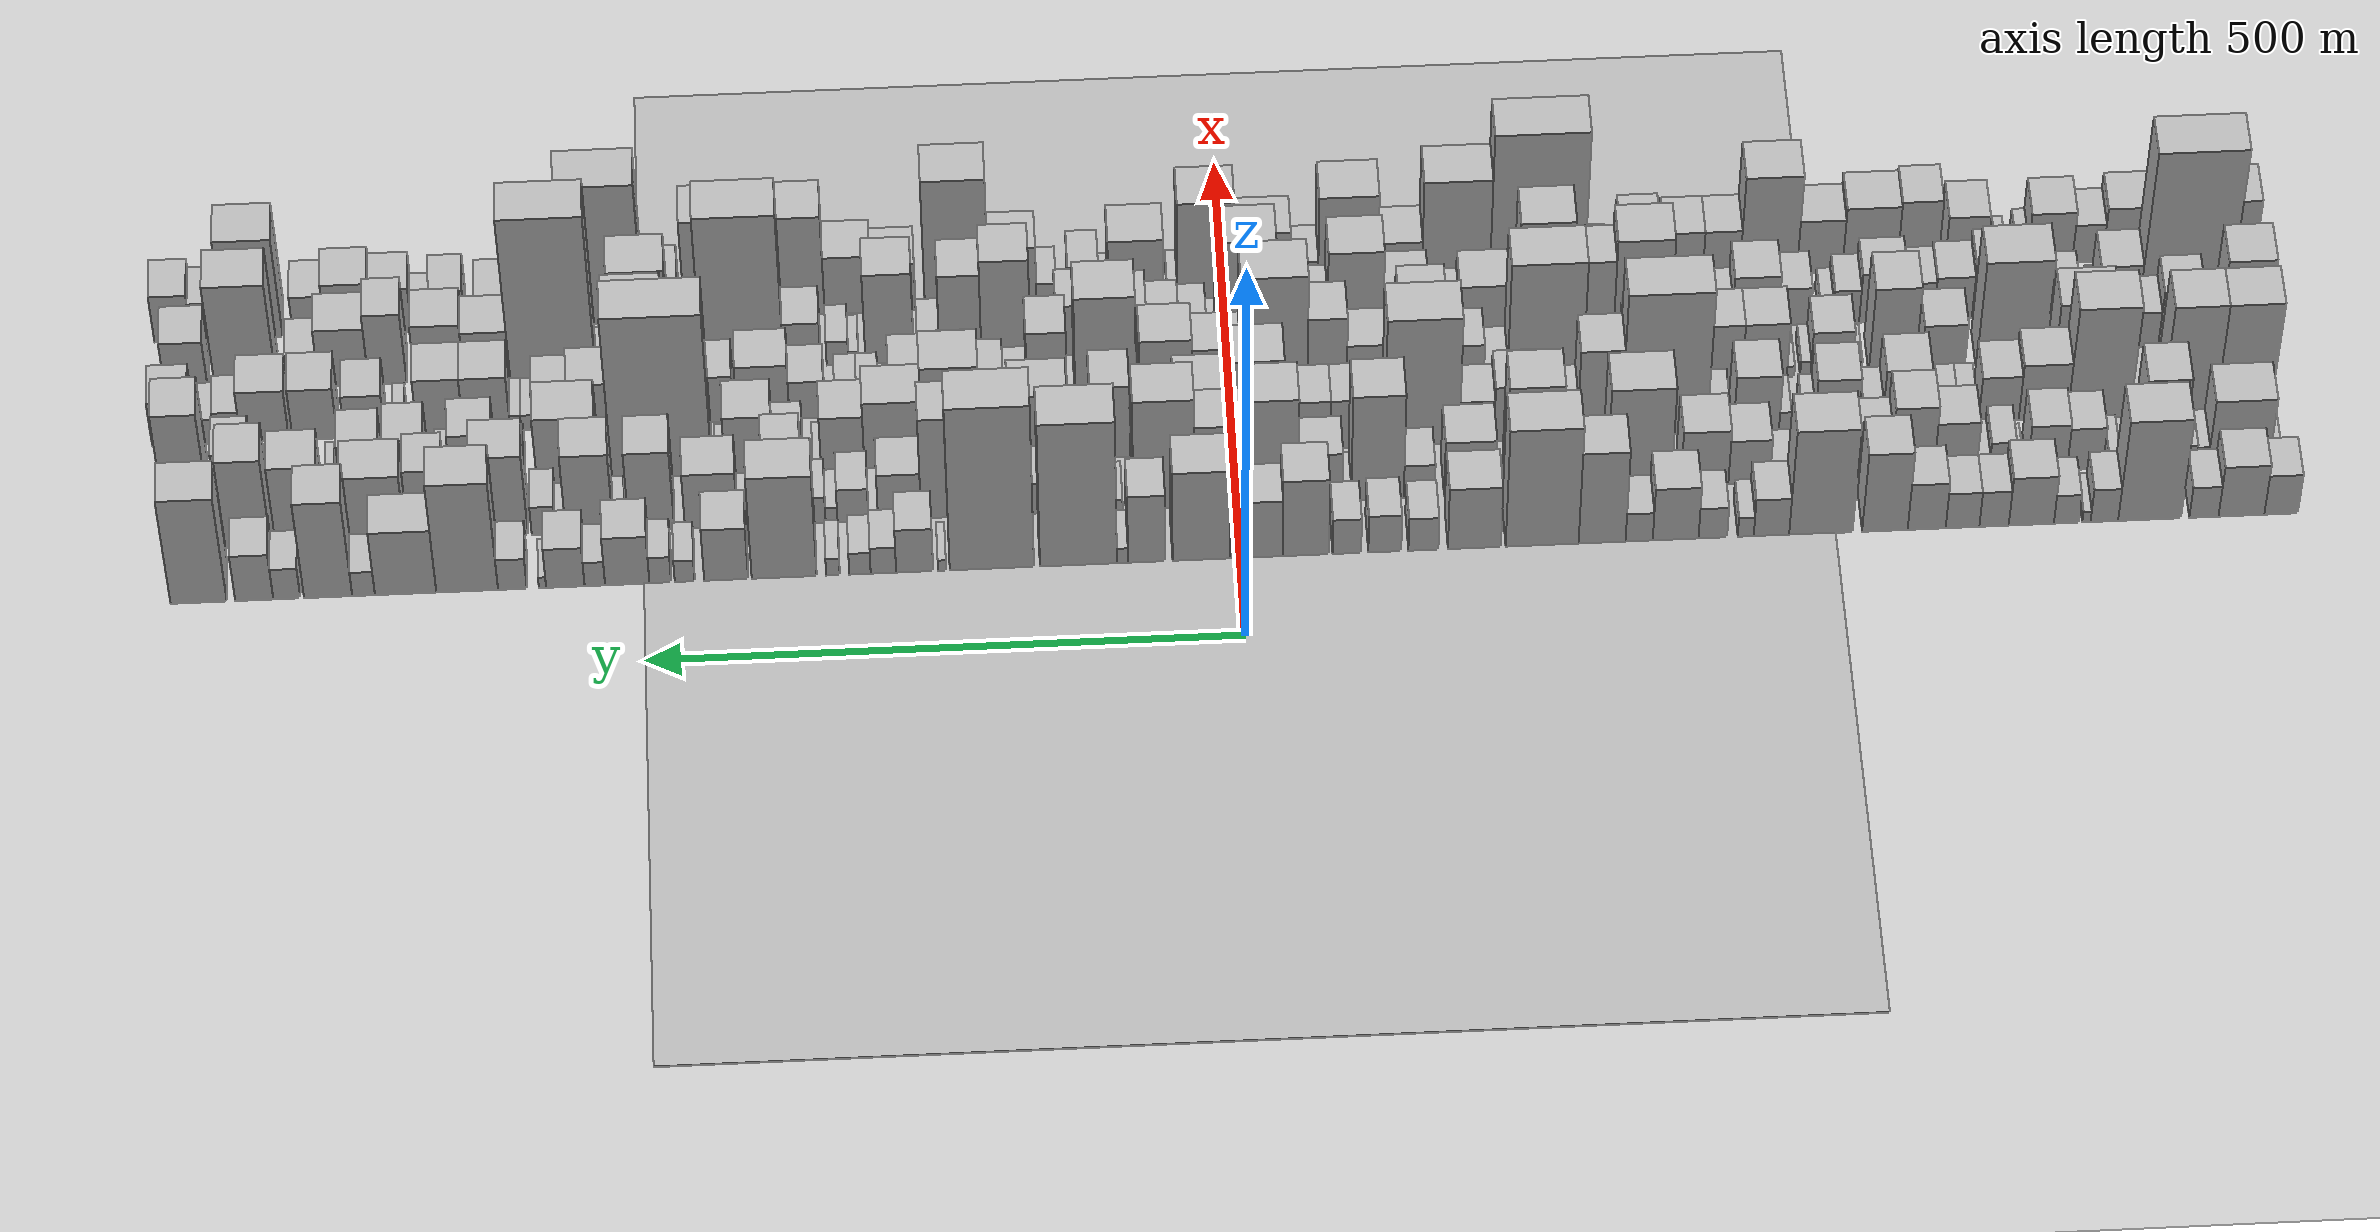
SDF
<?xml version="1.0" encoding="utf-8"?>

<sdf version="1.6">

   <world name="default">

      <gui fullscreen="0">

         <camera name="user_camera">

            <pose>-15 0 4.57585 0 0 0</pose>

            <view_controller>orbit</view_controller>

         </camera>

      </gui>

      <scene>

         <sky>

           <clouds>

             <speed>12</speed>

           </clouds>

         </sky>

         <ambient>0.4 0.4 0.4 1</ambient>

         <background>0.7 0.7 0.7 1</background>

         <shadows>1</shadows>

      </scene>

      <gravity>0 0 -9.8066</gravity>

      <magnetic_field>6e-06 2.3e-05 -4.2e-05</magnetic_field>

      <physics default="0" name="default_physics" type="ode">

         <ode>

            <solver>

               <type>quick</type>

               <iters>10</iters>

               <sor>1.0</sor>

               <use_dynamic_moi_rescaling>0</use_dynamic_moi_rescaling>

            </solver>

            <constraints>

               <cfm>0</cfm>

               <erp>0.2</erp>

               <contact_max_correcting_vel>100</contact_max_correcting_vel>

               <contact_surface_layer>0.001</contact_surface_layer>

            </constraints>

         </ode>

         <max_step_size>0.004</max_step_size>

         <real_time_factor>1</real_time_factor>

         <real_time_update_rate>250</real_time_update_rate>

      </physics>

      <light name="sun" type="directional">

         <cast_shadows>1</cast_shadows>

         <pose>0 0 10 0 0 0</pose>

         <diffuse>0.8 0.8 0.8 1</diffuse>

         <specular>0.2 0.2 0.2 1</specular>

         <attenuation>

            <range>1000</range>

            <constant>0.9</constant>

            <linear>0.01</linear>

            <quadratic>0.001</quadratic>

         </attenuation>

         <direction>-0.5 0.1 -0.9</direction>

      </light>

      <include>

         <name>ground_plane_1</name>

         <uri>model://HANNAS_ground_plane</uri>

         <pose>0 0 0  0 0 0</pose>

      </include>

      <include>

         <name>ground_plane_2</name>

         <uri>model://HANNAS_ground_plane</uri>

         <pose>100 0 0  0 0 0</pose>

      </include>

      <model name="building_1">

         <static>1</static>

         <pose frame="">100.0000 -875.8655 0 0.000000 0.000000 0.000000</pose>

         <link name="link">

            <pose frame="">0 0 27.00 0 0 0</pose>

            <collision name="collision">

               <geometry>

                  <box>

                     <size>40.0000 28.2690 54.0000</size>

                  </box>

               </geometry>

               <max_contacts>10</max_contacts>

               <surface>

                  <contact>

                     <ode/>

                  </contact>

                  <bounce/>

                  <friction>

                     <torsional>

                        <ode/>

                     </torsional>

                     <ode/>

                  </friction>

               </surface>

            </collision>

            <visual name="visual">

               <cast_shadows>0</cast_shadows>

               <geometry>

                  <box>

                     <size>40.0000 28.2690 54.0000</size>

                  </box>

               </geometry>

               <material>

                  <script>

                     <uri>model://HANNAS_wall/materials/scripts</uri>

                     <uri>model://HANNAS_wall/materials/textures</uri>

                     <name>vrc/HANNAS_wall</name>

                  </script>

               </material>

            </visual>

            <self_collide>0</self_collide>

            <enable_wind>0</enable_wind>

            <kinematic>0</kinematic>

         </link>

      </model>

      <model name="building_2">

         <static>1</static>

         <pose frame="">100.0000 -842.3592 0 0.000000 0.000000 0.000000</pose>

         <link name="link">

            <pose frame="">0 0 34.50 0 0 0</pose>

            <collision name="collision">

               <geometry>

                  <box>

                     <size>40.0000 38.7436 69.0000</size>

                  </box>

               </geometry>

               <max_contacts>10</max_contacts>

               <surface>

                  <contact>

                     <ode/>

                  </contact>

                  <bounce/>

                  <friction>

                     <torsional>

                        <ode/>

                     </torsional>

                     <ode/>

                  </friction>

               </surface>

            </collision>

            <visual name="visual">

               <cast_shadows>0</cast_shadows>

               <geometry>

                  <box>

                     <size>40.0000 38.7436 69.0000</size>

                  </box>

               </geometry>

               <material>

                  <script>

                     <uri>model://HANNAS_wall/materials/scripts</uri>

                     <uri>model://HANNAS_wall/materials/textures</uri>

                     <name>vrc/HANNAS_wall</name>

                  </script>

               </material>

            </visual>

            <self_collide>0</self_collide>

            <enable_wind>0</enable_wind>

            <kinematic>0</kinematic>

         </link>

      </model>

      <model name="building_3">

         <static>1</static>

         <pose frame="">100.0000 -810.6774 0 0.000000 0.000000 0.000000</pose>

         <link name="link">

            <pose frame="">0 0 21.00 0 0 0</pose>

            <collision name="collision">

               <geometry>

                  <box>

                     <size>40.0000 24.6200 42.0000</size>

                  </box>

               </geometry>

               <max_contacts>10</max_contacts>

               <surface>

                  <contact>

                     <ode/>

                  </contact>

                  <bounce/>

                  <friction>

                     <torsional>

                        <ode/>

                     </torsional>

                     <ode/>

                  </friction>

               </surface>

            </collision>

            <visual name="visual">

               <cast_shadows>0</cast_shadows>

               <geometry>

                  <box>

                     <size>40.0000 24.6200 42.0000</size>

                  </box>

               </geometry>

               <material>

                  <script>

                     <uri>model://HANNAS_wall/materials/scripts</uri>

                     <uri>model://HANNAS_wall/materials/textures</uri>

                     <name>vrc/HANNAS_wall</name>

                  </script>

               </material>

            </visual>

            <self_collide>0</self_collide>

            <enable_wind>0</enable_wind>

            <kinematic>0</kinematic>

         </link>

      </model>

      <model name="building_4">

         <static>1</static>

         <pose frame="">100.0000 -764.7874 0 0.000000 0.000000 0.000000</pose>

         <link name="link">

            <pose frame="">0 0 69.00 0 0 0</pose>

            <collision name="collision">

               <geometry>

                  <box>

                     <size>40.0000 53.1601 138.0000</size>

                  </box>

               </geometry>

               <max_contacts>10</max_contacts>

               <surface>

                  <contact>

                     <ode/>

                  </contact>

                  <bounce/>

                  <friction>

                     <torsional>

                        <ode/>

                     </torsional>

                     <ode/>

                  </friction>

               </surface>

            </collision>

            <visual name="visual">

               <cast_shadows>0</cast_shadows>

               <geometry>

                  <box>

                     <size>40.0000 53.1601 138.0000</size>

                  </box>

               </geometry>

               <material>

                  <script>

                     <uri>model://HANNAS_wall/materials/scripts</uri>

                     <uri>model://HANNAS_wall/materials/textures</uri>

                     <name>vrc/HANNAS_wall</name>

                  </script>

               </material>

            </visual>

            <self_collide>0</self_collide>

            <enable_wind>0</enable_wind>

            <kinematic>0</kinematic>

         </link>

      </model>

      <model name="building_5">

         <static>1</static>

         <pose frame="">100.0000 -726.5700 0 0.000000 0.000000 0.000000</pose>

         <link name="link">

            <pose frame="">0 0 22.50 0 0 0</pose>

            <collision name="collision">

               <geometry>

                  <box>

                     <size>40.0000 23.2748 45.0000</size>

                  </box>

               </geometry>

               <max_contacts>10</max_contacts>

               <surface>

                  <contact>

                     <ode/>

                  </contact>

                  <bounce/>

                  <friction>

                     <torsional>

                        <ode/>

                     </torsional>

                     <ode/>

                  </friction>

               </surface>

            </collision>

            <visual name="visual">

               <cast_shadows>0</cast_shadows>

               <geometry>

                  <box>

                     <size>40.0000 23.2748 45.0000</size>

                  </box>

               </geometry>

               <material>

                  <script>

                     <uri>model://HANNAS_wall/materials/scripts</uri>

                     <uri>model://HANNAS_wall/materials/textures</uri>

                     <name>vrc/HANNAS_wall</name>

                  </script>

               </material>

            </visual>

            <self_collide>0</self_collide>

            <enable_wind>0</enable_wind>

            <kinematic>0</kinematic>

         </link>

      </model>

      <model name="building_6">

         <static>1</static>

         <pose frame="">100.0000 -711.4484 0 0.000000 0.000000 0.000000</pose>

         <link name="link">

            <pose frame="">0 0 7.50 0 0 0</pose>

            <collision name="collision">

               <geometry>

                  <box>

                     <size>40.0000 6.9683 15.0000</size>

                  </box>

               </geometry>

               <max_contacts>10</max_contacts>

               <surface>

                  <contact>

                     <ode/>

                  </contact>

                  <bounce/>

                  <friction>

                     <torsional>

                        <ode/>

                     </torsional>

                     <ode/>

                  </friction>

               </surface>

            </collision>

            <visual name="visual">

               <cast_shadows>0</cast_shadows>

               <geometry>

                  <box>

                     <size>40.0000 6.9683 15.0000</size>

                  </box>

               </geometry>

               <material>

                  <script>

                     <uri>model://HANNAS_wall/materials/scripts</uri>

                     <uri>model://HANNAS_wall/materials/textures</uri>

                     <name>vrc/HANNAS_wall</name>

                  </script>

               </material>

            </visual>

            <self_collide>0</self_collide>

            <enable_wind>0</enable_wind>

            <kinematic>0</kinematic>

         </link>

      </model>

      <model name="building_7">

         <static>1</static>

         <pose frame="">100.0000 -694.4781 0 0.000000 0.000000 0.000000</pose>

         <link name="link">

            <pose frame="">0 0 19.50 0 0 0</pose>

            <collision name="collision">

               <geometry>

                  <box>

                     <size>40.0000 20.9722 39.0000</size>

                  </box>

               </geometry>

               <max_contacts>10</max_contacts>

               <surface>

                  <contact>

                     <ode/>

                  </contact>

                  <bounce/>

                  <friction>

                     <torsional>

                        <ode/>

                     </torsional>

                     <ode/>

                  </friction>

               </surface>

            </collision>

            <visual name="visual">

               <cast_shadows>0</cast_shadows>

               <geometry>

                  <box>

                     <size>40.0000 20.9722 39.0000</size>

                  </box>

               </geometry>

               <material>

                  <script>

                     <uri>model://HANNAS_wall/materials/scripts</uri>

                     <uri>model://HANNAS_wall/materials/textures</uri>

                     <name>vrc/HANNAS_wall</name>

                  </script>

               </material>

            </visual>

            <self_collide>0</self_collide>

            <enable_wind>0</enable_wind>

            <kinematic>0</kinematic>

         </link>

      </model>

      <model name="building_8">

         <static>1</static>

         <pose frame="">100.0000 -664.9663 0 0.000000 0.000000 0.000000</pose>

         <link name="link">

            <pose frame="">0 0 33.00 0 0 0</pose>

            <collision name="collision">

               <geometry>

                  <box>

                     <size>40.0000 38.0515 66.0000</size>

                  </box>

               </geometry>

               <max_contacts>10</max_contacts>

               <surface>

                  <contact>

                     <ode/>

                  </contact>

                  <bounce/>

                  <friction>

                     <torsional>

                        <ode/>

                     </torsional>

                     <ode/>

                  </friction>

               </surface>

            </collision>

            <visual name="visual">

               <cast_shadows>0</cast_shadows>

               <geometry>

                  <box>

                     <size>40.0000 38.0515 66.0000</size>

                  </box>

               </geometry>

               <material>

                  <script>

                     <uri>model://HANNAS_wall/materials/scripts</uri>

                     <uri>model://HANNAS_wall/materials/textures</uri>

                     <name>vrc/HANNAS_wall</name>

                  </script>

               </material>

            </visual>

            <self_collide>0</self_collide>

            <enable_wind>0</enable_wind>

            <kinematic>0</kinematic>

         </link>

      </model>

      <model name="building_9">

         <static>1</static>

         <pose frame="">100.0000 -633.5444 0 0.000000 0.000000 0.000000</pose>

         <link name="link">

            <pose frame="">0 0 24.00 0 0 0</pose>

            <collision name="collision">

               <geometry>

                  <box>

                     <size>40.0000 24.7922 48.0000</size>

                  </box>

               </geometry>

               <max_contacts>10</max_contacts>

               <surface>

                  <contact>

                     <ode/>

                  </contact>

                  <bounce/>

                  <friction>

                     <torsional>

                        <ode/>

                     </torsional>

                     <ode/>

                  </friction>

               </surface>

            </collision>

            <visual name="visual">

               <cast_shadows>0</cast_shadows>

               <geometry>

                  <box>

                     <size>40.0000 24.7922 48.0000</size>

                  </box>

               </geometry>

               <material>

                  <script>

                     <uri>model://HANNAS_wall/materials/scripts</uri>

                     <uri>model://HANNAS_wall/materials/textures</uri>

                     <name>vrc/HANNAS_wall</name>

                  </script>

               </material>

            </visual>

            <self_collide>0</self_collide>

            <enable_wind>0</enable_wind>

            <kinematic>0</kinematic>

         </link>

      </model>

      <model name="building_10">

         <static>1</static>

         <pose frame="">100.0000 -606.9436 0 0.000000 0.000000 0.000000</pose>

         <link name="link">

            <pose frame="">0 0 24.00 0 0 0</pose>

            <collision name="collision">

               <geometry>

                  <box>

                     <size>40.0000 28.4095 48.0000</size>

                  </box>

               </geometry>

               <max_contacts>10</max_contacts>

               <surface>

                  <contact>

                     <ode/>

                  </contact>

                  <bounce/>

                  <friction>

                     <torsional>

                        <ode/>

                     </torsional>

                     <ode/>

                  </friction>

               </surface>

            </collision>

            <visual name="visual">

               <cast_shadows>0</cast_shadows>

               <geometry>

                  <box>

                     <size>40.0000 28.4095 48.0000</size>

                  </box>

               </geometry>

               <material>

                  <script>

                     <uri>model://HANNAS_wall/materials/scripts</uri>

                     <uri>model://HANNAS_wall/materials/textures</uri>

                     <name>vrc/HANNAS_wall</name>

                  </script>

               </material>

            </visual>

            <self_collide>0</self_collide>

            <enable_wind>0</enable_wind>

            <kinematic>0</kinematic>

         </link>

      </model>

      <model name="building_11">

         <static>1</static>

         <pose frame="">100.0000 -576.7220 0 0.000000 0.000000 0.000000</pose>

         <link name="link">

            <pose frame="">0 0 31.50 0 0 0</pose>

            <collision name="collision">

               <geometry>

                  <box>

                     <size>40.0000 32.0336 63.0000</size>

                  </box>

               </geometry>

               <max_contacts>10</max_contacts>

               <surface>

                  <contact>

                     <ode/>

                  </contact>

                  <bounce/>

                  <friction>

                     <torsional>

                        <ode/>

                     </torsional>

                     <ode/>

                  </friction>

               </surface>

            </collision>

            <visual name="visual">

               <cast_shadows>0</cast_shadows>

               <geometry>

                  <box>

                     <size>40.0000 32.0336 63.0000</size>

                  </box>

               </geometry>

               <material>

                  <script>

                     <uri>model://HANNAS_wall/materials/scripts</uri>

                     <uri>model://HANNAS_wall/materials/textures</uri>

                     <name>vrc/HANNAS_wall</name>

                  </script>

               </material>

            </visual>

            <self_collide>0</self_collide>

            <enable_wind>0</enable_wind>

            <kinematic>0</kinematic>

         </link>

      </model>

      <model name="building_12">

         <static>1</static>

         <pose frame="">100.0000 -541.5066 0 0.000000 0.000000 0.000000</pose>

         <link name="link">

            <pose frame="">0 0 54.00 0 0 0</pose>

            <collision name="collision">

               <geometry>

                  <box>

                     <size>40.0000 38.3972 108.0000</size>

                  </box>

               </geometry>

               <max_contacts>10</max_contacts>

               <surface>

                  <contact>

                     <ode/>

                  </contact>

                  <bounce/>

                  <friction>

                     <torsional>

                        <ode/>

                     </torsional>

                     <ode/>

                  </friction>

               </surface>

            </collision>

            <visual name="visual">

               <cast_shadows>0</cast_shadows>

               <geometry>

                  <box>

                     <size>40.0000 38.3972 108.0000</size>

                  </box>

               </geometry>

               <material>

                  <script>

                     <uri>model://HANNAS_wall/materials/scripts</uri>

                     <uri>model://HANNAS_wall/materials/textures</uri>

                     <name>vrc/HANNAS_wall</name>

                  </script>

               </material>

            </visual>

            <self_collide>0</self_collide>

            <enable_wind>0</enable_wind>

            <kinematic>0</kinematic>

         </link>

      </model>

      <model name="building_13">

         <static>1</static>

         <pose frame="">100.0000 -487.5618 0 0.000000 0.000000 0.000000</pose>

         <link name="link">

            <pose frame="">0 0 72.00 0 0 0</pose>

            <collision name="collision">

               <geometry>

                  <box>

                     <size>40.0000 53.4926 144.0000</size>

                  </box>

               </geometry>

               <max_contacts>10</max_contacts>

               <surface>

                  <contact>

                     <ode/>

                  </contact>

                  <bounce/>

                  <friction>

                     <torsional>

                        <ode/>

                     </torsional>

                     <ode/>

                  </friction>

               </surface>

            </collision>

            <visual name="visual">

               <cast_shadows>0</cast_shadows>

               <geometry>

                  <box>

                     <size>40.0000 53.4926 144.0000</size>

                  </box>

               </geometry>

               <material>

                  <script>

                     <uri>model://HANNAS_wall/materials/scripts</uri>

                     <uri>model://HANNAS_wall/materials/textures</uri>

                     <name>vrc/HANNAS_wall</name>

                  </script>

               </material>

            </visual>

            <self_collide>0</self_collide>

            <enable_wind>0</enable_wind>

            <kinematic>0</kinematic>

         </link>

      </model>

      <model name="building_14">

         <static>1</static>

         <pose frame="">100.0000 -445.9098 0 0.000000 0.000000 0.000000</pose>

         <link name="link">

            <pose frame="">0 0 25.50 0 0 0</pose>

            <collision name="collision">

               <geometry>

                  <box>

                     <size>40.0000 29.8113 51.0000</size>

                  </box>

               </geometry>

               <max_contacts>10</max_contacts>

               <surface>

                  <contact>

                     <ode/>

                  </contact>

                  <bounce/>

                  <friction>

                     <torsional>

                        <ode/>

                     </torsional>

                     <ode/>

                  </friction>

               </surface>

            </collision>

            <visual name="visual">

               <cast_shadows>0</cast_shadows>

               <geometry>

                  <box>

                     <size>40.0000 29.8113 51.0000</size>

                  </box>

               </geometry>

               <material>

                  <script>

                     <uri>model://HANNAS_wall/materials/scripts</uri>

                     <uri>model://HANNAS_wall/materials/textures</uri>

                     <name>vrc/HANNAS_wall</name>

                  </script>

               </material>

            </visual>

            <self_collide>0</self_collide>

            <enable_wind>0</enable_wind>

            <kinematic>0</kinematic>

         </link>

      </model>

      <model name="building_15">

         <static>1</static>

         <pose frame="">100.0000 -424.2704 0 0.000000 0.000000 0.000000</pose>

         <link name="link">

            <pose frame="">0 0 13.50 0 0 0</pose>

            <collision name="collision">

               <geometry>

                  <box>

                     <size>40.0000 13.4676 27.0000</size>

                  </box>

               </geometry>

               <max_contacts>10</max_contacts>

               <surface>

                  <contact>

                     <ode/>

                  </contact>

                  <bounce/>

                  <friction>

                     <torsional>

                        <ode/>

                     </torsional>

                     <ode/>

                  </friction>

               </surface>

            </collision>

            <visual name="visual">

               <cast_shadows>0</cast_shadows>

               <geometry>

                  <box>

                     <size>40.0000 13.4676 27.0000</size>

                  </box>

               </geometry>

               <material>

                  <script>

                     <uri>model://HANNAS_wall/materials/scripts</uri>

                     <uri>model://HANNAS_wall/materials/textures</uri>

                     <name>vrc/HANNAS_wall</name>

                  </script>

               </material>

            </visual>

            <self_collide>0</self_collide>

            <enable_wind>0</enable_wind>

            <kinematic>0</kinematic>

         </link>

      </model>

      <model name="building_16">

         <static>1</static>

         <pose frame="">100.0000 -396.5163 0 0.000000 0.000000 0.000000</pose>

         <link name="link">

            <pose frame="">0 0 21.00 0 0 0</pose>

            <collision name="collision">

               <geometry>

                  <box>

                     <size>40.0000 24.0407 42.0000</size>

                  </box>

               </geometry>

               <max_contacts>10</max_contacts>

               <surface>

                  <contact>

                     <ode/>

                  </contact>

                  <bounce/>

                  <friction>

                     <torsional>

                        <ode/>

                     </torsional>

                     <ode/>

                  </friction>

               </surface>

            </collision>

            <visual name="visual">

               <cast_shadows>0</cast_shadows>

               <geometry>

                  <box>

                     <size>40.0000 24.0407 42.0000</size>

                  </box>

               </geometry>

               <material>

                  <script>

                     <uri>model://HANNAS_wall/materials/scripts</uri>

                     <uri>model://HANNAS_wall/materials/textures</uri>

                     <name>vrc/HANNAS_wall</name>

                  </script>

               </material>

            </visual>

            <self_collide>0</self_collide>

            <enable_wind>0</enable_wind>

            <kinematic>0</kinematic>

         </link>

      </model>

      <model name="building_17">

         <static>1</static>

         <pose frame="">100.0000 -365.2377 0 0.000000 0.000000 0.000000</pose>

         <link name="link">

            <pose frame="">0 0 36.00 0 0 0</pose>

            <collision name="collision">

               <geometry>

                  <box>

                     <size>40.0000 38.5166 72.0000</size>

                  </box>

               </geometry>

               <max_contacts>10</max_contacts>

               <surface>

                  <contact>

                     <ode/>

                  </contact>

                  <bounce/>

                  <friction>

                     <torsional>

                        <ode/>

                     </torsional>

                     <ode/>

                  </friction>

               </surface>

            </collision>

            <visual name="visual">

               <cast_shadows>0</cast_shadows>

               <geometry>

                  <box>

                     <size>40.0000 38.5166 72.0000</size>

                  </box>

               </geometry>

               <material>

                  <script>

                     <uri>model://HANNAS_wall/materials/scripts</uri>

                     <uri>model://HANNAS_wall/materials/textures</uri>

                     <name>vrc/HANNAS_wall</name>

                  </script>

               </material>

            </visual>

            <self_collide>0</self_collide>

            <enable_wind>0</enable_wind>

            <kinematic>0</kinematic>

         </link>

      </model>

      <model name="building_18">

         <static>1</static>

         <pose frame="">100.0000 -334.5423 0 0.000000 0.000000 0.000000</pose>

         <link name="link">

            <pose frame="">0 0 19.50 0 0 0</pose>

            <collision name="collision">

               <geometry>

                  <box>

                     <size>40.0000 22.8741 39.0000</size>

                  </box>

               </geometry>

               <max_contacts>10</max_contacts>

               <surface>

                  <contact>

                     <ode/>

                  </contact>

                  <bounce/>

                  <friction>

                     <torsional>

                        <ode/>

                     </torsional>

                     <ode/>

                  </friction>

               </surface>

            </collision>

            <visual name="visual">

               <cast_shadows>0</cast_shadows>

               <geometry>

                  <box>

                     <size>40.0000 22.8741 39.0000</size>

                  </box>

               </geometry>

               <material>

                  <script>

                     <uri>model://HANNAS_wall/materials/scripts</uri>

                     <uri>model://HANNAS_wall/materials/textures</uri>

                     <name>vrc/HANNAS_wall</name>

                  </script>

               </material>

            </visual>

            <self_collide>0</self_collide>

            <enable_wind>0</enable_wind>

            <kinematic>0</kinematic>

         </link>

      </model>

      <model name="building_19">

         <static>1</static>

         <pose frame="">100.0000 -303.3574 0 0.000000 0.000000 0.000000</pose>

         <link name="link">

            <pose frame="">0 0 63.00 0 0 0</pose>

            <collision name="collision">

               <geometry>

                  <box>

                     <size>40.0000 39.4959 126.0000</size>

                  </box>

               </geometry>

               <max_contacts>10</max_contacts>

               <surface>

                  <contact>

                     <ode/>

                  </contact>

                  <bounce/>

                  <friction>

                     <torsional>

                        <ode/>

                     </torsional>

                     <ode/>

                  </friction>

               </surface>

            </collision>

            <visual name="visual">

               <cast_shadows>0</cast_shadows>

               <geometry>

                  <box>

                     <size>40.0000 39.4959 126.0000</size>

                  </box>

               </geometry>

               <material>

                  <script>

                     <uri>model://HANNAS_wall/materials/scripts</uri>

                     <uri>model://HANNAS_wall/materials/textures</uri>

                     <name>vrc/HANNAS_wall</name>

                  </script>

               </material>

            </visual>

            <self_collide>0</self_collide>

            <enable_wind>0</enable_wind>

            <kinematic>0</kinematic>

         </link>

      </model>

      <model name="building_20">

         <static>1</static>

         <pose frame="">100.0000 -252.9462 0 0.000000 0.000000 0.000000</pose>

         <link name="link">

            <pose frame="">0 0 81.00 0 0 0</pose>

            <collision name="collision">

               <geometry>

                  <box>

                     <size>40.0000 61.3265 162.0000</size>

                  </box>

               </geometry>

               <max_contacts>10</max_contacts>

               <surface>

                  <contact>

                     <ode/>

                  </contact>

                  <bounce/>

                  <friction>

                     <torsional>

                        <ode/>

                     </torsional>

                     <ode/>

                  </friction>

               </surface>

            </collision>

            <visual name="visual">

               <cast_shadows>0</cast_shadows>

               <geometry>

                  <box>

                     <size>40.0000 61.3265 162.0000</size>

                  </box>

               </geometry>

               <material>

                  <script>

                     <uri>model://HANNAS_wall/materials/scripts</uri>

                     <uri>model://HANNAS_wall/materials/textures</uri>

                     <name>vrc/HANNAS_wall</name>

                  </script>

               </material>

            </visual>

            <self_collide>0</self_collide>

            <enable_wind>0</enable_wind>

            <kinematic>0</kinematic>

         </link>

      </model>

      <model name="building_21">

         <static>1</static>

         <pose frame="">100.0000 -196.0026 0 0.000000 0.000000 0.000000</pose>

         <link name="link">

            <pose frame="">0 0 42.00 0 0 0</pose>

            <collision name="collision">

               <geometry>

                  <box>

                     <size>40.0000 44.5608 84.0000</size>

                  </box>

               </geometry>

               <max_contacts>10</max_contacts>

               <surface>

                  <contact>

                     <ode/>

                  </contact>

                  <bounce/>

                  <friction>

                     <torsional>

                        <ode/>

                     </torsional>

                     <ode/>

                  </friction>

               </surface>

            </collision>

            <visual name="visual">

               <cast_shadows>0</cast_shadows>

               <geometry>

                  <box>

                     <size>40.0000 44.5608 84.0000</size>

                  </box>

               </geometry>

               <material>

                  <script>

                     <uri>model://HANNAS_wall/materials/scripts</uri>

                     <uri>model://HANNAS_wall/materials/textures</uri>

                     <name>vrc/HANNAS_wall</name>

                  </script>

               </material>

            </visual>

            <self_collide>0</self_collide>

            <enable_wind>0</enable_wind>

            <kinematic>0</kinematic>

         </link>

      </model>

      <model name="building_22">

         <static>1</static>

         <pose frame="">100.0000 -153.1207 0 0.000000 0.000000 0.000000</pose>

         <link name="link">

            <pose frame="">0 0 22.50 0 0 0</pose>

            <collision name="collision">

               <geometry>

                  <box>

                     <size>40.0000 25.2032 45.0000</size>

                  </box>

               </geometry>

               <max_contacts>10</max_contacts>

               <surface>

                  <contact>

                     <ode/>

                  </contact>

                  <bounce/>

                  <friction>

                     <torsional>

                        <ode/>

                     </torsional>

                     <ode/>

                  </friction>

               </surface>

            </collision>

            <visual name="visual">

               <cast_shadows>0</cast_shadows>

               <geometry>

                  <box>

                     <size>40.0000 25.2032 45.0000</size>

                  </box>

               </geometry>

               <material>

                  <script>

                     <uri>model://HANNAS_wall/materials/scripts</uri>

                     <uri>model://HANNAS_wall/materials/textures</uri>

                     <name>vrc/HANNAS_wall</name>

                  </script>

               </material>

            </visual>

            <self_collide>0</self_collide>

            <enable_wind>0</enable_wind>

            <kinematic>0</kinematic>

         </link>

      </model>

      <model name="building_23">

         <static>1</static>

         <pose frame="">100.0000 -120.6964 0 0.000000 0.000000 0.000000</pose>

         <link name="link">

            <pose frame="">0 0 25.50 0 0 0</pose>

            <collision name="collision">

               <geometry>

                  <box>

                     <size>40.0000 27.6454 51.0000</size>

                  </box>

               </geometry>

               <max_contacts>10</max_contacts>

               <surface>

                  <contact>

                     <ode/>

                  </contact>

                  <bounce/>

                  <friction>

                     <torsional>

                        <ode/>

                     </torsional>

                     <ode/>

                  </friction>

               </surface>

            </collision>

            <visual name="visual">

               <cast_shadows>0</cast_shadows>

               <geometry>

                  <box>

                     <size>40.0000 27.6454 51.0000</size>

                  </box>

               </geometry>

               <material>

                  <script>

                     <uri>model://HANNAS_wall/materials/scripts</uri>

                     <uri>model://HANNAS_wall/materials/textures</uri>

                     <name>vrc/HANNAS_wall</name>

                  </script>

               </material>

            </visual>

            <self_collide>0</self_collide>

            <enable_wind>0</enable_wind>

            <kinematic>0</kinematic>

         </link>

      </model>

      <model name="building_24">

         <static>1</static>

         <pose frame="">100.0000 -88.8576 0 0.000000 0.000000 0.000000</pose>

         <link name="link">

            <pose frame="">0 0 24.00 0 0 0</pose>

            <collision name="collision">

               <geometry>

                  <box>

                     <size>40.0000 24.0322 48.0000</size>

                  </box>

               </geometry>

               <max_contacts>10</max_contacts>

               <surface>

                  <contact>

                     <ode/>

                  </contact>

                  <bounce/>

                  <friction>

                     <torsional>

                        <ode/>

                     </torsional>

                     <ode/>

                  </friction>

               </surface>

            </collision>

            <visual name="visual">

               <cast_shadows>0</cast_shadows>

               <geometry>

                  <box>

                     <size>40.0000 24.0322 48.0000</size>

                  </box>

               </geometry>

               <material>

                  <script>

                     <uri>model://HANNAS_wall/materials/scripts</uri>

                     <uri>model://HANNAS_wall/materials/textures</uri>

                     <name>vrc/HANNAS_wall</name>

                  </script>

               </material>

            </visual>

            <self_collide>0</self_collide>

            <enable_wind>0</enable_wind>

            <kinematic>0</kinematic>

         </link>

      </model>

      <model name="building_25">

         <static>1</static>

         <pose frame="">100.0000 -54.4047 0 0.000000 0.000000 0.000000</pose>

         <link name="link">

            <pose frame="">0 0 52.50 0 0 0</pose>

            <collision name="collision">

               <geometry>

                  <box>

                     <size>40.0000 38.8737 105.0000</size>

                  </box>

               </geometry>

               <max_contacts>10</max_contacts>

               <surface>

                  <contact>

                     <ode/>

                  </contact>

                  <bounce/>

                  <friction>

                     <torsional>

                        <ode/>

                     </torsional>

                     <ode/>

                  </friction>

               </surface>

            </collision>

            <visual name="visual">

               <cast_shadows>0</cast_shadows>

               <geometry>

                  <box>

                     <size>40.0000 38.8737 105.0000</size>

                  </box>

               </geometry>

               <material>

                  <script>

                     <uri>model://HANNAS_wall/materials/scripts</uri>

                     <uri>model://HANNAS_wall/materials/textures</uri>

                     <name>vrc/HANNAS_wall</name>

                  </script>

               </material>

            </visual>

            <self_collide>0</self_collide>

            <enable_wind>0</enable_wind>

            <kinematic>0</kinematic>

         </link>

      </model>

      <model name="building_26">

         <static>1</static>

         <pose frame="">100.0000 -12.9961 0 0.000000 0.000000 0.000000</pose>

         <link name="link">

            <pose frame="">0 0 39.00 0 0 0</pose>

            <collision name="collision">

               <geometry>

                  <box>

                     <size>40.0000 43.9434 78.0000</size>

                  </box>

               </geometry>

               <max_contacts>10</max_contacts>

               <surface>

                  <contact>

                     <ode/>

                  </contact>

                  <bounce/>

                  <friction>

                     <torsional>

                        <ode/>

                     </torsional>

                     <ode/>

                  </friction>

               </surface>

            </collision>

            <visual name="visual">

               <cast_shadows>0</cast_shadows>

               <geometry>

                  <box>

                     <size>40.0000 43.9434 78.0000</size>

                  </box>

               </geometry>

               <material>

                  <script>

                     <uri>model://HANNAS_wall/materials/scripts</uri>

                     <uri>model://HANNAS_wall/materials/textures</uri>

                     <name>vrc/HANNAS_wall</name>

                  </script>

               </material>

            </visual>

            <self_collide>0</self_collide>

            <enable_wind>0</enable_wind>

            <kinematic>0</kinematic>

         </link>

      </model>

      <model name="building_27">

         <static>1</static>

         <pose frame="">100.0000 33.1813 0 0.000000 0.000000 0.000000</pose>

         <link name="link">

            <pose frame="">0 0 61.50 0 0 0</pose>

            <collision name="collision">

               <geometry>

                  <box>

                     <size>40.0000 48.4115 123.0000</size>

                  </box>

               </geometry>

               <max_contacts>10</max_contacts>

               <surface>

                  <contact>

                     <ode/>

                  </contact>

                  <bounce/>

                  <friction>

                     <torsional>

                        <ode/>

                     </torsional>

                     <ode/>

                  </friction>

               </surface>

            </collision>

            <visual name="visual">

               <cast_shadows>0</cast_shadows>

               <geometry>

                  <box>

                     <size>40.0000 48.4115 123.0000</size>

                  </box>

               </geometry>

               <material>

                  <script>

                     <uri>model://HANNAS_wall/materials/scripts</uri>

                     <uri>model://HANNAS_wall/materials/textures</uri>

                     <name>vrc/HANNAS_wall</name>

                  </script>

               </material>

            </visual>

            <self_collide>0</self_collide>

            <enable_wind>0</enable_wind>

            <kinematic>0</kinematic>

         </link>

      </model>

      <model name="building_28">

         <static>1</static>

         <pose frame="">100.0000 79.0986 0 0.000000 0.000000 0.000000</pose>

         <link name="link">

            <pose frame="">0 0 46.50 0 0 0</pose>

            <collision name="collision">

               <geometry>

                  <box>

                     <size>40.0000 31.4229 93.0000</size>

                  </box>

               </geometry>

               <max_contacts>10</max_contacts>

               <surface>

                  <contact>

                     <ode/>

                  </contact>

                  <bounce/>

                  <friction>

                     <torsional>

                        <ode/>

                     </torsional>

                     <ode/>

                  </friction>

               </surface>

            </collision>

            <visual name="visual">

               <cast_shadows>0</cast_shadows>

               <geometry>

                  <box>

                     <size>40.0000 31.4229 93.0000</size>

                  </box>

               </geometry>

               <material>

                  <script>

                     <uri>model://HANNAS_wall/materials/scripts</uri>

                     <uri>model://HANNAS_wall/materials/textures</uri>

                     <name>vrc/HANNAS_wall</name>

                  </script>

               </material>

            </visual>

            <self_collide>0</self_collide>

            <enable_wind>0</enable_wind>

            <kinematic>0</kinematic>

         </link>

      </model>

      <model name="building_29">

         <static>1</static>

         <pose frame="">100.0000 99.4468 0 0.000000 0.000000 0.000000</pose>

         <link name="link">

            <pose frame="">0 0 10.50 0 0 0</pose>

            <collision name="collision">

               <geometry>

                  <box>

                     <size>40.0000 9.2736 21.0000</size>

                  </box>

               </geometry>

               <max_contacts>10</max_contacts>

               <surface>

                  <contact>

                     <ode/>

                  </contact>

                  <bounce/>

                  <friction>

                     <torsional>

                        <ode/>

                     </torsional>

                     <ode/>

                  </friction>

               </surface>

            </collision>

            <visual name="visual">

               <cast_shadows>0</cast_shadows>

               <geometry>

                  <box>

                     <size>40.0000 9.2736 21.0000</size>

                  </box>

               </geometry>

               <material>

                  <script>

                     <uri>model://HANNAS_wall/materials/scripts</uri>

                     <uri>model://HANNAS_wall/materials/textures</uri>

                     <name>vrc/HANNAS_wall</name>

                  </script>

               </material>

            </visual>

            <self_collide>0</self_collide>

            <enable_wind>0</enable_wind>

            <kinematic>0</kinematic>

         </link>

      </model>

      <model name="building_30">

         <static>1</static>

         <pose frame="">100.0000 136.3446 0 0.000000 0.000000 0.000000</pose>

         <link name="link">

            <pose frame="">0 0 99.00 0 0 0</pose>

            <collision name="collision">

               <geometry>

                  <box>

                     <size>40.0000 64.5218 198.0000</size>

                  </box>

               </geometry>

               <max_contacts>10</max_contacts>

               <surface>

                  <contact>

                     <ode/>

                  </contact>

                  <bounce/>

                  <friction>

                     <torsional>

                        <ode/>

                     </torsional>

                     <ode/>

                  </friction>

               </surface>

            </collision>

            <visual name="visual">

               <cast_shadows>0</cast_shadows>

               <geometry>

                  <box>

                     <size>40.0000 64.5218 198.0000</size>

                  </box>

               </geometry>

               <material>

                  <script>

                     <uri>model://HANNAS_wall/materials/scripts</uri>

                     <uri>model://HANNAS_wall/materials/textures</uri>

                     <name>vrc/HANNAS_wall</name>

                  </script>

               </material>

            </visual>

            <self_collide>0</self_collide>

            <enable_wind>0</enable_wind>

            <kinematic>0</kinematic>

         </link>

      </model>

      <model name="building_31">

         <static>1</static>

         <pose frame="">100.0000 208.8867 0 0.000000 0.000000 0.000000</pose>

         <link name="link">

            <pose frame="">0 0 112.50 0 0 0</pose>

            <collision name="collision">

               <geometry>

                  <box>

                     <size>40.0000 70.5624 225.0000</size>

                  </box>

               </geometry>

               <max_contacts>10</max_contacts>

               <surface>

                  <contact>

                     <ode/>

                  </contact>

                  <bounce/>

                  <friction>

                     <torsional>

                        <ode/>

                     </torsional>

                     <ode/>

                  </friction>

               </surface>

            </collision>

            <visual name="visual">

               <cast_shadows>0</cast_shadows>

               <geometry>

                  <box>

                     <size>40.0000 70.5624 225.0000</size>

                  </box>

               </geometry>

               <material>

                  <script>

                     <uri>model://HANNAS_wall/materials/scripts</uri>

                     <uri>model://HANNAS_wall/materials/textures</uri>

                     <name>vrc/HANNAS_wall</name>

                  </script>

               </material>

            </visual>

            <self_collide>0</self_collide>

            <enable_wind>0</enable_wind>

            <kinematic>0</kinematic>

         </link>

      </model>

      <model name="building_32">

         <static>1</static>

         <pose frame="">100.0000 250.5901 0 0.000000 0.000000 0.000000</pose>

         <link name="link">

            <pose frame="">0 0 7.50 0 0 0</pose>

            <collision name="collision">

               <geometry>

                  <box>

                     <size>40.0000 6.8445 15.0000</size>

                  </box>

               </geometry>

               <max_contacts>10</max_contacts>

               <surface>

                  <contact>

                     <ode/>

                  </contact>

                  <bounce/>

                  <friction>

                     <torsional>

                        <ode/>

                     </torsional>

                     <ode/>

                  </friction>

               </surface>

            </collision>

            <visual name="visual">

               <cast_shadows>0</cast_shadows>

               <geometry>

                  <box>

                     <size>40.0000 6.8445 15.0000</size>

                  </box>

               </geometry>

               <material>

                  <script>

                     <uri>model://HANNAS_wall/materials/scripts</uri>

                     <uri>model://HANNAS_wall/materials/textures</uri>

                     <name>vrc/HANNAS_wall</name>

                  </script>

               </material>

            </visual>

            <self_collide>0</self_collide>

            <enable_wind>0</enable_wind>

            <kinematic>0</kinematic>

         </link>

      </model>

      <model name="building_33">

         <static>1</static>

         <pose frame="">100.0000 273.5113 0 0.000000 0.000000 0.000000</pose>

         <link name="link">

            <pose frame="">0 0 30.00 0 0 0</pose>

            <collision name="collision">

               <geometry>

                  <box>

                     <size>40.0000 30.9979 60.0000</size>

                  </box>

               </geometry>

               <max_contacts>10</max_contacts>

               <surface>

                  <contact>

                     <ode/>

                  </contact>

                  <bounce/>

                  <friction>

                     <torsional>

                        <ode/>

                     </torsional>

                     <ode/>

                  </friction>

               </surface>

            </collision>

            <visual name="visual">

               <cast_shadows>0</cast_shadows>

               <geometry>

                  <box>

                     <size>40.0000 30.9979 60.0000</size>

                  </box>

               </geometry>

               <material>

                  <script>

                     <uri>model://HANNAS_wall/materials/scripts</uri>

                     <uri>model://HANNAS_wall/materials/textures</uri>

                     <name>vrc/HANNAS_wall</name>

                  </script>

               </material>

            </visual>

            <self_collide>0</self_collide>

            <enable_wind>0</enable_wind>

            <kinematic>0</kinematic>

         </link>

      </model>

      <model name="building_34">

         <static>1</static>

         <pose frame="">100.0000 299.6634 0 0.000000 0.000000 0.000000</pose>

         <link name="link">

            <pose frame="">0 0 18.00 0 0 0</pose>

            <collision name="collision">

               <geometry>

                  <box>

                     <size>40.0000 21.3063 36.0000</size>

                  </box>

               </geometry>

               <max_contacts>10</max_contacts>

               <surface>

                  <contact>

                     <ode/>

                  </contact>

                  <bounce/>

                  <friction>

                     <torsional>

                        <ode/>

                     </torsional>

                     <ode/>

                  </friction>

               </surface>

            </collision>

            <visual name="visual">

               <cast_shadows>0</cast_shadows>

               <geometry>

                  <box>

                     <size>40.0000 21.3063 36.0000</size>

                  </box>

               </geometry>

               <material>

                  <script>

                     <uri>model://HANNAS_wall/materials/scripts</uri>

                     <uri>model://HANNAS_wall/materials/textures</uri>

                     <name>vrc/HANNAS_wall</name>

                  </script>

               </material>

            </visual>

            <self_collide>0</self_collide>

            <enable_wind>0</enable_wind>

            <kinematic>0</kinematic>

         </link>

      </model>

      <model name="building_35">

         <static>1</static>

         <pose frame="">100.0000 319.2772 0 0.000000 0.000000 0.000000</pose>

         <link name="link">

            <pose frame="">0 0 15.00 0 0 0</pose>

            <collision name="collision">

               <geometry>

                  <box>

                     <size>40.0000 17.9213 30.0000</size>

                  </box>

               </geometry>

               <max_contacts>10</max_contacts>

               <surface>

                  <contact>

                     <ode/>

                  </contact>

                  <bounce/>

                  <friction>

                     <torsional>

                        <ode/>

                     </torsional>

                     <ode/>

                  </friction>

               </surface>

            </collision>

            <visual name="visual">

               <cast_shadows>0</cast_shadows>

               <geometry>

                  <box>

                     <size>40.0000 17.9213 30.0000</size>

                  </box>

               </geometry>

               <material>

                  <script>

                     <uri>model://HANNAS_wall/materials/scripts</uri>

                     <uri>model://HANNAS_wall/materials/textures</uri>

                     <name>vrc/HANNAS_wall</name>

                  </script>

               </material>

            </visual>

            <self_collide>0</self_collide>

            <enable_wind>0</enable_wind>

            <kinematic>0</kinematic>

         </link>

      </model>

      <model name="building_36">

         <static>1</static>

         <pose frame="">100.0000 341.9096 0 0.000000 0.000000 0.000000</pose>

         <link name="link">

            <pose frame="">0 0 12.00 0 0 0</pose>

            <collision name="collision">

               <geometry>

                  <box>

                     <size>40.0000 11.3436 24.0000</size>

                  </box>

               </geometry>

               <max_contacts>10</max_contacts>

               <surface>

                  <contact>

                     <ode/>

                  </contact>

                  <bounce/>

                  <friction>

                     <torsional>

                        <ode/>

                     </torsional>

                     <ode/>

                  </friction>

               </surface>

            </collision>

            <visual name="visual">

               <cast_shadows>0</cast_shadows>

               <geometry>

                  <box>

                     <size>40.0000 11.3436 24.0000</size>

                  </box>

               </geometry>

               <material>

                  <script>

                     <uri>model://HANNAS_wall/materials/scripts</uri>

                     <uri>model://HANNAS_wall/materials/textures</uri>

                     <name>vrc/HANNAS_wall</name>

                  </script>

               </material>

            </visual>

            <self_collide>0</self_collide>

            <enable_wind>0</enable_wind>

            <kinematic>0</kinematic>

         </link>

      </model>

      <model name="building_37">

         <static>1</static>

         <pose frame="">100.0000 382.7256 0 0.000000 0.000000 0.000000</pose>

         <link name="link">

            <pose frame="">0 0 70.50 0 0 0</pose>

            <collision name="collision">

               <geometry>

                  <box>

                     <size>40.0000 54.2883 141.0000</size>

                  </box>

               </geometry>

               <max_contacts>10</max_contacts>

               <surface>

                  <contact>

                     <ode/>

                  </contact>

                  <bounce/>

                  <friction>

                     <torsional>

                        <ode/>

                     </torsional>

                     <ode/>

                  </friction>

               </surface>

            </collision>

            <visual name="visual">

               <cast_shadows>0</cast_shadows>

               <geometry>

                  <box>

                     <size>40.0000 54.2883 141.0000</size>

                  </box>

               </geometry>

               <material>

                  <script>

                     <uri>model://HANNAS_wall/materials/scripts</uri>

                     <uri>model://HANNAS_wall/materials/textures</uri>

                     <name>vrc/HANNAS_wall</name>

                  </script>

               </material>

            </visual>

            <self_collide>0</self_collide>

            <enable_wind>0</enable_wind>

            <kinematic>0</kinematic>

         </link>

      </model>

      <model name="building_38">

         <static>1</static>

         <pose frame="">100.0000 431.2567 0 0.000000 0.000000 0.000000</pose>

         <link name="link">

            <pose frame="">0 0 36.00 0 0 0</pose>

            <collision name="collision">

               <geometry>

                  <box>

                     <size>40.0000 36.7739 72.0000</size>

                  </box>

               </geometry>

               <max_contacts>10</max_contacts>

               <surface>

                  <contact>

                     <ode/>

                  </contact>

                  <bounce/>

                  <friction>

                     <torsional>

                        <ode/>

                     </torsional>

                     <ode/>

                  </friction>

               </surface>

            </collision>

            <visual name="visual">

               <cast_shadows>0</cast_shadows>

               <geometry>

                  <box>

                     <size>40.0000 36.7739 72.0000</size>

                  </box>

               </geometry>

               <material>

                  <script>

                     <uri>model://HANNAS_wall/materials/scripts</uri>

                     <uri>model://HANNAS_wall/materials/textures</uri>

                     <name>vrc/HANNAS_wall</name>

                  </script>

               </material>

            </visual>

            <self_collide>0</self_collide>

            <enable_wind>0</enable_wind>

            <kinematic>0</kinematic>

         </link>

      </model>

      <model name="building_39">

         <static>1</static>

         <pose frame="">100.0000 465.9500 0 0.000000 0.000000 0.000000</pose>

         <link name="link">

            <pose frame="">0 0 15.00 0 0 0</pose>

            <collision name="collision">

               <geometry>

                  <box>

                     <size>40.0000 16.6127 30.0000</size>

                  </box>

               </geometry>

               <max_contacts>10</max_contacts>

               <surface>

                  <contact>

                     <ode/>

                  </contact>

                  <bounce/>

                  <friction>

                     <torsional>

                        <ode/>

                     </torsional>

                     <ode/>

                  </friction>

               </surface>

            </collision>

            <visual name="visual">

               <cast_shadows>0</cast_shadows>

               <geometry>

                  <box>

                     <size>40.0000 16.6127 30.0000</size>

                  </box>

               </geometry>

               <material>

                  <script>

                     <uri>model://HANNAS_wall/materials/scripts</uri>

                     <uri>model://HANNAS_wall/materials/textures</uri>

                     <name>vrc/HANNAS_wall</name>

                  </script>

               </material>

            </visual>

            <self_collide>0</self_collide>

            <enable_wind>0</enable_wind>

            <kinematic>0</kinematic>

         </link>

      </model>

      <model name="building_40">

         <static>1</static>

         <pose frame="">100.0000 486.3141 0 0.000000 0.000000 0.000000</pose>

         <link name="link">

            <pose frame="">0 0 18.00 0 0 0</pose>

            <collision name="collision">

               <geometry>

                  <box>

                     <size>40.0000 18.1154 36.0000</size>

                  </box>

               </geometry>

               <max_contacts>10</max_contacts>

               <surface>

                  <contact>

                     <ode/>

                  </contact>

                  <bounce/>

                  <friction>

                     <torsional>

                        <ode/>

                     </torsional>

                     <ode/>

                  </friction>

               </surface>

            </collision>

            <visual name="visual">

               <cast_shadows>0</cast_shadows>

               <geometry>

                  <box>

                     <size>40.0000 18.1154 36.0000</size>

                  </box>

               </geometry>

               <material>

                  <script>

                     <uri>model://HANNAS_wall/materials/scripts</uri>

                     <uri>model://HANNAS_wall/materials/textures</uri>

                     <name>vrc/HANNAS_wall</name>

                  </script>

               </material>

            </visual>

            <self_collide>0</self_collide>

            <enable_wind>0</enable_wind>

            <kinematic>0</kinematic>

         </link>

      </model>

      <model name="building_41">

         <static>1</static>

         <pose frame="">100.0000 513.9225 0 0.000000 0.000000 0.000000</pose>

         <link name="link">

            <pose frame="">0 0 33.00 0 0 0</pose>

            <collision name="collision">

               <geometry>

                  <box>

                     <size>40.0000 37.1014 66.0000</size>

                  </box>

               </geometry>

               <max_contacts>10</max_contacts>

               <surface>

                  <contact>

                     <ode/>

                  </contact>

                  <bounce/>

                  <friction>

                     <torsional>

                        <ode/>

                     </torsional>

                     <ode/>

                  </friction>

               </surface>

            </collision>

            <visual name="visual">

               <cast_shadows>0</cast_shadows>

               <geometry>

                  <box>

                     <size>40.0000 37.1014 66.0000</size>

                  </box>

               </geometry>

               <material>

                  <script>

                     <uri>model://HANNAS_wall/materials/scripts</uri>

                     <uri>model://HANNAS_wall/materials/textures</uri>

                     <name>vrc/HANNAS_wall</name>

                  </script>

               </material>

            </visual>

            <self_collide>0</self_collide>

            <enable_wind>0</enable_wind>

            <kinematic>0</kinematic>

         </link>

      </model>

      <model name="building_42">

         <static>1</static>

         <pose frame="">100.0000 541.0261 0 0.000000 0.000000 0.000000</pose>

         <link name="link">

            <pose frame="">0 0 16.50 0 0 0</pose>

            <collision name="collision">

               <geometry>

                  <box>

                     <size>40.0000 17.1058 33.0000</size>

                  </box>

               </geometry>

               <max_contacts>10</max_contacts>

               <surface>

                  <contact>

                     <ode/>

                  </contact>

                  <bounce/>

                  <friction>

                     <torsional>

                        <ode/>

                     </torsional>

                     <ode/>

                  </friction>

               </surface>

            </collision>

            <visual name="visual">

               <cast_shadows>0</cast_shadows>

               <geometry>

                  <box>

                     <size>40.0000 17.1058 33.0000</size>

                  </box>

               </geometry>

               <material>

                  <script>

                     <uri>model://HANNAS_wall/materials/scripts</uri>

                     <uri>model://HANNAS_wall/materials/textures</uri>

                     <name>vrc/HANNAS_wall</name>

                  </script>

               </material>

            </visual>

            <self_collide>0</self_collide>

            <enable_wind>0</enable_wind>

            <kinematic>0</kinematic>

         </link>

      </model>

      <model name="building_43">

         <static>1</static>

         <pose frame="">100.0000 565.6743 0 0.000000 0.000000 0.000000</pose>

         <link name="link">

            <pose frame="">0 0 27.00 0 0 0</pose>

            <collision name="collision">

               <geometry>

                  <box>

                     <size>40.0000 32.1906 54.0000</size>

                  </box>

               </geometry>

               <max_contacts>10</max_contacts>

               <surface>

                  <contact>

                     <ode/>

                  </contact>

                  <bounce/>

                  <friction>

                     <torsional>

                        <ode/>

                     </torsional>

                     <ode/>

                  </friction>

               </surface>

            </collision>

            <visual name="visual">

               <cast_shadows>0</cast_shadows>

               <geometry>

                  <box>

                     <size>40.0000 32.1906 54.0000</size>

                  </box>

               </geometry>

               <material>

                  <script>

                     <uri>model://HANNAS_wall/materials/scripts</uri>

                     <uri>model://HANNAS_wall/materials/textures</uri>

                     <name>vrc/HANNAS_wall</name>

                  </script>

               </material>

            </visual>

            <self_collide>0</self_collide>

            <enable_wind>0</enable_wind>

            <kinematic>0</kinematic>

         </link>

      </model>

      <model name="building_44">

         <static>1</static>

         <pose frame="">100.0000 584.8104 0 0.000000 0.000000 0.000000</pose>

         <link name="link">

            <pose frame="">0 0 7.50 0 0 0</pose>

            <collision name="collision">

               <geometry>

                  <box>

                     <size>40.0000 6.0816 15.0000</size>

                  </box>

               </geometry>

               <max_contacts>10</max_contacts>

               <surface>

                  <contact>

                     <ode/>

                  </contact>

                  <bounce/>

                  <friction>

                     <torsional>

                        <ode/>

                     </torsional>

                     <ode/>

                  </friction>

               </surface>

            </collision>

            <visual name="visual">

               <cast_shadows>0</cast_shadows>

               <geometry>

                  <box>

                     <size>40.0000 6.0816 15.0000</size>

                  </box>

               </geometry>

               <material>

                  <script>

                     <uri>model://HANNAS_wall/materials/scripts</uri>

                     <uri>model://HANNAS_wall/materials/textures</uri>

                     <name>vrc/HANNAS_wall</name>

                  </script>

               </material>

            </visual>

            <self_collide>0</self_collide>

            <enable_wind>0</enable_wind>

            <kinematic>0</kinematic>

         </link>

      </model>

      <model name="building_45">

         <static>1</static>

         <pose frame="">100.0000 609.8713 0 0.000000 0.000000 0.000000</pose>

         <link name="link">

            <pose frame="">0 0 21.00 0 0 0</pose>

            <collision name="collision">

               <geometry>

                  <box>

                     <size>40.0000 24.0401 42.0000</size>

                  </box>

               </geometry>

               <max_contacts>10</max_contacts>

               <surface>

                  <contact>

                     <ode/>

                  </contact>

                  <bounce/>

                  <friction>

                     <torsional>

                        <ode/>

                     </torsional>

                     <ode/>

                  </friction>

               </surface>

            </collision>

            <visual name="visual">

               <cast_shadows>0</cast_shadows>

               <geometry>

                  <box>

                     <size>40.0000 24.0401 42.0000</size>

                  </box>

               </geometry>

               <material>

                  <script>

                     <uri>model://HANNAS_wall/materials/scripts</uri>

                     <uri>model://HANNAS_wall/materials/textures</uri>

                     <name>vrc/HANNAS_wall</name>

                  </script>

               </material>

            </visual>

            <self_collide>0</self_collide>

            <enable_wind>0</enable_wind>

            <kinematic>0</kinematic>

         </link>

      </model>

      <model name="building_46">

         <static>1</static>

         <pose frame="">100.0000 647.6481 0 0.000000 0.000000 0.000000</pose>

         <link name="link">

            <pose frame="">0 0 75.00 0 0 0</pose>

            <collision name="collision">

               <geometry>

                  <box>

                     <size>40.0000 51.5135 150.0000</size>

                  </box>

               </geometry>

               <max_contacts>10</max_contacts>

               <surface>

                  <contact>

                     <ode/>

                  </contact>

                  <bounce/>

                  <friction>

                     <torsional>

                        <ode/>

                     </torsional>

                     <ode/>

                  </friction>

               </surface>

            </collision>

            <visual name="visual">

               <cast_shadows>0</cast_shadows>

               <geometry>

                  <box>

                     <size>40.0000 51.5135 150.0000</size>

                  </box>

               </geometry>

               <material>

                  <script>

                     <uri>model://HANNAS_wall/materials/scripts</uri>

                     <uri>model://HANNAS_wall/materials/textures</uri>

                     <name>vrc/HANNAS_wall</name>

                  </script>

               </material>

            </visual>

            <self_collide>0</self_collide>

            <enable_wind>0</enable_wind>

            <kinematic>0</kinematic>

         </link>

      </model>

      <model name="building_47">

         <static>1</static>

         <pose frame="">100.0000 699.0463 0 0.000000 0.000000 0.000000</pose>

         <link name="link">

            <pose frame="">0 0 43.50 0 0 0</pose>

            <collision name="collision">

               <geometry>

                  <box>

                     <size>40.0000 51.2830 87.0000</size>

                  </box>

               </geometry>

               <max_contacts>10</max_contacts>

               <surface>

                  <contact>

                     <ode/>

                  </contact>

                  <bounce/>

                  <friction>

                     <torsional>

                        <ode/>

                     </torsional>

                     <ode/>

                  </friction>

               </surface>

            </collision>

            <visual name="visual">

               <cast_shadows>0</cast_shadows>

               <geometry>

                  <box>

                     <size>40.0000 51.2830 87.0000</size>

                  </box>

               </geometry>

               <material>

                  <script>

                     <uri>model://HANNAS_wall/materials/scripts</uri>

                     <uri>model://HANNAS_wall/materials/textures</uri>

                     <name>vrc/HANNAS_wall</name>

                  </script>

               </material>

            </visual>

            <self_collide>0</self_collide>

            <enable_wind>0</enable_wind>

            <kinematic>0</kinematic>

         </link>

      </model>

      <model name="building_48">

         <static>1</static>

         <pose frame="">100.0000 734.1501 0 0.000000 0.000000 0.000000</pose>

         <link name="link">

            <pose frame="">0 0 16.50 0 0 0</pose>

            <collision name="collision">

               <geometry>

                  <box>

                     <size>40.0000 18.9245 33.0000</size>

                  </box>

               </geometry>

               <max_contacts>10</max_contacts>

               <surface>

                  <contact>

                     <ode/>

                  </contact>

                  <bounce/>

                  <friction>

                     <torsional>

                        <ode/>

                     </torsional>

                     <ode/>

                  </friction>

               </surface>

            </collision>

            <visual name="visual">

               <cast_shadows>0</cast_shadows>

               <geometry>

                  <box>

                     <size>40.0000 18.9245 33.0000</size>

                  </box>

               </geometry>

               <material>

                  <script>

                     <uri>model://HANNAS_wall/materials/scripts</uri>

                     <uri>model://HANNAS_wall/materials/textures</uri>

                     <name>vrc/HANNAS_wall</name>

                  </script>

               </material>

            </visual>

            <self_collide>0</self_collide>

            <enable_wind>0</enable_wind>

            <kinematic>0</kinematic>

         </link>

      </model>

      <model name="building_49">

         <static>1</static>

         <pose frame="">100.0000 763.7258 0 0.000000 0.000000 0.000000</pose>

         <link name="link">

            <pose frame="">0 0 66.00 0 0 0</pose>

            <collision name="collision">

               <geometry>

                  <box>

                     <size>40.0000 40.2271 132.0000</size>

                  </box>

               </geometry>

               <max_contacts>10</max_contacts>

               <surface>

                  <contact>

                     <ode/>

                  </contact>

                  <bounce/>

                  <friction>

                     <torsional>

                        <ode/>

                     </torsional>

                     <ode/>

                  </friction>

               </surface>

            </collision>

            <visual name="visual">

               <cast_shadows>0</cast_shadows>

               <geometry>

                  <box>

                     <size>40.0000 40.2271 132.0000</size>

                  </box>

               </geometry>

               <material>

                  <script>

                     <uri>model://HANNAS_wall/materials/scripts</uri>

                     <uri>model://HANNAS_wall/materials/textures</uri>

                     <name>vrc/HANNAS_wall</name>

                  </script>

               </material>

            </visual>

            <self_collide>0</self_collide>

            <enable_wind>0</enable_wind>

            <kinematic>0</kinematic>

         </link>

      </model>

      <model name="building_50">

         <static>1</static>

         <pose frame="">100.0000 798.1273 0 0.000000 0.000000 0.000000</pose>

         <link name="link">

            <pose frame="">0 0 21.00 0 0 0</pose>

            <collision name="collision">

               <geometry>

                  <box>

                     <size>40.0000 22.5759 42.0000</size>

                  </box>

               </geometry>

               <max_contacts>10</max_contacts>

               <surface>

                  <contact>

                     <ode/>

                  </contact>

                  <bounce/>

                  <friction>

                     <torsional>

                        <ode/>

                     </torsional>

                     <ode/>

                  </friction>

               </surface>

            </collision>

            <visual name="visual">

               <cast_shadows>0</cast_shadows>

               <geometry>

                  <box>

                     <size>40.0000 22.5759 42.0000</size>

                  </box>

               </geometry>

               <material>

                  <script>

                     <uri>model://HANNAS_wall/materials/scripts</uri>

                     <uri>model://HANNAS_wall/materials/textures</uri>

                     <name>vrc/HANNAS_wall</name>

                  </script>

               </material>

            </visual>

            <self_collide>0</self_collide>

            <enable_wind>0</enable_wind>

            <kinematic>0</kinematic>

         </link>

      </model>

      <model name="building_51">

         <static>1</static>

         <pose frame="">100.0000 825.2899 0 0.000000 0.000000 0.000000</pose>

         <link name="link">

            <pose frame="">0 0 31.50 0 0 0</pose>

            <collision name="collision">

               <geometry>

                  <box>

                     <size>40.0000 31.7492 63.0000</size>

                  </box>

               </geometry>

               <max_contacts>10</max_contacts>

               <surface>

                  <contact>

                     <ode/>

                  </contact>

                  <bounce/>

                  <friction>

                     <torsional>

                        <ode/>

                     </torsional>

                     <ode/>

                  </friction>

               </surface>

            </collision>

            <visual name="visual">

               <cast_shadows>0</cast_shadows>

               <geometry>

                  <box>

                     <size>40.0000 31.7492 63.0000</size>

                  </box>

               </geometry>

               <material>

                  <script>

                     <uri>model://HANNAS_wall/materials/scripts</uri>

                     <uri>model://HANNAS_wall/materials/textures</uri>

                     <name>vrc/HANNAS_wall</name>

                  </script>

               </material>

            </visual>

            <self_collide>0</self_collide>

            <enable_wind>0</enable_wind>

            <kinematic>0</kinematic>

         </link>

      </model>

      <model name="building_52">

         <static>1</static>

         <pose frame="">100.0000 871.6478 0 0.000000 0.000000 0.000000</pose>

         <link name="link">

            <pose frame="">0 0 72.00 0 0 0</pose>

            <collision name="collision">

               <geometry>

                  <box>

                     <size>40.0000 46.9665 144.0000</size>

                  </box>

               </geometry>

               <max_contacts>10</max_contacts>

               <surface>

                  <contact>

                     <ode/>

                  </contact>

                  <bounce/>

                  <friction>

                     <torsional>

                        <ode/>

                     </torsional>

                     <ode/>

                  </friction>

               </surface>

            </collision>

            <visual name="visual">

               <cast_shadows>0</cast_shadows>

               <geometry>

                  <box>

                     <size>40.0000 46.9665 144.0000</size>

                  </box>

               </geometry>

               <material>

                  <script>

                     <uri>model://HANNAS_wall/materials/scripts</uri>

                     <uri>model://HANNAS_wall/materials/textures</uri>

                     <name>vrc/HANNAS_wall</name>

                  </script>

               </material>

            </visual>

            <self_collide>0</self_collide>

            <enable_wind>0</enable_wind>

            <kinematic>0</kinematic>

         </link>

      </model>

      <model name="building_53">

         <static>1</static>

         <pose frame="">155.0000 -876.6834 0 0.000000 0.000000 0.000000</pose>

         <link name="link">

            <pose frame="">0 0 10.50 0 0 0</pose>

            <collision name="collision">

               <geometry>

                  <box>

                     <size>40.0000 8.6332 21.0000</size>

                  </box>

               </geometry>

               <max_contacts>10</max_contacts>

               <surface>

                  <contact>

                     <ode/>

                  </contact>

                  <bounce/>

                  <friction>

                     <torsional>

                        <ode/>

                     </torsional>

                     <ode/>

                  </friction>

               </surface>

            </collision>

            <visual name="visual">

               <cast_shadows>0</cast_shadows>

               <geometry>

                  <box>

                     <size>40.0000 8.6332 21.0000</size>

                  </box>

               </geometry>

               <material>

                  <script>

                     <uri>model://HANNAS_wall/materials/scripts</uri>

                     <uri>model://HANNAS_wall/materials/textures</uri>

                     <name>vrc/HANNAS_wall</name>

                  </script>

               </material>

            </visual>

            <self_collide>0</self_collide>

            <enable_wind>0</enable_wind>

            <kinematic>0</kinematic>

         </link>

      </model>

      <model name="building_54">

         <static>1</static>

         <pose frame="">155.0000 -846.3705 0 0.000000 0.000000 0.000000</pose>

         <link name="link">

            <pose frame="">0 0 43.50 0 0 0</pose>

            <collision name="collision">

               <geometry>

                  <box>

                     <size>40.0000 51.9926 87.0000</size>

                  </box>

               </geometry>

               <max_contacts>10</max_contacts>

               <surface>

                  <contact>

                     <ode/>

                  </contact>

                  <bounce/>

                  <friction>

                     <torsional>

                        <ode/>

                     </torsional>

                     <ode/>

                  </friction>

               </surface>

            </collision>

            <visual name="visual">

               <cast_shadows>0</cast_shadows>

               <geometry>

                  <box>

                     <size>40.0000 51.9926 87.0000</size>

                  </box>

               </geometry>

               <material>

                  <script>

                     <uri>model://HANNAS_wall/materials/scripts</uri>

                     <uri>model://HANNAS_wall/materials/textures</uri>

                     <name>vrc/HANNAS_wall</name>

                  </script>

               </material>

            </visual>

            <self_collide>0</self_collide>

            <enable_wind>0</enable_wind>

            <kinematic>0</kinematic>

         </link>

      </model>

      <model name="building_55">

         <static>1</static>

         <pose frame="">155.0000 -815.2840 0 0.000000 0.000000 0.000000</pose>

         <link name="link">

            <pose frame="">0 0 12.00 0 0 0</pose>

            <collision name="collision">

               <geometry>

                  <box>

                     <size>40.0000 10.1804 24.0000</size>

                  </box>

               </geometry>

               <max_contacts>10</max_contacts>

               <surface>

                  <contact>

                     <ode/>

                  </contact>

                  <bounce/>

                  <friction>

                     <torsional>

                        <ode/>

                     </torsional>

                     <ode/>

                  </friction>

               </surface>

            </collision>

            <visual name="visual">

               <cast_shadows>0</cast_shadows>

               <geometry>

                  <box>

                     <size>40.0000 10.1804 24.0000</size>

                  </box>

               </geometry>

               <material>

                  <script>

                     <uri>model://HANNAS_wall/materials/scripts</uri>

                     <uri>model://HANNAS_wall/materials/textures</uri>

                     <name>vrc/HANNAS_wall</name>

                  </script>

               </material>

            </visual>

            <self_collide>0</self_collide>

            <enable_wind>0</enable_wind>

            <kinematic>0</kinematic>

         </link>

      </model>

      <model name="building_56">

         <static>1</static>

         <pose frame="">155.0000 -804.1719 0 0.000000 0.000000 0.000000</pose>

         <link name="link">

            <pose frame="">0 0 13.50 0 0 0</pose>

            <collision name="collision">

               <geometry>

                  <box>

                     <size>40.0000 12.0438 27.0000</size>

                  </box>

               </geometry>

               <max_contacts>10</max_contacts>

               <surface>

                  <contact>

                     <ode/>

                  </contact>

                  <bounce/>

                  <friction>

                     <torsional>

                        <ode/>

                     </torsional>

                     <ode/>

                  </friction>

               </surface>

            </collision>

            <visual name="visual">

               <cast_shadows>0</cast_shadows>

               <geometry>

                  <box>

                     <size>40.0000 12.0438 27.0000</size>

                  </box>

               </geometry>

               <material>

                  <script>

                     <uri>model://HANNAS_wall/materials/scripts</uri>

                     <uri>model://HANNAS_wall/materials/textures</uri>

                     <name>vrc/HANNAS_wall</name>

                  </script>

               </material>

            </visual>

            <self_collide>0</self_collide>

            <enable_wind>0</enable_wind>

            <kinematic>0</kinematic>

         </link>

      </model>

      <model name="building_57">

         <static>1</static>

         <pose frame="">155.0000 -779.5093 0 0.000000 0.000000 0.000000</pose>

         <link name="link">

            <pose frame="">0 0 60.00 0 0 0</pose>

            <collision name="collision">

               <geometry>

                  <box>

                     <size>40.0000 37.2814 120.0000</size>

                  </box>

               </geometry>

               <max_contacts>10</max_contacts>

               <surface>

                  <contact>

                     <ode/>

                  </contact>

                  <bounce/>

                  <friction>

                     <torsional>

                        <ode/>

                     </torsional>

                     <ode/>

                  </friction>

               </surface>

            </collision>

            <visual name="visual">

               <cast_shadows>0</cast_shadows>

               <geometry>

                  <box>

                     <size>40.0000 37.2814 120.0000</size>

                  </box>

               </geometry>

               <material>

                  <script>

                     <uri>model://HANNAS_wall/materials/scripts</uri>

                     <uri>model://HANNAS_wall/materials/textures</uri>

                     <name>vrc/HANNAS_wall</name>

                  </script>

               </material>

            </visual>

            <self_collide>0</self_collide>

            <enable_wind>0</enable_wind>

            <kinematic>0</kinematic>

         </link>

      </model>

      <model name="building_58">

         <static>1</static>

         <pose frame="">155.0000 -756.5754 0 0.000000 0.000000 0.000000</pose>

         <link name="link">

            <pose frame="">0 0 9.00 0 0 0</pose>

            <collision name="collision">

               <geometry>

                  <box>

                     <size>40.0000 8.5863 18.0000</size>

                  </box>

               </geometry>

               <max_contacts>10</max_contacts>

               <surface>

                  <contact>

                     <ode/>

                  </contact>

                  <bounce/>

                  <friction>

                     <torsional>

                        <ode/>

                     </torsional>

                     <ode/>

                  </friction>

               </surface>

            </collision>

            <visual name="visual">

               <cast_shadows>0</cast_shadows>

               <geometry>

                  <box>

                     <size>40.0000 8.5863 18.0000</size>

                  </box>

               </geometry>

               <material>

                  <script>

                     <uri>model://HANNAS_wall/materials/scripts</uri>

                     <uri>model://HANNAS_wall/materials/textures</uri>

                     <name>vrc/HANNAS_wall</name>

                  </script>

               </material>

            </visual>

            <self_collide>0</self_collide>

            <enable_wind>0</enable_wind>

            <kinematic>0</kinematic>

         </link>

      </model>

      <model name="building_59">

         <static>1</static>

         <pose frame="">155.0000 -748.4291 0 0.000000 0.000000 0.000000</pose>

         <link name="link">

            <pose frame="">0 0 9.00 0 0 0</pose>

            <collision name="collision">

               <geometry>

                  <box>

                     <size>40.0000 7.7064 18.0000</size>

                  </box>

               </geometry>

               <max_contacts>10</max_contacts>

               <surface>

                  <contact>

                     <ode/>

                  </contact>

                  <bounce/>

                  <friction>

                     <torsional>

                        <ode/>

                     </torsional>

                     <ode/>

                  </friction>

               </surface>

            </collision>

            <visual name="visual">

               <cast_shadows>0</cast_shadows>

               <geometry>

                  <box>

                     <size>40.0000 7.7064 18.0000</size>

                  </box>

               </geometry>

               <material>

                  <script>

                     <uri>model://HANNAS_wall/materials/scripts</uri>

                     <uri>model://HANNAS_wall/materials/textures</uri>

                     <name>vrc/HANNAS_wall</name>

                  </script>

               </material>

            </visual>

            <self_collide>0</self_collide>

            <enable_wind>0</enable_wind>

            <kinematic>0</kinematic>

         </link>

      </model>

      <model name="building_60">

         <static>1</static>

         <pose frame="">155.0000 -739.8344 0 0.000000 0.000000 0.000000</pose>

         <link name="link">

            <pose frame="">0 0 10.50 0 0 0</pose>

            <collision name="collision">

               <geometry>

                  <box>

                     <size>40.0000 9.4830 21.0000</size>

                  </box>

               </geometry>

               <max_contacts>10</max_contacts>

               <surface>

                  <contact>

                     <ode/>

                  </contact>

                  <bounce/>

                  <friction>

                     <torsional>

                        <ode/>

                     </torsional>

                     <ode/>

                  </friction>

               </surface>

            </collision>

            <visual name="visual">

               <cast_shadows>0</cast_shadows>

               <geometry>

                  <box>

                     <size>40.0000 9.4830 21.0000</size>

                  </box>

               </geometry>

               <material>

                  <script>

                     <uri>model://HANNAS_wall/materials/scripts</uri>

                     <uri>model://HANNAS_wall/materials/textures</uri>

                     <name>vrc/HANNAS_wall</name>

                  </script>

               </material>

            </visual>

            <self_collide>0</self_collide>

            <enable_wind>0</enable_wind>

            <kinematic>0</kinematic>

         </link>

      </model>

      <model name="building_61">

         <static>1</static>

         <pose frame="">155.0000 -715.9722 0 0.000000 0.000000 0.000000</pose>

         <link name="link">

            <pose frame="">0 0 28.50 0 0 0</pose>

            <collision name="collision">

               <geometry>

                  <box>

                     <size>40.0000 30.2414 57.0000</size>

                  </box>

               </geometry>

               <max_contacts>10</max_contacts>

               <surface>

                  <contact>

                     <ode/>

                  </contact>

                  <bounce/>

                  <friction>

                     <torsional>

                        <ode/>

                     </torsional>

                     <ode/>

                  </friction>

               </surface>

            </collision>

            <visual name="visual">

               <cast_shadows>0</cast_shadows>

               <geometry>

                  <box>

                     <size>40.0000 30.2414 57.0000</size>

                  </box>

               </geometry>

               <material>

                  <script>

                     <uri>model://HANNAS_wall/materials/scripts</uri>

                     <uri>model://HANNAS_wall/materials/textures</uri>

                     <name>vrc/HANNAS_wall</name>

                  </script>

               </material>

            </visual>

            <self_collide>0</self_collide>

            <enable_wind>0</enable_wind>

            <kinematic>0</kinematic>

         </link>

      </model>

      <model name="building_62">

         <static>1</static>

         <pose frame="">155.0000 -684.0424 0 0.000000 0.000000 0.000000</pose>

         <link name="link">

            <pose frame="">0 0 31.50 0 0 0</pose>

            <collision name="collision">

               <geometry>

                  <box>

                     <size>40.0000 33.6181 63.0000</size>

                  </box>

               </geometry>

               <max_contacts>10</max_contacts>

               <surface>

                  <contact>

                     <ode/>

                  </contact>

                  <bounce/>

                  <friction>

                     <torsional>

                        <ode/>

                     </torsional>

                     <ode/>

                  </friction>

               </surface>

            </collision>

            <visual name="visual">

               <cast_shadows>0</cast_shadows>

               <geometry>

                  <box>

                     <size>40.0000 33.6181 63.0000</size>

                  </box>

               </geometry>

               <material>

                  <script>

                     <uri>model://HANNAS_wall/materials/scripts</uri>

                     <uri>model://HANNAS_wall/materials/textures</uri>

                     <name>vrc/HANNAS_wall</name>

                  </script>

               </material>

            </visual>

            <self_collide>0</self_collide>

            <enable_wind>0</enable_wind>

            <kinematic>0</kinematic>

         </link>

      </model>

      <model name="building_63">

         <static>1</static>

         <pose frame="">155.0000 -659.5913 0 0.000000 0.000000 0.000000</pose>

         <link name="link">

            <pose frame="">0 0 7.50 0 0 0</pose>

            <collision name="collision">

               <geometry>

                  <box>

                     <size>40.0000 7.2841 15.0000</size>

                  </box>

               </geometry>

               <max_contacts>10</max_contacts>

               <surface>

                  <contact>

                     <ode/>

                  </contact>

                  <bounce/>

                  <friction>

                     <torsional>

                        <ode/>

                     </torsional>

                     <ode/>

                  </friction>

               </surface>

            </collision>

            <visual name="visual">

               <cast_shadows>0</cast_shadows>

               <geometry>

                  <box>

                     <size>40.0000 7.2841 15.0000</size>

                  </box>

               </geometry>

               <material>

                  <script>

                     <uri>model://HANNAS_wall/materials/scripts</uri>

                     <uri>model://HANNAS_wall/materials/textures</uri>

                     <name>vrc/HANNAS_wall</name>

                  </script>

               </material>

            </visual>

            <self_collide>0</self_collide>

            <enable_wind>0</enable_wind>

            <kinematic>0</kinematic>

         </link>

      </model>

      <model name="building_64">

         <static>1</static>

         <pose frame="">155.0000 -645.3218 0 0.000000 0.000000 0.000000</pose>

         <link name="link">

            <pose frame="">0 0 21.00 0 0 0</pose>

            <collision name="collision">

               <geometry>

                  <box>

                     <size>40.0000 21.2549 42.0000</size>

                  </box>

               </geometry>

               <max_contacts>10</max_contacts>

               <surface>

                  <contact>

                     <ode/>

                  </contact>

                  <bounce/>

                  <friction>

                     <torsional>

                        <ode/>

                     </torsional>

                     <ode/>

                  </friction>

               </surface>

            </collision>

            <visual name="visual">

               <cast_shadows>0</cast_shadows>

               <geometry>

                  <box>

                     <size>40.0000 21.2549 42.0000</size>

                  </box>

               </geometry>

               <material>

                  <script>

                     <uri>model://HANNAS_wall/materials/scripts</uri>

                     <uri>model://HANNAS_wall/materials/textures</uri>

                     <name>vrc/HANNAS_wall</name>

                  </script>

               </material>

            </visual>

            <self_collide>0</self_collide>

            <enable_wind>0</enable_wind>

            <kinematic>0</kinematic>

         </link>

      </model>

      <model name="building_65">

         <static>1</static>

         <pose frame="">155.0000 -629.2701 0 0.000000 0.000000 0.000000</pose>

         <link name="link">

            <pose frame="">0 0 12.00 0 0 0</pose>

            <collision name="collision">

               <geometry>

                  <box>

                     <size>40.0000 10.8485 24.0000</size>

                  </box>

               </geometry>

               <max_contacts>10</max_contacts>

               <surface>

                  <contact>

                     <ode/>

                  </contact>

                  <bounce/>

                  <friction>

                     <torsional>

                        <ode/>

                     </torsional>

                     <ode/>

                  </friction>

               </surface>

            </collision>

            <visual name="visual">

               <cast_shadows>0</cast_shadows>

               <geometry>

                  <box>

                     <size>40.0000 10.8485 24.0000</size>

                  </box>

               </geometry>

               <material>

                  <script>

                     <uri>model://HANNAS_wall/materials/scripts</uri>

                     <uri>model://HANNAS_wall/materials/textures</uri>

                     <name>vrc/HANNAS_wall</name>

                  </script>

               </material>

            </visual>

            <self_collide>0</self_collide>

            <enable_wind>0</enable_wind>

            <kinematic>0</kinematic>

         </link>

      </model>

      <model name="building_66">

         <static>1</static>

         <pose frame="">155.0000 -605.8002 0 0.000000 0.000000 0.000000</pose>

         <link name="link">

            <pose frame="">0 0 36.00 0 0 0</pose>

            <collision name="collision">

               <geometry>

                  <box>

                     <size>40.0000 36.0914 72.0000</size>

                  </box>

               </geometry>

               <max_contacts>10</max_contacts>

               <surface>

                  <contact>

                     <ode/>

                  </contact>

                  <bounce/>

                  <friction>

                     <torsional>

                        <ode/>

                     </torsional>

                     <ode/>

                  </friction>

               </surface>

            </collision>

            <visual name="visual">

               <cast_shadows>0</cast_shadows>

               <geometry>

                  <box>

                     <size>40.0000 36.0914 72.0000</size>

                  </box>

               </geometry>

               <material>

                  <script>

                     <uri>model://HANNAS_wall/materials/scripts</uri>

                     <uri>model://HANNAS_wall/materials/textures</uri>

                     <name>vrc/HANNAS_wall</name>

                  </script>

               </material>

            </visual>

            <self_collide>0</self_collide>

            <enable_wind>0</enable_wind>

            <kinematic>0</kinematic>

         </link>

      </model>

      <model name="building_67">

         <static>1</static>

         <pose frame="">155.0000 -569.3853 0 0.000000 0.000000 0.000000</pose>

         <link name="link">

            <pose frame="">0 0 48.00 0 0 0</pose>

            <collision name="collision">

               <geometry>

                  <box>

                     <size>40.0000 36.7385 96.0000</size>

                  </box>

               </geometry>

               <max_contacts>10</max_contacts>

               <surface>

                  <contact>

                     <ode/>

                  </contact>

                  <bounce/>

                  <friction>

                     <torsional>

                        <ode/>

                     </torsional>

                     <ode/>

                  </friction>

               </surface>

            </collision>

            <visual name="visual">

               <cast_shadows>0</cast_shadows>

               <geometry>

                  <box>

                     <size>40.0000 36.7385 96.0000</size>

                  </box>

               </geometry>

               <material>

                  <script>

                     <uri>model://HANNAS_wall/materials/scripts</uri>

                     <uri>model://HANNAS_wall/materials/textures</uri>

                     <name>vrc/HANNAS_wall</name>

                  </script>

               </material>

            </visual>

            <self_collide>0</self_collide>

            <enable_wind>0</enable_wind>

            <kinematic>0</kinematic>

         </link>

      </model>

      <model name="building_68">

         <static>1</static>

         <pose frame="">155.0000 -534.6393 0 0.000000 0.000000 0.000000</pose>

         <link name="link">

            <pose frame="">0 0 30.00 0 0 0</pose>

            <collision name="collision">

               <geometry>

                  <box>

                     <size>40.0000 32.7534 60.0000</size>

                  </box>

               </geometry>

               <max_contacts>10</max_contacts>

               <surface>

                  <contact>

                     <ode/>

                  </contact>

                  <bounce/>

                  <friction>

                     <torsional>

                        <ode/>

                     </torsional>

                     <ode/>

                  </friction>

               </surface>

            </collision>

            <visual name="visual">

               <cast_shadows>0</cast_shadows>

               <geometry>

                  <box>

                     <size>40.0000 32.7534 60.0000</size>

                  </box>

               </geometry>

               <material>

                  <script>

                     <uri>model://HANNAS_wall/materials/scripts</uri>

                     <uri>model://HANNAS_wall/materials/textures</uri>

                     <name>vrc/HANNAS_wall</name>

                  </script>

               </material>

            </visual>

            <self_collide>0</self_collide>

            <enable_wind>0</enable_wind>

            <kinematic>0</kinematic>

         </link>

      </model>

      <model name="building_69">

         <static>1</static>

         <pose frame="">155.0000 -431.7479 0 0.000000 0.000000 0.000000</pose>

         <link name="link">

            <pose frame="">0 0 30.00 0 0 0</pose>

            <collision name="collision">

               <geometry>

                  <box>

                     <size>40.0000 35.0098 60.0000</size>

                  </box>

               </geometry>

               <max_contacts>10</max_contacts>

               <surface>

                  <contact>

                     <ode/>

                  </contact>

                  <bounce/>

                  <friction>

                     <torsional>

                        <ode/>

                     </torsional>

                     <ode/>

                  </friction>

               </surface>

            </collision>

            <visual name="visual">

               <cast_shadows>0</cast_shadows>

               <geometry>

                  <box>

                     <size>40.0000 35.0098 60.0000</size>

                  </box>

               </geometry>

               <material>

                  <script>

                     <uri>model://HANNAS_wall/materials/scripts</uri>

                     <uri>model://HANNAS_wall/materials/textures</uri>

                     <name>vrc/HANNAS_wall</name>

                  </script>

               </material>

            </visual>

            <self_collide>0</self_collide>

            <enable_wind>0</enable_wind>

            <kinematic>0</kinematic>

         </link>

      </model>

      <model name="building_70">

         <static>1</static>

         <pose frame="">155.0000 -394.0732 0 0.000000 0.000000 0.000000</pose>

         <link name="link">

            <pose frame="">0 0 37.50 0 0 0</pose>

            <collision name="collision">

               <geometry>

                  <box>

                     <size>40.0000 40.3396 75.0000</size>

                  </box>

               </geometry>

               <max_contacts>10</max_contacts>

               <surface>

                  <contact>

                     <ode/>

                  </contact>

                  <bounce/>

                  <friction>

                     <torsional>

                        <ode/>

                     </torsional>

                     <ode/>

                  </friction>

               </surface>

            </collision>

            <visual name="visual">

               <cast_shadows>0</cast_shadows>

               <geometry>

                  <box>

                     <size>40.0000 40.3396 75.0000</size>

                  </box>

               </geometry>

               <material>

                  <script>

                     <uri>model://HANNAS_wall/materials/scripts</uri>

                     <uri>model://HANNAS_wall/materials/textures</uri>

                     <name>vrc/HANNAS_wall</name>

                  </script>

               </material>

            </visual>

            <self_collide>0</self_collide>

            <enable_wind>0</enable_wind>

            <kinematic>0</kinematic>

         </link>

      </model>

      <model name="building_71">

         <static>1</static>

         <pose frame="">155.0000 -338.6477 0 0.000000 0.000000 0.000000</pose>

         <link name="link">

            <pose frame="">0 0 69.00 0 0 0</pose>

            <collision name="collision">

               <geometry>

                  <box>

                     <size>40.0000 54.5115 138.0000</size>

                  </box>

               </geometry>

               <max_contacts>10</max_contacts>

               <surface>

                  <contact>

                     <ode/>

                  </contact>

                  <bounce/>

                  <friction>

                     <torsional>

                        <ode/>

                     </torsional>

                     <ode/>

                  </friction>

               </surface>

            </collision>

            <visual name="visual">

               <cast_shadows>0</cast_shadows>

               <geometry>

                  <box>

                     <size>40.0000 54.5115 138.0000</size>

                  </box>

               </geometry>

               <material>

                  <script>

                     <uri>model://HANNAS_wall/materials/scripts</uri>

                     <uri>model://HANNAS_wall/materials/textures</uri>

                     <name>vrc/HANNAS_wall</name>

                  </script>

               </material>

            </visual>

            <self_collide>0</self_collide>

            <enable_wind>0</enable_wind>

            <kinematic>0</kinematic>

         </link>

      </model>

      <model name="building_72">

         <static>1</static>

         <pose frame="">155.0000 -301.0475 0 0.000000 0.000000 0.000000</pose>

         <link name="link">

            <pose frame="">0 0 18.00 0 0 0</pose>

            <collision name="collision">

               <geometry>

                  <box>

                     <size>40.0000 20.6888 36.0000</size>

                  </box>

               </geometry>

               <max_contacts>10</max_contacts>

               <surface>

                  <contact>

                     <ode/>

                  </contact>

                  <bounce/>

                  <friction>

                     <torsional>

                        <ode/>

                     </torsional>

                     <ode/>

                  </friction>

               </surface>

            </collision>

            <visual name="visual">

               <cast_shadows>0</cast_shadows>

               <geometry>

                  <box>

                     <size>40.0000 20.6888 36.0000</size>

                  </box>

               </geometry>

               <material>

                  <script>

                     <uri>model://HANNAS_wall/materials/scripts</uri>

                     <uri>model://HANNAS_wall/materials/textures</uri>

                     <name>vrc/HANNAS_wall</name>

                  </script>

               </material>

            </visual>

            <self_collide>0</self_collide>

            <enable_wind>0</enable_wind>

            <kinematic>0</kinematic>

         </link>

      </model>

      <model name="building_73">

         <static>1</static>

         <pose frame="">155.0000 -281.9020 0 0.000000 0.000000 0.000000</pose>

         <link name="link">

            <pose frame="">0 0 16.50 0 0 0</pose>

            <collision name="collision">

               <geometry>

                  <box>

                     <size>40.0000 17.6022 33.0000</size>

                  </box>

               </geometry>

               <max_contacts>10</max_contacts>

               <surface>

                  <contact>

                     <ode/>

                  </contact>

                  <bounce/>

                  <friction>

                     <torsional>

                        <ode/>

                     </torsional>

                     <ode/>

                  </friction>

               </surface>

            </collision>

            <visual name="visual">

               <cast_shadows>0</cast_shadows>

               <geometry>

                  <box>

                     <size>40.0000 17.6022 33.0000</size>

                  </box>

               </geometry>

               <material>

                  <script>

                     <uri>model://HANNAS_wall/materials/scripts</uri>

                     <uri>model://HANNAS_wall/materials/textures</uri>

                     <name>vrc/HANNAS_wall</name>

                  </script>

               </material>

            </visual>

            <self_collide>0</self_collide>

            <enable_wind>0</enable_wind>

            <kinematic>0</kinematic>

         </link>

      </model>

      <model name="building_74">

         <static>1</static>

         <pose frame="">155.0000 -249.7751 0 0.000000 0.000000 0.000000</pose>

         <link name="link">

            <pose frame="">0 0 73.50 0 0 0</pose>

            <collision name="collision">

               <geometry>

                  <box>

                     <size>40.0000 46.6516 147.0000</size>

                  </box>

               </geometry>

               <max_contacts>10</max_contacts>

               <surface>

                  <contact>

                     <ode/>

                  </contact>

                  <bounce/>

                  <friction>

                     <torsional>

                        <ode/>

                     </torsional>

                     <ode/>

                  </friction>

               </surface>

            </collision>

            <visual name="visual">

               <cast_shadows>0</cast_shadows>

               <geometry>

                  <box>

                     <size>40.0000 46.6516 147.0000</size>

                  </box>

               </geometry>

               <material>

                  <script>

                     <uri>model://HANNAS_wall/materials/scripts</uri>

                     <uri>model://HANNAS_wall/materials/textures</uri>

                     <name>vrc/HANNAS_wall</name>

                  </script>

               </material>

            </visual>

            <self_collide>0</self_collide>

            <enable_wind>0</enable_wind>

            <kinematic>0</kinematic>

         </link>

      </model>

      <model name="building_75">

         <static>1</static>

         <pose frame="">155.0000 -195.8261 0 0.000000 0.000000 0.000000</pose>

         <link name="link">

            <pose frame="">0 0 37.50 0 0 0</pose>

            <collision name="collision">

               <geometry>

                  <box>

                     <size>40.0000 43.2464 75.0000</size>

                  </box>

               </geometry>

               <max_contacts>10</max_contacts>

               <surface>

                  <contact>

                     <ode/>

                  </contact>

                  <bounce/>

                  <friction>

                     <torsional>

                        <ode/>

                     </torsional>

                     <ode/>

                  </friction>

               </surface>

            </collision>

            <visual name="visual">

               <cast_shadows>0</cast_shadows>

               <geometry>

                  <box>

                     <size>40.0000 43.2464 75.0000</size>

                  </box>

               </geometry>

               <material>

                  <script>

                     <uri>model://HANNAS_wall/materials/scripts</uri>

                     <uri>model://HANNAS_wall/materials/textures</uri>

                     <name>vrc/HANNAS_wall</name>

                  </script>

               </material>

            </visual>

            <self_collide>0</self_collide>

            <enable_wind>0</enable_wind>

            <kinematic>0</kinematic>

         </link>

      </model>

      <model name="building_76">

         <static>1</static>

         <pose frame="">155.0000 -153.2046 0 0.000000 0.000000 0.000000</pose>

         <link name="link">

            <pose frame="">0 0 22.50 0 0 0</pose>

            <collision name="collision">

               <geometry>

                  <box>

                     <size>40.0000 25.9965 45.0000</size>

                  </box>

               </geometry>

               <max_contacts>10</max_contacts>

               <surface>

                  <contact>

                     <ode/>

                  </contact>

                  <bounce/>

                  <friction>

                     <torsional>

                        <ode/>

                     </torsional>

                     <ode/>

                  </friction>

               </surface>

            </collision>

            <visual name="visual">

               <cast_shadows>0</cast_shadows>

               <geometry>

                  <box>

                     <size>40.0000 25.9965 45.0000</size>

                  </box>

               </geometry>

               <material>

                  <script>

                     <uri>model://HANNAS_wall/materials/scripts</uri>

                     <uri>model://HANNAS_wall/materials/textures</uri>

                     <name>vrc/HANNAS_wall</name>

                  </script>

               </material>

            </visual>

            <self_collide>0</self_collide>

            <enable_wind>0</enable_wind>

            <kinematic>0</kinematic>

         </link>

      </model>

      <model name="building_77">

         <static>1</static>

         <pose frame="">155.0000 -118.0673 0 0.000000 0.000000 0.000000</pose>

         <link name="link">

            <pose frame="">0 0 72.00 0 0 0</pose>

            <collision name="collision">

               <geometry>

                  <box>

                     <size>40.0000 44.2782 144.0000</size>

                  </box>

               </geometry>

               <max_contacts>10</max_contacts>

               <surface>

                  <contact>

                     <ode/>

                  </contact>

                  <bounce/>

                  <friction>

                     <torsional>

                        <ode/>

                     </torsional>

                     <ode/>

                  </friction>

               </surface>

            </collision>

            <visual name="visual">

               <cast_shadows>0</cast_shadows>

               <geometry>

                  <box>

                     <size>40.0000 44.2782 144.0000</size>

                  </box>

               </geometry>

               <material>

                  <script>

                     <uri>model://HANNAS_wall/materials/scripts</uri>

                     <uri>model://HANNAS_wall/materials/textures</uri>

                     <name>vrc/HANNAS_wall</name>

                  </script>

               </material>

            </visual>

            <self_collide>0</self_collide>

            <enable_wind>0</enable_wind>

            <kinematic>0</kinematic>

         </link>

      </model>

      <model name="building_78">

         <static>1</static>

         <pose frame="">155.0000 -92.2645 0 0.000000 0.000000 0.000000</pose>

         <link name="link">

            <pose frame="">0 0 7.50 0 0 0</pose>

            <collision name="collision">

               <geometry>

                  <box>

                     <size>40.0000 7.3274 15.0000</size>

                  </box>

               </geometry>

               <max_contacts>10</max_contacts>

               <surface>

                  <contact>

                     <ode/>

                  </contact>

                  <bounce/>

                  <friction>

                     <torsional>

                        <ode/>

                     </torsional>

                     <ode/>

                  </friction>

               </surface>

            </collision>

            <visual name="visual">

               <cast_shadows>0</cast_shadows>

               <geometry>

                  <box>

                     <size>40.0000 7.3274 15.0000</size>

                  </box>

               </geometry>

               <material>

                  <script>

                     <uri>model://HANNAS_wall/materials/scripts</uri>

                     <uri>model://HANNAS_wall/materials/textures</uri>

                     <name>vrc/HANNAS_wall</name>

                  </script>

               </material>

            </visual>

            <self_collide>0</self_collide>

            <enable_wind>0</enable_wind>

            <kinematic>0</kinematic>

         </link>

      </model>

      <model name="building_79">

         <static>1</static>

         <pose frame="">155.0000 -69.9356 0 0.000000 0.000000 0.000000</pose>

         <link name="link">

            <pose frame="">0 0 33.00 0 0 0</pose>

            <collision name="collision">

               <geometry>

                  <box>

                     <size>40.0000 37.3304 66.0000</size>

                  </box>

               </geometry>

               <max_contacts>10</max_contacts>

               <surface>

                  <contact>

                     <ode/>

                  </contact>

                  <bounce/>

                  <friction>

                     <torsional>

                        <ode/>

                     </torsional>

                     <ode/>

                  </friction>

               </surface>

            </collision>

            <visual name="visual">

               <cast_shadows>0</cast_shadows>

               <geometry>

                  <box>

                     <size>40.0000 37.3304 66.0000</size>

                  </box>

               </geometry>

               <material>

                  <script>

                     <uri>model://HANNAS_wall/materials/scripts</uri>

                     <uri>model://HANNAS_wall/materials/textures</uri>

                     <name>vrc/HANNAS_wall</name>

                  </script>

               </material>

            </visual>

            <self_collide>0</self_collide>

            <enable_wind>0</enable_wind>

            <kinematic>0</kinematic>

         </link>

      </model>

      <model name="building_80">

         <static>1</static>

         <pose frame="">155.0000 -28.3487 0 0.000000 0.000000 0.000000</pose>

         <link name="link">

            <pose frame="">0 0 72.00 0 0 0</pose>

            <collision name="collision">

               <geometry>

                  <box>

                     <size>40.0000 45.8435 144.0000</size>

                  </box>

               </geometry>

               <max_contacts>10</max_contacts>

               <surface>

                  <contact>

                     <ode/>

                  </contact>

                  <bounce/>

                  <friction>

                     <torsional>

                        <ode/>

                     </torsional>

                     <ode/>

                  </friction>

               </surface>

            </collision>

            <visual name="visual">

               <cast_shadows>0</cast_shadows>

               <geometry>

                  <box>

                     <size>40.0000 45.8435 144.0000</size>

                  </box>

               </geometry>

               <material>

                  <script>

                     <uri>model://HANNAS_wall/materials/scripts</uri>

                     <uri>model://HANNAS_wall/materials/textures</uri>

                     <name>vrc/HANNAS_wall</name>

                  </script>

               </material>

            </visual>

            <self_collide>0</self_collide>

            <enable_wind>0</enable_wind>

            <kinematic>0</kinematic>

         </link>

      </model>

      <model name="building_81">

         <static>1</static>

         <pose frame="">155.0000 15.3930 0 0.000000 0.000000 0.000000</pose>

         <link name="link">

            <pose frame="">0 0 55.50 0 0 0</pose>

            <collision name="collision">

               <geometry>

                  <box>

                     <size>40.0000 41.6398 111.0000</size>

                  </box>

               </geometry>

               <max_contacts>10</max_contacts>

               <surface>

                  <contact>

                     <ode/>

                  </contact>

                  <bounce/>

                  <friction>

                     <torsional>

                        <ode/>

                     </torsional>

                     <ode/>

                  </friction>

               </surface>

            </collision>

            <visual name="visual">

               <cast_shadows>0</cast_shadows>

               <geometry>

                  <box>

                     <size>40.0000 41.6398 111.0000</size>

                  </box>

               </geometry>

               <material>

                  <script>

                     <uri>model://HANNAS_wall/materials/scripts</uri>

                     <uri>model://HANNAS_wall/materials/textures</uri>

                     <name>vrc/HANNAS_wall</name>

                  </script>

               </material>

            </visual>

            <self_collide>0</self_collide>

            <enable_wind>0</enable_wind>

            <kinematic>0</kinematic>

         </link>

      </model>

      <model name="building_82">

         <static>1</static>

         <pose frame="">155.0000 61.9907 0 0.000000 0.000000 0.000000</pose>

         <link name="link">

            <pose frame="">0 0 75.00 0 0 0</pose>

            <collision name="collision">

               <geometry>

                  <box>

                     <size>40.0000 51.5555 150.0000</size>

                  </box>

               </geometry>

               <max_contacts>10</max_contacts>

               <surface>

                  <contact>

                     <ode/>

                  </contact>

                  <bounce/>

                  <friction>

                     <torsional>

                        <ode/>

                     </torsional>

                     <ode/>

                  </friction>

               </surface>

            </collision>

            <visual name="visual">

               <cast_shadows>0</cast_shadows>

               <geometry>

                  <box>

                     <size>40.0000 51.5555 150.0000</size>

                  </box>

               </geometry>

               <material>

                  <script>

                     <uri>model://HANNAS_wall/materials/scripts</uri>

                     <uri>model://HANNAS_wall/materials/textures</uri>

                     <name>vrc/HANNAS_wall</name>

                  </script>

               </material>

            </visual>

            <self_collide>0</self_collide>

            <enable_wind>0</enable_wind>

            <kinematic>0</kinematic>

         </link>

      </model>

      <model name="building_83">

         <static>1</static>

         <pose frame="">155.0000 100.3819 0 0.000000 0.000000 0.000000</pose>

         <link name="link">

            <pose frame="">0 0 7.50 0 0 0</pose>

            <collision name="collision">

               <geometry>

                  <box>

                     <size>40.0000 7.2269 15.0000</size>

                  </box>

               </geometry>

               <max_contacts>10</max_contacts>

               <surface>

                  <contact>

                     <ode/>

                  </contact>

                  <bounce/>

                  <friction>

                     <torsional>

                        <ode/>

                     </torsional>

                     <ode/>

                  </friction>

               </surface>

            </collision>

            <visual name="visual">

               <cast_shadows>0</cast_shadows>

               <geometry>

                  <box>

                     <size>40.0000 7.2269 15.0000</size>

                  </box>

               </geometry>

               <material>

                  <script>

                     <uri>model://HANNAS_wall/materials/scripts</uri>

                     <uri>model://HANNAS_wall/materials/textures</uri>

                     <name>vrc/HANNAS_wall</name>

                  </script>

               </material>

            </visual>

            <self_collide>0</self_collide>

            <enable_wind>0</enable_wind>

            <kinematic>0</kinematic>

         </link>

      </model>

      <model name="building_84">

         <static>1</static>

         <pose frame="">155.0000 108.1737 0 0.000000 0.000000 0.000000</pose>

         <link name="link">

            <pose frame="">0 0 9.00 0 0 0</pose>

            <collision name="collision">

               <geometry>

                  <box>

                     <size>40.0000 8.3567 18.0000</size>

                  </box>

               </geometry>

               <max_contacts>10</max_contacts>

               <surface>

                  <contact>

                     <ode/>

                  </contact>

                  <bounce/>

                  <friction>

                     <torsional>

                        <ode/>

                     </torsional>

                     <ode/>

                  </friction>

               </surface>

            </collision>

            <visual name="visual">

               <cast_shadows>0</cast_shadows>

               <geometry>

                  <box>

                     <size>40.0000 8.3567 18.0000</size>

                  </box>

               </geometry>

               <material>

                  <script>

                     <uri>model://HANNAS_wall/materials/scripts</uri>

                     <uri>model://HANNAS_wall/materials/textures</uri>

                     <name>vrc/HANNAS_wall</name>

                  </script>

               </material>

            </visual>

            <self_collide>0</self_collide>

            <enable_wind>0</enable_wind>

            <kinematic>0</kinematic>

         </link>

      </model>

      <model name="building_85">

         <static>1</static>

         <pose frame="">155.0000 134.4168 0 0.000000 0.000000 0.000000</pose>

         <link name="link">

            <pose frame="">0 0 37.50 0 0 0</pose>

            <collision name="collision">

               <geometry>

                  <box>

                     <size>40.0000 44.1296 75.0000</size>

                  </box>

               </geometry>

               <max_contacts>10</max_contacts>

               <surface>

                  <contact>

                     <ode/>

                  </contact>

                  <bounce/>

                  <friction>

                     <torsional>

                        <ode/>

                     </torsional>

                     <ode/>

                  </friction>

               </surface>

            </collision>

            <visual name="visual">

               <cast_shadows>0</cast_shadows>

               <geometry>

                  <box>

                     <size>40.0000 44.1296 75.0000</size>

                  </box>

               </geometry>

               <material>

                  <script>

                     <uri>model://HANNAS_wall/materials/scripts</uri>

                     <uri>model://HANNAS_wall/materials/textures</uri>

                     <name>vrc/HANNAS_wall</name>

                  </script>

               </material>

            </visual>

            <self_collide>0</self_collide>

            <enable_wind>0</enable_wind>

            <kinematic>0</kinematic>

         </link>

      </model>

      <model name="building_86">

         <static>1</static>

         <pose frame="">155.0000 161.0077 0 0.000000 0.000000 0.000000</pose>

         <link name="link">

            <pose frame="">0 0 10.50 0 0 0</pose>

            <collision name="collision">

               <geometry>

                  <box>

                     <size>40.0000 9.0522 21.0000</size>

                  </box>

               </geometry>

               <max_contacts>10</max_contacts>

               <surface>

                  <contact>

                     <ode/>

                  </contact>

                  <bounce/>

                  <friction>

                     <torsional>

                        <ode/>

                     </torsional>

                     <ode/>

                  </friction>

               </surface>

            </collision>

            <visual name="visual">

               <cast_shadows>0</cast_shadows>

               <geometry>

                  <box>

                     <size>40.0000 9.0522 21.0000</size>

                  </box>

               </geometry>

               <material>

                  <script>

                     <uri>model://HANNAS_wall/materials/scripts</uri>

                     <uri>model://HANNAS_wall/materials/textures</uri>

                     <name>vrc/HANNAS_wall</name>

                  </script>

               </material>

            </visual>

            <self_collide>0</self_collide>

            <enable_wind>0</enable_wind>

            <kinematic>0</kinematic>

         </link>

      </model>

      <model name="building_87">

         <static>1</static>

         <pose frame="">155.0000 177.5610 0 0.000000 0.000000 0.000000</pose>

         <link name="link">

            <pose frame="">0 0 21.00 0 0 0</pose>

            <collision name="collision">

               <geometry>

                  <box>

                     <size>40.0000 24.0544 42.0000</size>

                  </box>

               </geometry>

               <max_contacts>10</max_contacts>

               <surface>

                  <contact>

                     <ode/>

                  </contact>

                  <bounce/>

                  <friction>

                     <torsional>

                        <ode/>

                     </torsional>

                     <ode/>

                  </friction>

               </surface>

            </collision>

            <visual name="visual">

               <cast_shadows>0</cast_shadows>

               <geometry>

                  <box>

                     <size>40.0000 24.0544 42.0000</size>

                  </box>

               </geometry>

               <material>

                  <script>

                     <uri>model://HANNAS_wall/materials/scripts</uri>

                     <uri>model://HANNAS_wall/materials/textures</uri>

                     <name>vrc/HANNAS_wall</name>

                  </script>

               </material>

            </visual>

            <self_collide>0</self_collide>

            <enable_wind>0</enable_wind>

            <kinematic>0</kinematic>

         </link>

      </model>

      <model name="building_88">

         <static>1</static>

         <pose frame="">155.0000 204.9838 0 0.000000 0.000000 0.000000</pose>

         <link name="link">

            <pose frame="">0 0 28.50 0 0 0</pose>

            <collision name="collision">

               <geometry>

                  <box>

                     <size>40.0000 30.7913 57.0000</size>

                  </box>

               </geometry>

               <max_contacts>10</max_contacts>

               <surface>

                  <contact>

                     <ode/>

                  </contact>

                  <bounce/>

                  <friction>

                     <torsional>

                        <ode/>

                     </torsional>

                     <ode/>

                  </friction>

               </surface>

            </collision>

            <visual name="visual">

               <cast_shadows>0</cast_shadows>

               <geometry>

                  <box>

                     <size>40.0000 30.7913 57.0000</size>

                  </box>

               </geometry>

               <material>

                  <script>

                     <uri>model://HANNAS_wall/materials/scripts</uri>

                     <uri>model://HANNAS_wall/materials/textures</uri>

                     <name>vrc/HANNAS_wall</name>

                  </script>

               </material>

            </visual>

            <self_collide>0</self_collide>

            <enable_wind>0</enable_wind>

            <kinematic>0</kinematic>

         </link>

      </model>

      <model name="building_89">

         <static>1</static>

         <pose frame="">155.0000 243.2962 0 0.000000 0.000000 0.000000</pose>

         <link name="link">

            <pose frame="">0 0 69.00 0 0 0</pose>

            <collision name="collision">

               <geometry>

                  <box>

                     <size>40.0000 45.8333 138.0000</size>

                  </box>

               </geometry>

               <max_contacts>10</max_contacts>

               <surface>

                  <contact>

                     <ode/>

                  </contact>

                  <bounce/>

                  <friction>

                     <torsional>

                        <ode/>

                     </torsional>

                     <ode/>

                  </friction>

               </surface>

            </collision>

            <visual name="visual">

               <cast_shadows>0</cast_shadows>

               <geometry>

                  <box>

                     <size>40.0000 45.8333 138.0000</size>

                  </box>

               </geometry>

               <material>

                  <script>

                     <uri>model://HANNAS_wall/materials/scripts</uri>

                     <uri>model://HANNAS_wall/materials/textures</uri>

                     <name>vrc/HANNAS_wall</name>

                  </script>

               </material>

            </visual>

            <self_collide>0</self_collide>

            <enable_wind>0</enable_wind>

            <kinematic>0</kinematic>

         </link>

      </model>

      <model name="building_90">

         <static>1</static>

         <pose frame="">155.0000 284.3411 0 0.000000 0.000000 0.000000</pose>

         <link name="link">

            <pose frame="">0 0 31.50 0 0 0</pose>

            <collision name="collision">

               <geometry>

                  <box>

                     <size>40.0000 36.2566 63.0000</size>

                  </box>

               </geometry>

               <max_contacts>10</max_contacts>

               <surface>

                  <contact>

                     <ode/>

                  </contact>

                  <bounce/>

                  <friction>

                     <torsional>

                        <ode/>

                     </torsional>

                     <ode/>

                  </friction>

               </surface>

            </collision>

            <visual name="visual">

               <cast_shadows>0</cast_shadows>

               <geometry>

                  <box>

                     <size>40.0000 36.2566 63.0000</size>

                  </box>

               </geometry>

               <material>

                  <script>

                     <uri>model://HANNAS_wall/materials/scripts</uri>

                     <uri>model://HANNAS_wall/materials/textures</uri>

                     <name>vrc/HANNAS_wall</name>

                  </script>

               </material>

            </visual>

            <self_collide>0</self_collide>

            <enable_wind>0</enable_wind>

            <kinematic>0</kinematic>

         </link>

      </model>

      <model name="building_91">

         <static>1</static>

         <pose frame="">155.0000 323.5023 0 0.000000 0.000000 0.000000</pose>

         <link name="link">

            <pose frame="">0 0 22.50 0 0 0</pose>

            <collision name="collision">

               <geometry>

                  <box>

                     <size>40.0000 26.0657 45.0000</size>

                  </box>

               </geometry>

               <max_contacts>10</max_contacts>

               <surface>

                  <contact>

                     <ode/>

                  </contact>

                  <bounce/>

                  <friction>

                     <torsional>

                        <ode/>

                     </torsional>

                     <ode/>

                  </friction>

               </surface>

            </collision>

            <visual name="visual">

               <cast_shadows>0</cast_shadows>

               <geometry>

                  <box>

                     <size>40.0000 26.0657 45.0000</size>

                  </box>

               </geometry>

               <material>

                  <script>

                     <uri>model://HANNAS_wall/materials/scripts</uri>

                     <uri>model://HANNAS_wall/materials/textures</uri>

                     <name>vrc/HANNAS_wall</name>

                  </script>

               </material>

            </visual>

            <self_collide>0</self_collide>

            <enable_wind>0</enable_wind>

            <kinematic>0</kinematic>

         </link>

      </model>

      <model name="building_92">

         <static>1</static>

         <pose frame="">155.0000 341.5179 0 0.000000 0.000000 0.000000</pose>

         <link name="link">

            <pose frame="">0 0 10.50 0 0 0</pose>

            <collision name="collision">

               <geometry>

                  <box>

                     <size>40.0000 9.9654 21.0000</size>

                  </box>

               </geometry>

               <max_contacts>10</max_contacts>

               <surface>

                  <contact>

                     <ode/>

                  </contact>

                  <bounce/>

                  <friction>

                     <torsional>

                        <ode/>

                     </torsional>

                     <ode/>

                  </friction>

               </surface>

            </collision>

            <visual name="visual">

               <cast_shadows>0</cast_shadows>

               <geometry>

                  <box>

                     <size>40.0000 9.9654 21.0000</size>

                  </box>

               </geometry>

               <material>

                  <script>

                     <uri>model://HANNAS_wall/materials/scripts</uri>

                     <uri>model://HANNAS_wall/materials/textures</uri>

                     <name>vrc/HANNAS_wall</name>

                  </script>

               </material>

            </visual>

            <self_collide>0</self_collide>

            <enable_wind>0</enable_wind>

            <kinematic>0</kinematic>

         </link>

      </model>

      <model name="building_93">

         <static>1</static>

         <pose frame="">155.0000 355.7737 0 0.000000 0.000000 0.000000</pose>

         <link name="link">

            <pose frame="">0 0 18.00 0 0 0</pose>

            <collision name="collision">

               <geometry>

                  <box>

                     <size>40.0000 18.5463 36.0000</size>

                  </box>

               </geometry>

               <max_contacts>10</max_contacts>

               <surface>

                  <contact>

                     <ode/>

                  </contact>

                  <bounce/>

                  <friction>

                     <torsional>

                        <ode/>

                     </torsional>

                     <ode/>

                  </friction>

               </surface>

            </collision>

            <visual name="visual">

               <cast_shadows>0</cast_shadows>

               <geometry>

                  <box>

                     <size>40.0000 18.5463 36.0000</size>

                  </box>

               </geometry>

               <material>

                  <script>

                     <uri>model://HANNAS_wall/materials/scripts</uri>

                     <uri>model://HANNAS_wall/materials/textures</uri>

                     <name>vrc/HANNAS_wall</name>

                  </script>

               </material>

            </visual>

            <self_collide>0</self_collide>

            <enable_wind>0</enable_wind>

            <kinematic>0</kinematic>

         </link>

      </model>

      <model name="building_94">

         <static>1</static>

         <pose frame="">155.0000 381.3293 0 0.000000 0.000000 0.000000</pose>

         <link name="link">

            <pose frame="">0 0 51.00 0 0 0</pose>

            <collision name="collision">

               <geometry>

                  <box>

                     <size>40.0000 32.5648 102.0000</size>

                  </box>

               </geometry>

               <max_contacts>10</max_contacts>

               <surface>

                  <contact>

                     <ode/>

                  </contact>

                  <bounce/>

                  <friction>

                     <torsional>

                        <ode/>

                     </torsional>

                     <ode/>

                  </friction>

               </surface>

            </collision>

            <visual name="visual">

               <cast_shadows>0</cast_shadows>

               <geometry>

                  <box>

                     <size>40.0000 32.5648 102.0000</size>

                  </box>

               </geometry>

               <material>

                  <script>

                     <uri>model://HANNAS_wall/materials/scripts</uri>

                     <uri>model://HANNAS_wall/materials/textures</uri>

                     <name>vrc/HANNAS_wall</name>

                  </script>

               </material>

            </visual>

            <self_collide>0</self_collide>

            <enable_wind>0</enable_wind>

            <kinematic>0</kinematic>

         </link>

      </model>

      <model name="building_95">

         <static>1</static>

         <pose frame="">155.0000 400.6858 0 0.000000 0.000000 0.000000</pose>

         <link name="link">

            <pose frame="">0 0 7.50 0 0 0</pose>

            <collision name="collision">

               <geometry>

                  <box>

                     <size>40.0000 6.1483 15.0000</size>

                  </box>

               </geometry>

               <max_contacts>10</max_contacts>

               <surface>

                  <contact>

                     <ode/>

                  </contact>

                  <bounce/>

                  <friction>

                     <torsional>

                        <ode/>

                     </torsional>

                     <ode/>

                  </friction>

               </surface>

            </collision>

            <visual name="visual">

               <cast_shadows>0</cast_shadows>

               <geometry>

                  <box>

                     <size>40.0000 6.1483 15.0000</size>

                  </box>

               </geometry>

               <material>

                  <script>

                     <uri>model://HANNAS_wall/materials/scripts</uri>

                     <uri>model://HANNAS_wall/materials/textures</uri>

                     <name>vrc/HANNAS_wall</name>

                  </script>

               </material>

            </visual>

            <self_collide>0</self_collide>

            <enable_wind>0</enable_wind>

            <kinematic>0</kinematic>

         </link>

      </model>

      <model name="building_96">

         <static>1</static>

         <pose frame="">155.0000 416.0415 0 0.000000 0.000000 0.000000</pose>

         <link name="link">

            <pose frame="">0 0 10.50 0 0 0</pose>

            <collision name="collision">

               <geometry>

                  <box>

                     <size>40.0000 8.5631 21.0000</size>

                  </box>

               </geometry>

               <max_contacts>10</max_contacts>

               <surface>

                  <contact>

                     <ode/>

                  </contact>

                  <bounce/>

                  <friction>

                     <torsional>

                        <ode/>

                     </torsional>

                     <ode/>

                  </friction>

               </surface>

            </collision>

            <visual name="visual">

               <cast_shadows>0</cast_shadows>

               <geometry>

                  <box>

                     <size>40.0000 8.5631 21.0000</size>

                  </box>

               </geometry>

               <material>

                  <script>

                     <uri>model://HANNAS_wall/materials/scripts</uri>

                     <uri>model://HANNAS_wall/materials/textures</uri>

                     <name>vrc/HANNAS_wall</name>

                  </script>

               </material>

            </visual>

            <self_collide>0</self_collide>

            <enable_wind>0</enable_wind>

            <kinematic>0</kinematic>

         </link>

      </model>

      <model name="building_97">

         <static>1</static>

         <pose frame="">155.0000 442.4586 0 0.000000 0.000000 0.000000</pose>

         <link name="link">

            <pose frame="">0 0 37.50 0 0 0</pose>

            <collision name="collision">

               <geometry>

                  <box>

                     <size>40.0000 44.2710 75.0000</size>

                  </box>

               </geometry>

               <max_contacts>10</max_contacts>

               <surface>

                  <contact>

                     <ode/>

                  </contact>

                  <bounce/>

                  <friction>

                     <torsional>

                        <ode/>

                     </torsional>

                     <ode/>

                  </friction>

               </surface>

            </collision>

            <visual name="visual">

               <cast_shadows>0</cast_shadows>

               <geometry>

                  <box>

                     <size>40.0000 44.2710 75.0000</size>

                  </box>

               </geometry>

               <material>

                  <script>

                     <uri>model://HANNAS_wall/materials/scripts</uri>

                     <uri>model://HANNAS_wall/materials/textures</uri>

                     <name>vrc/HANNAS_wall</name>

                  </script>

               </material>

            </visual>

            <self_collide>0</self_collide>

            <enable_wind>0</enable_wind>

            <kinematic>0</kinematic>

         </link>

      </model>

      <model name="building_98">

         <static>1</static>

         <pose frame="">155.0000 492.6209 0 0.000000 0.000000 0.000000</pose>

         <link name="link">

            <pose frame="">0 0 54.00 0 0 0</pose>

            <collision name="collision">

               <geometry>

                  <box>

                     <size>40.0000 38.0536 108.0000</size>

                  </box>

               </geometry>

               <max_contacts>10</max_contacts>

               <surface>

                  <contact>

                     <ode/>

                  </contact>

                  <bounce/>

                  <friction>

                     <torsional>

                        <ode/>

                     </torsional>

                     <ode/>

                  </friction>

               </surface>

            </collision>

            <visual name="visual">

               <cast_shadows>0</cast_shadows>

               <geometry>

                  <box>

                     <size>40.0000 38.0536 108.0000</size>

                  </box>

               </geometry>

               <material>

                  <script>

                     <uri>model://HANNAS_wall/materials/scripts</uri>

                     <uri>model://HANNAS_wall/materials/textures</uri>

                     <name>vrc/HANNAS_wall</name>

                  </script>

               </material>

            </visual>

            <self_collide>0</self_collide>

            <enable_wind>0</enable_wind>

            <kinematic>0</kinematic>

         </link>

      </model>

      <model name="building_99">

         <static>1</static>

         <pose frame="">155.0000 519.6479 0 0.000000 0.000000 0.000000</pose>

         <link name="link">

            <pose frame="">0 0 12.00 0 0 0</pose>

            <collision name="collision">

               <geometry>

                  <box>

                     <size>40.0000 10.0002 24.0000</size>

                  </box>

               </geometry>

               <max_contacts>10</max_contacts>

               <surface>

                  <contact>

                     <ode/>

                  </contact>

                  <bounce/>

                  <friction>

                     <torsional>

                        <ode/>

                     </torsional>

                     <ode/>

                  </friction>

               </surface>

            </collision>

            <visual name="visual">

               <cast_shadows>0</cast_shadows>

               <geometry>

                  <box>

                     <size>40.0000 10.0002 24.0000</size>

                  </box>

               </geometry>

               <material>

                  <script>

                     <uri>model://HANNAS_wall/materials/scripts</uri>

                     <uri>model://HANNAS_wall/materials/textures</uri>

                     <name>vrc/HANNAS_wall</name>

                  </script>

               </material>

            </visual>

            <self_collide>0</self_collide>

            <enable_wind>0</enable_wind>

            <kinematic>0</kinematic>

         </link>

      </model>

      <model name="building_100">

         <static>1</static>

         <pose frame="">155.0000 544.5997 0 0.000000 0.000000 0.000000</pose>

         <link name="link">

            <pose frame="">0 0 54.00 0 0 0</pose>

            <collision name="collision">

               <geometry>

                  <box>

                     <size>40.0000 39.9034 108.0000</size>

                  </box>

               </geometry>

               <max_contacts>10</max_contacts>

               <surface>

                  <contact>

                     <ode/>

                  </contact>

                  <bounce/>

                  <friction>

                     <torsional>

                        <ode/>

                     </torsional>

                     <ode/>

                  </friction>

               </surface>

            </collision>

            <visual name="visual">

               <cast_shadows>0</cast_shadows>

               <geometry>

                  <box>

                     <size>40.0000 39.9034 108.0000</size>

                  </box>

               </geometry>

               <material>

                  <script>

                     <uri>model://HANNAS_wall/materials/scripts</uri>

                     <uri>model://HANNAS_wall/materials/textures</uri>

                     <name>vrc/HANNAS_wall</name>

                  </script>

               </material>

            </visual>

            <self_collide>0</self_collide>

            <enable_wind>0</enable_wind>

            <kinematic>0</kinematic>

         </link>

      </model>

      <model name="building_101">

         <static>1</static>

         <pose frame="">155.0000 568.8679 0 0.000000 0.000000 0.000000</pose>

         <link name="link">

            <pose frame="">0 0 9.00 0 0 0</pose>

            <collision name="collision">

               <geometry>

                  <box>

                     <size>40.0000 8.6330 18.0000</size>

                  </box>

               </geometry>

               <max_contacts>10</max_contacts>

               <surface>

                  <contact>

                     <ode/>

                  </contact>

                  <bounce/>

                  <friction>

                     <torsional>

                        <ode/>

                     </torsional>

                     <ode/>

                  </friction>

               </surface>

            </collision>

            <visual name="visual">

               <cast_shadows>0</cast_shadows>

               <geometry>

                  <box>

                     <size>40.0000 8.6330 18.0000</size>

                  </box>

               </geometry>

               <material>

                  <script>

                     <uri>model://HANNAS_wall/materials/scripts</uri>

                     <uri>model://HANNAS_wall/materials/textures</uri>

                     <name>vrc/HANNAS_wall</name>

                  </script>

               </material>

            </visual>

            <self_collide>0</self_collide>

            <enable_wind>0</enable_wind>

            <kinematic>0</kinematic>

         </link>

      </model>

      <model name="building_102">

         <static>1</static>

         <pose frame="">155.0000 583.2130 0 0.000000 0.000000 0.000000</pose>

         <link name="link">

            <pose frame="">0 0 19.50 0 0 0</pose>

            <collision name="collision">

               <geometry>

                  <box>

                     <size>40.0000 20.0573 39.0000</size>

                  </box>

               </geometry>

               <max_contacts>10</max_contacts>

               <surface>

                  <contact>

                     <ode/>

                  </contact>

                  <bounce/>

                  <friction>

                     <torsional>

                        <ode/>

                     </torsional>

                     <ode/>

                  </friction>

               </surface>

            </collision>

            <visual name="visual">

               <cast_shadows>0</cast_shadows>

               <geometry>

                  <box>

                     <size>40.0000 20.0573 39.0000</size>

                  </box>

               </geometry>

               <material>

                  <script>

                     <uri>model://HANNAS_wall/materials/scripts</uri>

                     <uri>model://HANNAS_wall/materials/textures</uri>

                     <name>vrc/HANNAS_wall</name>

                  </script>

               </material>

            </visual>

            <self_collide>0</self_collide>

            <enable_wind>0</enable_wind>

            <kinematic>0</kinematic>

         </link>

      </model>

      <model name="building_103">

         <static>1</static>

         <pose frame="">155.0000 618.1968 0 0.000000 0.000000 0.000000</pose>

         <link name="link">

            <pose frame="">0 0 55.50 0 0 0</pose>

            <collision name="collision">

               <geometry>

                  <box>

                     <size>40.0000 43.9105 111.0000</size>

                  </box>

               </geometry>

               <max_contacts>10</max_contacts>

               <surface>

                  <contact>

                     <ode/>

                  </contact>

                  <bounce/>

                  <friction>

                     <torsional>

                        <ode/>

                     </torsional>

                     <ode/>

                  </friction>

               </surface>

            </collision>

            <visual name="visual">

               <cast_shadows>0</cast_shadows>

               <geometry>

                  <box>

                     <size>40.0000 43.9105 111.0000</size>

                  </box>

               </geometry>

               <material>

                  <script>

                     <uri>model://HANNAS_wall/materials/scripts</uri>

                     <uri>model://HANNAS_wall/materials/textures</uri>

                     <name>vrc/HANNAS_wall</name>

                  </script>

               </material>

            </visual>

            <self_collide>0</self_collide>

            <enable_wind>0</enable_wind>

            <kinematic>0</kinematic>

         </link>

      </model>

      <model name="building_104">

         <static>1</static>

         <pose frame="">155.0000 653.5664 0 0.000000 0.000000 0.000000</pose>

         <link name="link">

            <pose frame="">0 0 18.00 0 0 0</pose>

            <collision name="collision">

               <geometry>

                  <box>

                     <size>40.0000 20.8287 36.0000</size>

                  </box>

               </geometry>

               <max_contacts>10</max_contacts>

               <surface>

                  <contact>

                     <ode/>

                  </contact>

                  <bounce/>

                  <friction>

                     <torsional>

                        <ode/>

                     </torsional>

                     <ode/>

                  </friction>

               </surface>

            </collision>

            <visual name="visual">

               <cast_shadows>0</cast_shadows>

               <geometry>

                  <box>

                     <size>40.0000 20.8287 36.0000</size>

                  </box>

               </geometry>

               <material>

                  <script>

                     <uri>model://HANNAS_wall/materials/scripts</uri>

                     <uri>model://HANNAS_wall/materials/textures</uri>

                     <name>vrc/HANNAS_wall</name>

                  </script>

               </material>

            </visual>

            <self_collide>0</self_collide>

            <enable_wind>0</enable_wind>

            <kinematic>0</kinematic>

         </link>

      </model>

      <model name="building_105">

         <static>1</static>

         <pose frame="">155.0000 680.0605 0 0.000000 0.000000 0.000000</pose>

         <link name="link">

            <pose frame="">0 0 48.00 0 0 0</pose>

            <collision name="collision">

               <geometry>

                  <box>

                     <size>40.0000 32.1594 96.0000</size>

                  </box>

               </geometry>

               <max_contacts>10</max_contacts>

               <surface>

                  <contact>

                     <ode/>

                  </contact>

                  <bounce/>

                  <friction>

                     <torsional>

                        <ode/>

                     </torsional>

                     <ode/>

                  </friction>

               </surface>

            </collision>

            <visual name="visual">

               <cast_shadows>0</cast_shadows>

               <geometry>

                  <box>

                     <size>40.0000 32.1594 96.0000</size>

                  </box>

               </geometry>

               <material>

                  <script>

                     <uri>model://HANNAS_wall/materials/scripts</uri>

                     <uri>model://HANNAS_wall/materials/textures</uri>

                     <name>vrc/HANNAS_wall</name>

                  </script>

               </material>

            </visual>

            <self_collide>0</self_collide>

            <enable_wind>0</enable_wind>

            <kinematic>0</kinematic>

         </link>

      </model>

      <model name="building_106">

         <static>1</static>

         <pose frame="">155.0000 724.1629 0 0.000000 0.000000 0.000000</pose>

         <link name="link">

            <pose frame="">0 0 45.00 0 0 0</pose>

            <collision name="collision">

               <geometry>

                  <box>

                     <size>40.0000 50.0453 90.0000</size>

                  </box>

               </geometry>

               <max_contacts>10</max_contacts>

               <surface>

                  <contact>

                     <ode/>

                  </contact>

                  <bounce/>

                  <friction>

                     <torsional>

                        <ode/>

                     </torsional>

                     <ode/>

                  </friction>

               </surface>

            </collision>

            <visual name="visual">

               <cast_shadows>0</cast_shadows>

               <geometry>

                  <box>

                     <size>40.0000 50.0453 90.0000</size>

                  </box>

               </geometry>

               <material>

                  <script>

                     <uri>model://HANNAS_wall/materials/scripts</uri>

                     <uri>model://HANNAS_wall/materials/textures</uri>

                     <name>vrc/HANNAS_wall</name>

                  </script>

               </material>

            </visual>

            <self_collide>0</self_collide>

            <enable_wind>0</enable_wind>

            <kinematic>0</kinematic>

         </link>

      </model>

      <model name="building_107">

         <static>1</static>

         <pose frame="">155.0000 762.9316 0 0.000000 0.000000 0.000000</pose>

         <link name="link">

            <pose frame="">0 0 9.00 0 0 0</pose>

            <collision name="collision">

               <geometry>

                  <box>

                     <size>40.0000 7.4922 18.0000</size>

                  </box>

               </geometry>

               <max_contacts>10</max_contacts>

               <surface>

                  <contact>

                     <ode/>

                  </contact>

                  <bounce/>

                  <friction>

                     <torsional>

                        <ode/>

                     </torsional>

                     <ode/>

                  </friction>

               </surface>

            </collision>

            <visual name="visual">

               <cast_shadows>0</cast_shadows>

               <geometry>

                  <box>

                     <size>40.0000 7.4922 18.0000</size>

                  </box>

               </geometry>

               <material>

                  <script>

                     <uri>model://HANNAS_wall/materials/scripts</uri>

                     <uri>model://HANNAS_wall/materials/textures</uri>

                     <name>vrc/HANNAS_wall</name>

                  </script>

               </material>

            </visual>

            <self_collide>0</self_collide>

            <enable_wind>0</enable_wind>

            <kinematic>0</kinematic>

         </link>

      </model>

      <model name="building_108">

         <static>1</static>

         <pose frame="">155.0000 787.2311 0 0.000000 0.000000 0.000000</pose>

         <link name="link">

            <pose frame="">0 0 54.00 0 0 0</pose>

            <collision name="collision">

               <geometry>

                  <box>

                     <size>40.0000 41.1067 108.0000</size>

                  </box>

               </geometry>

               <max_contacts>10</max_contacts>

               <surface>

                  <contact>

                     <ode/>

                  </contact>

                  <bounce/>

                  <friction>

                     <torsional>

                        <ode/>

                     </torsional>

                     <ode/>

                  </friction>

               </surface>

            </collision>

            <visual name="visual">

               <cast_shadows>0</cast_shadows>

               <geometry>

                  <box>

                     <size>40.0000 41.1067 108.0000</size>

                  </box>

               </geometry>

               <material>

                  <script>

                     <uri>model://HANNAS_wall/materials/scripts</uri>

                     <uri>model://HANNAS_wall/materials/textures</uri>

                     <name>vrc/HANNAS_wall</name>

                  </script>

               </material>

            </visual>

            <self_collide>0</self_collide>

            <enable_wind>0</enable_wind>

            <kinematic>0</kinematic>

         </link>

      </model>

      <model name="building_109">

         <static>1</static>

         <pose frame="">155.0000 830.8037 0 0.000000 0.000000 0.000000</pose>

         <link name="link">

            <pose frame="">0 0 60.00 0 0 0</pose>

            <collision name="collision">

               <geometry>

                  <box>

                     <size>40.0000 38.0385 120.0000</size>

                  </box>

               </geometry>

               <max_contacts>10</max_contacts>

               <surface>

                  <contact>

                     <ode/>

                  </contact>

                  <bounce/>

                  <friction>

                     <torsional>

                        <ode/>

                     </torsional>

                     <ode/>

                  </friction>

               </surface>

            </collision>

            <visual name="visual">

               <cast_shadows>0</cast_shadows>

               <geometry>

                  <box>

                     <size>40.0000 38.0385 120.0000</size>

                  </box>

               </geometry>

               <material>

                  <script>

                     <uri>model://HANNAS_wall/materials/scripts</uri>

                     <uri>model://HANNAS_wall/materials/textures</uri>

                     <name>vrc/HANNAS_wall</name>

                  </script>

               </material>

            </visual>

            <self_collide>0</self_collide>

            <enable_wind>0</enable_wind>

            <kinematic>0</kinematic>

         </link>

      </model>

      <model name="building_110">

         <static>1</static>

         <pose frame="">155.0000 869.2071 0 0.000000 0.000000 0.000000</pose>

         <link name="link">

            <pose frame="">0 0 34.50 0 0 0</pose>

            <collision name="collision">

               <geometry>

                  <box>

                     <size>40.0000 38.7683 69.0000</size>

                  </box>

               </geometry>

               <max_contacts>10</max_contacts>

               <surface>

                  <contact>

                     <ode/>

                  </contact>

                  <bounce/>

                  <friction>

                     <torsional>

                        <ode/>

                     </torsional>

                     <ode/>

                  </friction>

               </surface>

            </collision>

            <visual name="visual">

               <cast_shadows>0</cast_shadows>

               <geometry>

                  <box>

                     <size>40.0000 38.7683 69.0000</size>

                  </box>

               </geometry>

               <material>

                  <script>

                     <uri>model://HANNAS_wall/materials/scripts</uri>

                     <uri>model://HANNAS_wall/materials/textures</uri>

                     <name>vrc/HANNAS_wall</name>

                  </script>

               </material>

            </visual>

            <self_collide>0</self_collide>

            <enable_wind>0</enable_wind>

            <kinematic>0</kinematic>

         </link>

      </model>

      <model name="building_111">

         <static>1</static>

         <pose frame="">155.0000 892.3155 0 0.000000 0.000000 0.000000</pose>

         <link name="link">

            <pose frame="">0 0 9.00 0 0 0</pose>

            <collision name="collision">

               <geometry>

                  <box>

                     <size>40.0000 7.4485 18.0000</size>

                  </box>

               </geometry>

               <max_contacts>10</max_contacts>

               <surface>

                  <contact>

                     <ode/>

                  </contact>

                  <bounce/>

                  <friction>

                     <torsional>

                        <ode/>

                     </torsional>

                     <ode/>

                  </friction>

               </surface>

            </collision>

            <visual name="visual">

               <cast_shadows>0</cast_shadows>

               <geometry>

                  <box>

                     <size>40.0000 7.4485 18.0000</size>

                  </box>

               </geometry>

               <material>

                  <script>

                     <uri>model://HANNAS_wall/materials/scripts</uri>

                     <uri>model://HANNAS_wall/materials/textures</uri>

                     <name>vrc/HANNAS_wall</name>

                  </script>

               </material>

            </visual>

            <self_collide>0</self_collide>

            <enable_wind>0</enable_wind>

            <kinematic>0</kinematic>

         </link>

      </model>

      <model name="building_112">

         <static>1</static>

         <pose frame="">210.0000 -856.6553 0 0.000000 0.000000 0.000000</pose>

         <link name="link">

            <pose frame="">0 0 73.50 0 0 0</pose>

            <collision name="collision">

               <geometry>

                  <box>

                     <size>40.0000 46.6894 147.0000</size>

                  </box>

               </geometry>

               <max_contacts>10</max_contacts>

               <surface>

                  <contact>

                     <ode/>

                  </contact>

                  <bounce/>

                  <friction>

                     <torsional>

                        <ode/>

                     </torsional>

                     <ode/>

                  </friction>

               </surface>

            </collision>

            <visual name="visual">

               <cast_shadows>0</cast_shadows>

               <geometry>

                  <box>

                     <size>40.0000 46.6894 147.0000</size>

                  </box>

               </geometry>

               <material>

                  <script>

                     <uri>model://HANNAS_wall/materials/scripts</uri>

                     <uri>model://HANNAS_wall/materials/textures</uri>

                     <name>vrc/HANNAS_wall</name>

                  </script>

               </material>

            </visual>

            <self_collide>0</self_collide>

            <enable_wind>0</enable_wind>

            <kinematic>0</kinematic>

         </link>

      </model>

      <model name="building_113">

         <static>1</static>

         <pose frame="">210.0000 -810.2821 0 0.000000 0.000000 0.000000</pose>

         <link name="link">

            <pose frame="">0 0 73.50 0 0 0</pose>

            <collision name="collision">

               <geometry>

                  <box>

                     <size>40.0000 46.0571 147.0000</size>

                  </box>

               </geometry>

               <max_contacts>10</max_contacts>

               <surface>

                  <contact>

                     <ode/>

                  </contact>

                  <bounce/>

                  <friction>

                     <torsional>

                        <ode/>

                     </torsional>

                     <ode/>

                  </friction>

               </surface>

            </collision>

            <visual name="visual">

               <cast_shadows>0</cast_shadows>

               <geometry>

                  <box>

                     <size>40.0000 46.0571 147.0000</size>

                  </box>

               </geometry>

               <material>

                  <script>

                     <uri>model://HANNAS_wall/materials/scripts</uri>

                     <uri>model://HANNAS_wall/materials/textures</uri>

                     <name>vrc/HANNAS_wall</name>

                  </script>

               </material>

            </visual>

            <self_collide>0</self_collide>

            <enable_wind>0</enable_wind>

            <kinematic>0</kinematic>

         </link>

      </model>

      <model name="building_114">

         <static>1</static>

         <pose frame="">210.0000 -771.2694 0 0.000000 0.000000 0.000000</pose>

         <link name="link">

            <pose frame="">0 0 21.00 0 0 0</pose>

            <collision name="collision">

               <geometry>

                  <box>

                     <size>40.0000 21.9683 42.0000</size>

                  </box>

               </geometry>

               <max_contacts>10</max_contacts>

               <surface>

                  <contact>

                     <ode/>

                  </contact>

                  <bounce/>

                  <friction>

                     <torsional>

                        <ode/>

                     </torsional>

                     <ode/>

                  </friction>

               </surface>

            </collision>

            <visual name="visual">

               <cast_shadows>0</cast_shadows>

               <geometry>

                  <box>

                     <size>40.0000 21.9683 42.0000</size>

                  </box>

               </geometry>

               <material>

                  <script>

                     <uri>model://HANNAS_wall/materials/scripts</uri>

                     <uri>model://HANNAS_wall/materials/textures</uri>

                     <name>vrc/HANNAS_wall</name>

                  </script>

               </material>

            </visual>

            <self_collide>0</self_collide>

            <enable_wind>0</enable_wind>

            <kinematic>0</kinematic>

         </link>

      </model>

      <model name="building_115">

         <static>1</static>

         <pose frame="">210.0000 -733.6573 0 0.000000 0.000000 0.000000</pose>

         <link name="link">

            <pose frame="">0 0 75.00 0 0 0</pose>

            <collision name="collision">

               <geometry>

                  <box>

                     <size>40.0000 53.2559 150.0000</size>

                  </box>

               </geometry>

               <max_contacts>10</max_contacts>

               <surface>

                  <contact>

                     <ode/>

                  </contact>

                  <bounce/>

                  <friction>

                     <torsional>

                        <ode/>

                     </torsional>

                     <ode/>

                  </friction>

               </surface>

            </collision>

            <visual name="visual">

               <cast_shadows>0</cast_shadows>

               <geometry>

                  <box>

                     <size>40.0000 53.2559 150.0000</size>

                  </box>

               </geometry>

               <material>

                  <script>

                     <uri>model://HANNAS_wall/materials/scripts</uri>

                     <uri>model://HANNAS_wall/materials/textures</uri>

                     <name>vrc/HANNAS_wall</name>

                  </script>

               </material>

            </visual>

            <self_collide>0</self_collide>

            <enable_wind>0</enable_wind>

            <kinematic>0</kinematic>

         </link>

      </model>

      <model name="building_116">

         <static>1</static>

         <pose frame="">210.0000 -686.3649 0 0.000000 0.000000 0.000000</pose>

         <link name="link">

            <pose frame="">0 0 37.50 0 0 0</pose>

            <collision name="collision">

               <geometry>

                  <box>

                     <size>40.0000 41.3288 75.0000</size>

                  </box>

               </geometry>

               <max_contacts>10</max_contacts>

               <surface>

                  <contact>

                     <ode/>

                  </contact>

                  <bounce/>

                  <friction>

                     <torsional>

                        <ode/>

                     </torsional>

                     <ode/>

                  </friction>

               </surface>

            </collision>

            <visual name="visual">

               <cast_shadows>0</cast_shadows>

               <geometry>

                  <box>

                     <size>40.0000 41.3288 75.0000</size>

                  </box>

               </geometry>

               <material>

                  <script>

                     <uri>model://HANNAS_wall/materials/scripts</uri>

                     <uri>model://HANNAS_wall/materials/textures</uri>

                     <name>vrc/HANNAS_wall</name>

                  </script>

               </material>

            </visual>

            <self_collide>0</self_collide>

            <enable_wind>0</enable_wind>

            <kinematic>0</kinematic>

         </link>

      </model>

      <model name="building_117">

         <static>1</static>

         <pose frame="">210.0000 -648.6435 0 0.000000 0.000000 0.000000</pose>

         <link name="link">

            <pose frame="">0 0 30.00 0 0 0</pose>

            <collision name="collision">

               <geometry>

                  <box>

                     <size>40.0000 34.1139 60.0000</size>

                  </box>

               </geometry>

               <max_contacts>10</max_contacts>

               <surface>

                  <contact>

                     <ode/>

                  </contact>

                  <bounce/>

                  <friction>

                     <torsional>

                        <ode/>

                     </torsional>

                     <ode/>

                  </friction>

               </surface>

            </collision>

            <visual name="visual">

               <cast_shadows>0</cast_shadows>

               <geometry>

                  <box>

                     <size>40.0000 34.1139 60.0000</size>

                  </box>

               </geometry>

               <material>

                  <script>

                     <uri>model://HANNAS_wall/materials/scripts</uri>

                     <uri>model://HANNAS_wall/materials/textures</uri>

                     <name>vrc/HANNAS_wall</name>

                  </script>

               </material>

            </visual>

            <self_collide>0</self_collide>

            <enable_wind>0</enable_wind>

            <kinematic>0</kinematic>

         </link>

      </model>

      <model name="building_118">

         <static>1</static>

         <pose frame="">210.0000 -620.5166 0 0.000000 0.000000 0.000000</pose>

         <link name="link">

            <pose frame="">0 0 15.00 0 0 0</pose>

            <collision name="collision">

               <geometry>

                  <box>

                     <size>40.0000 16.1400 30.0000</size>

                  </box>

               </geometry>

               <max_contacts>10</max_contacts>

               <surface>

                  <contact>

                     <ode/>

                  </contact>

                  <bounce/>

                  <friction>

                     <torsional>

                        <ode/>

                     </torsional>

                     <ode/>

                  </friction>

               </surface>

            </collision>

            <visual name="visual">

               <cast_shadows>0</cast_shadows>

               <geometry>

                  <box>

                     <size>40.0000 16.1400 30.0000</size>

                  </box>

               </geometry>

               <material>

                  <script>

                     <uri>model://HANNAS_wall/materials/scripts</uri>

                     <uri>model://HANNAS_wall/materials/textures</uri>

                     <name>vrc/HANNAS_wall</name>

                  </script>

               </material>

            </visual>

            <self_collide>0</self_collide>

            <enable_wind>0</enable_wind>

            <kinematic>0</kinematic>

         </link>

      </model>

      <model name="building_119">

         <static>1</static>

         <pose frame="">210.0000 -604.4878 0 0.000000 0.000000 0.000000</pose>

         <link name="link">

            <pose frame="">0 0 15.00 0 0 0</pose>

            <collision name="collision">

               <geometry>

                  <box>

                     <size>40.0000 15.9175 30.0000</size>

                  </box>

               </geometry>

               <max_contacts>10</max_contacts>

               <surface>

                  <contact>

                     <ode/>

                  </contact>

                  <bounce/>

                  <friction>

                     <torsional>

                        <ode/>

                     </torsional>

                     <ode/>

                  </friction>

               </surface>

            </collision>

            <visual name="visual">

               <cast_shadows>0</cast_shadows>

               <geometry>

                  <box>

                     <size>40.0000 15.9175 30.0000</size>

                  </box>

               </geometry>

               <material>

                  <script>

                     <uri>model://HANNAS_wall/materials/scripts</uri>

                     <uri>model://HANNAS_wall/materials/textures</uri>

                     <name>vrc/HANNAS_wall</name>

                  </script>

               </material>

            </visual>

            <self_collide>0</self_collide>

            <enable_wind>0</enable_wind>

            <kinematic>0</kinematic>

         </link>

      </model>

      <model name="building_120">

         <static>1</static>

         <pose frame="">210.0000 -569.1086 0 0.000000 0.000000 0.000000</pose>

         <link name="link">

            <pose frame="">0 0 37.50 0 0 0</pose>

            <collision name="collision">

               <geometry>

                  <box>

                     <size>40.0000 38.8408 75.0000</size>

                  </box>

               </geometry>

               <max_contacts>10</max_contacts>

               <surface>

                  <contact>

                     <ode/>

                  </contact>

                  <bounce/>

                  <friction>

                     <torsional>

                        <ode/>

                     </torsional>

                     <ode/>

                  </friction>

               </surface>

            </collision>

            <visual name="visual">

               <cast_shadows>0</cast_shadows>

               <geometry>

                  <box>

                     <size>40.0000 38.8408 75.0000</size>

                  </box>

               </geometry>

               <material>

                  <script>

                     <uri>model://HANNAS_wall/materials/scripts</uri>

                     <uri>model://HANNAS_wall/materials/textures</uri>

                     <name>vrc/HANNAS_wall</name>

                  </script>

               </material>

            </visual>

            <self_collide>0</self_collide>

            <enable_wind>0</enable_wind>

            <kinematic>0</kinematic>

         </link>

      </model>

      <model name="building_121">

         <static>1</static>

         <pose frame="">210.0000 -541.0070 0 0.000000 0.000000 0.000000</pose>

         <link name="link">

            <pose frame="">0 0 15.00 0 0 0</pose>

            <collision name="collision">

               <geometry>

                  <box>

                     <size>40.0000 17.3625 30.0000</size>

                  </box>

               </geometry>

               <max_contacts>10</max_contacts>

               <surface>

                  <contact>

                     <ode/>

                  </contact>

                  <bounce/>

                  <friction>

                     <torsional>

                        <ode/>

                     </torsional>

                     <ode/>

                  </friction>

               </surface>

            </collision>

            <visual name="visual">

               <cast_shadows>0</cast_shadows>

               <geometry>

                  <box>

                     <size>40.0000 17.3625 30.0000</size>

                  </box>

               </geometry>

               <material>

                  <script>

                     <uri>model://HANNAS_wall/materials/scripts</uri>

                     <uri>model://HANNAS_wall/materials/textures</uri>

                     <name>vrc/HANNAS_wall</name>

                  </script>

               </material>

            </visual>

            <self_collide>0</self_collide>

            <enable_wind>0</enable_wind>

            <kinematic>0</kinematic>

         </link>

      </model>

      <model name="building_122">

         <static>1</static>

         <pose frame="">210.0000 -510.7405 0 0.000000 0.000000 0.000000</pose>

         <link name="link">

            <pose frame="">0 0 33.00 0 0 0</pose>

            <collision name="collision">

               <geometry>

                  <box>

                     <size>40.0000 37.1705 66.0000</size>

                  </box>

               </geometry>

               <max_contacts>10</max_contacts>

               <surface>

                  <contact>

                     <ode/>

                  </contact>

                  <bounce/>

                  <friction>

                     <torsional>

                        <ode/>

                     </torsional>

                     <ode/>

                  </friction>

               </surface>

            </collision>

            <visual name="visual">

               <cast_shadows>0</cast_shadows>

               <geometry>

                  <box>

                     <size>40.0000 37.1705 66.0000</size>

                  </box>

               </geometry>

               <material>

                  <script>

                     <uri>model://HANNAS_wall/materials/scripts</uri>

                     <uri>model://HANNAS_wall/materials/textures</uri>

                     <name>vrc/HANNAS_wall</name>

                  </script>

               </material>

            </visual>

            <self_collide>0</self_collide>

            <enable_wind>0</enable_wind>

            <kinematic>0</kinematic>

         </link>

      </model>

      <model name="building_123">

         <static>1</static>

         <pose frame="">210.0000 -486.4459 0 0.000000 0.000000 0.000000</pose>

         <link name="link">

            <pose frame="">0 0 12.00 0 0 0</pose>

            <collision name="collision">

               <geometry>

                  <box>

                     <size>40.0000 11.4187 24.0000</size>

                  </box>

               </geometry>

               <max_contacts>10</max_contacts>

               <surface>

                  <contact>

                     <ode/>

                  </contact>

                  <bounce/>

                  <friction>

                     <torsional>

                        <ode/>

                     </torsional>

                     <ode/>

                  </friction>

               </surface>

            </collision>

            <visual name="visual">

               <cast_shadows>0</cast_shadows>

               <geometry>

                  <box>

                     <size>40.0000 11.4187 24.0000</size>

                  </box>

               </geometry>

               <material>

                  <script>

                     <uri>model://HANNAS_wall/materials/scripts</uri>

                     <uri>model://HANNAS_wall/materials/textures</uri>

                     <name>vrc/HANNAS_wall</name>

                  </script>

               </material>

            </visual>

            <self_collide>0</self_collide>

            <enable_wind>0</enable_wind>

            <kinematic>0</kinematic>

         </link>

      </model>

      <model name="building_124">

         <static>1</static>

         <pose frame="">210.0000 -466.8483 0 0.000000 0.000000 0.000000</pose>

         <link name="link">

            <pose frame="">0 0 12.00 0 0 0</pose>

            <collision name="collision">

               <geometry>

                  <box>

                     <size>40.0000 9.7766 24.0000</size>

                  </box>

               </geometry>

               <max_contacts>10</max_contacts>

               <surface>

                  <contact>

                     <ode/>

                  </contact>

                  <bounce/>

                  <friction>

                     <torsional>

                        <ode/>

                     </torsional>

                     <ode/>

                  </friction>

               </surface>

            </collision>

            <visual name="visual">

               <cast_shadows>0</cast_shadows>

               <geometry>

                  <box>

                     <size>40.0000 9.7766 24.0000</size>

                  </box>

               </geometry>

               <material>

                  <script>

                     <uri>model://HANNAS_wall/materials/scripts</uri>

                     <uri>model://HANNAS_wall/materials/textures</uri>

                     <name>vrc/HANNAS_wall</name>

                  </script>

               </material>

            </visual>

            <self_collide>0</self_collide>

            <enable_wind>0</enable_wind>

            <kinematic>0</kinematic>

         </link>

      </model>

      <model name="building_125">

         <static>1</static>

         <pose frame="">210.0000 -442.5490 0 0.000000 0.000000 0.000000</pose>

         <link name="link">

            <pose frame="">0 0 37.50 0 0 0</pose>

            <collision name="collision">

               <geometry>

                  <box>

                     <size>40.0000 38.8220 75.0000</size>

                  </box>

               </geometry>

               <max_contacts>10</max_contacts>

               <surface>

                  <contact>

                     <ode/>

                  </contact>

                  <bounce/>

                  <friction>

                     <torsional>

                        <ode/>

                     </torsional>

                     <ode/>

                  </friction>

               </surface>

            </collision>

            <visual name="visual">

               <cast_shadows>0</cast_shadows>

               <geometry>

                  <box>

                     <size>40.0000 38.8220 75.0000</size>

                  </box>

               </geometry>

               <material>

                  <script>

                     <uri>model://HANNAS_wall/materials/scripts</uri>

                     <uri>model://HANNAS_wall/materials/textures</uri>

                     <name>vrc/HANNAS_wall</name>

                  </script>

               </material>

            </visual>

            <self_collide>0</self_collide>

            <enable_wind>0</enable_wind>

            <kinematic>0</kinematic>

         </link>

      </model>

      <model name="building_126">

         <static>1</static>

         <pose frame="">210.0000 -409.9000 0 0.000000 0.000000 0.000000</pose>

         <link name="link">

            <pose frame="">0 0 18.00 0 0 0</pose>

            <collision name="collision">

               <geometry>

                  <box>

                     <size>40.0000 18.4760 36.0000</size>

                  </box>

               </geometry>

               <max_contacts>10</max_contacts>

               <surface>

                  <contact>

                     <ode/>

                  </contact>

                  <bounce/>

                  <friction>

                     <torsional>

                        <ode/>

                     </torsional>

                     <ode/>

                  </friction>

               </surface>

            </collision>

            <visual name="visual">

               <cast_shadows>0</cast_shadows>

               <geometry>

                  <box>

                     <size>40.0000 18.4760 36.0000</size>

                  </box>

               </geometry>

               <material>

                  <script>

                     <uri>model://HANNAS_wall/materials/scripts</uri>

                     <uri>model://HANNAS_wall/materials/textures</uri>

                     <name>vrc/HANNAS_wall</name>

                  </script>

               </material>

            </visual>

            <self_collide>0</self_collide>

            <enable_wind>0</enable_wind>

            <kinematic>0</kinematic>

         </link>

      </model>

      <model name="building_127">

         <static>1</static>

         <pose frame="">210.0000 -364.2557 0 0.000000 0.000000 0.000000</pose>

         <link name="link">

            <pose frame="">0 0 97.50 0 0 0</pose>

            <collision name="collision">

               <geometry>

                  <box>

                     <size>40.0000 72.8127 195.0000</size>

                  </box>

               </geometry>

               <max_contacts>10</max_contacts>

               <surface>

                  <contact>

                     <ode/>

                  </contact>

                  <bounce/>

                  <friction>

                     <torsional>

                        <ode/>

                     </torsional>

                     <ode/>

                  </friction>

               </surface>

            </collision>

            <visual name="visual">

               <cast_shadows>0</cast_shadows>

               <geometry>

                  <box>

                     <size>40.0000 72.8127 195.0000</size>

                  </box>

               </geometry>

               <material>

                  <script>

                     <uri>model://HANNAS_wall/materials/scripts</uri>

                     <uri>model://HANNAS_wall/materials/textures</uri>

                     <name>vrc/HANNAS_wall</name>

                  </script>

               </material>

            </visual>

            <self_collide>0</self_collide>

            <enable_wind>0</enable_wind>

            <kinematic>0</kinematic>

         </link>

      </model>

      <model name="building_128">

         <static>1</static>

         <pose frame="">210.0000 -309.1788 0 0.000000 0.000000 0.000000</pose>

         <link name="link">

            <pose frame="">0 0 60.00 0 0 0</pose>

            <collision name="collision">

               <geometry>

                  <box>

                     <size>40.0000 37.3410 120.0000</size>

                  </box>

               </geometry>

               <max_contacts>10</max_contacts>

               <surface>

                  <contact>

                     <ode/>

                  </contact>

                  <bounce/>

                  <friction>

                     <torsional>

                        <ode/>

                     </torsional>

                     <ode/>

                  </friction>

               </surface>

            </collision>

            <visual name="visual">

               <cast_shadows>0</cast_shadows>

               <geometry>

                  <box>

                     <size>40.0000 37.3410 120.0000</size>

                  </box>

               </geometry>

               <material>

                  <script>

                     <uri>model://HANNAS_wall/materials/scripts</uri>

                     <uri>model://HANNAS_wall/materials/textures</uri>

                     <name>vrc/HANNAS_wall</name>

                  </script>

               </material>

            </visual>

            <self_collide>0</self_collide>

            <enable_wind>0</enable_wind>

            <kinematic>0</kinematic>

         </link>

      </model>

      <model name="building_129">

         <static>1</static>

         <pose frame="">210.0000 -275.6397 0 0.000000 0.000000 0.000000</pose>

         <link name="link">

            <pose frame="">0 0 25.50 0 0 0</pose>

            <collision name="collision">

               <geometry>

                  <box>

                     <size>40.0000 29.7372 51.0000</size>

                  </box>

               </geometry>

               <max_contacts>10</max_contacts>

               <surface>

                  <contact>

                     <ode/>

                  </contact>

                  <bounce/>

                  <friction>

                     <torsional>

                        <ode/>

                     </torsional>

                     <ode/>

                  </friction>

               </surface>

            </collision>

            <visual name="visual">

               <cast_shadows>0</cast_shadows>

               <geometry>

                  <box>

                     <size>40.0000 29.7372 51.0000</size>

                  </box>

               </geometry>

               <material>

                  <script>

                     <uri>model://HANNAS_wall/materials/scripts</uri>

                     <uri>model://HANNAS_wall/materials/textures</uri>

                     <name>vrc/HANNAS_wall</name>

                  </script>

               </material>

            </visual>

            <self_collide>0</self_collide>

            <enable_wind>0</enable_wind>

            <kinematic>0</kinematic>

         </link>

      </model>

      <model name="building_130">

         <static>1</static>

         <pose frame="">210.0000 -240.4350 0 0.000000 0.000000 0.000000</pose>

         <link name="link">

            <pose frame="">0 0 37.50 0 0 0</pose>

            <collision name="collision">

               <geometry>

                  <box>

                     <size>40.0000 40.6722 75.0000</size>

                  </box>

               </geometry>

               <max_contacts>10</max_contacts>

               <surface>

                  <contact>

                     <ode/>

                  </contact>

                  <bounce/>

                  <friction>

                     <torsional>

                        <ode/>

                     </torsional>

                     <ode/>

                  </friction>

               </surface>

            </collision>

            <visual name="visual">

               <cast_shadows>0</cast_shadows>

               <geometry>

                  <box>

                     <size>40.0000 40.6722 75.0000</size>

                  </box>

               </geometry>

               <material>

                  <script>

                     <uri>model://HANNAS_wall/materials/scripts</uri>

                     <uri>model://HANNAS_wall/materials/textures</uri>

                     <name>vrc/HANNAS_wall</name>

                  </script>

               </material>

            </visual>

            <self_collide>0</self_collide>

            <enable_wind>0</enable_wind>

            <kinematic>0</kinematic>

         </link>

      </model>

      <model name="building_131">

         <static>1</static>

         <pose frame="">210.0000 -205.4852 0 0.000000 0.000000 0.000000</pose>

         <link name="link">

            <pose frame="">0 0 28.50 0 0 0</pose>

            <collision name="collision">

               <geometry>

                  <box>

                     <size>40.0000 29.2274 57.0000</size>

                  </box>

               </geometry>

               <max_contacts>10</max_contacts>

               <surface>

                  <contact>

                     <ode/>

                  </contact>

                  <bounce/>

                  <friction>

                     <torsional>

                        <ode/>

                     </torsional>

                     <ode/>

                  </friction>

               </surface>

            </collision>

            <visual name="visual">

               <cast_shadows>0</cast_shadows>

               <geometry>

                  <box>

                     <size>40.0000 29.2274 57.0000</size>

                  </box>

               </geometry>

               <material>

                  <script>

                     <uri>model://HANNAS_wall/materials/scripts</uri>

                     <uri>model://HANNAS_wall/materials/textures</uri>

                     <name>vrc/HANNAS_wall</name>

                  </script>

               </material>

            </visual>

            <self_collide>0</self_collide>

            <enable_wind>0</enable_wind>

            <kinematic>0</kinematic>

         </link>

      </model>

      <model name="building_132">

         <static>1</static>

         <pose frame="">210.0000 -159.2584 0 0.000000 0.000000 0.000000</pose>

         <link name="link">

            <pose frame="">0 0 87.00 0 0 0</pose>

            <collision name="collision">

               <geometry>

                  <box>

                     <size>40.0000 63.2262 174.0000</size>

                  </box>

               </geometry>

               <max_contacts>10</max_contacts>

               <surface>

                  <contact>

                     <ode/>

                  </contact>

                  <bounce/>

                  <friction>

                     <torsional>

                        <ode/>

                     </torsional>

                     <ode/>

                  </friction>

               </surface>

            </collision>

            <visual name="visual">

               <cast_shadows>0</cast_shadows>

               <geometry>

                  <box>

                     <size>40.0000 63.2262 174.0000</size>

                  </box>

               </geometry>

               <material>

                  <script>

                     <uri>model://HANNAS_wall/materials/scripts</uri>

                     <uri>model://HANNAS_wall/materials/textures</uri>

                     <name>vrc/HANNAS_wall</name>

                  </script>

               </material>

            </visual>

            <self_collide>0</self_collide>

            <enable_wind>0</enable_wind>

            <kinematic>0</kinematic>

         </link>

      </model>

      <model name="building_133">

         <static>1</static>

         <pose frame="">210.0000 -124.3392 0 0.000000 0.000000 0.000000</pose>

         <link name="link">

            <pose frame="">0 0 7.50 0 0 0</pose>

            <collision name="collision">

               <geometry>

                  <box>

                     <size>40.0000 6.6121 15.0000</size>

                  </box>

               </geometry>

               <max_contacts>10</max_contacts>

               <surface>

                  <contact>

                     <ode/>

                  </contact>

                  <bounce/>

                  <friction>

                     <torsional>

                        <ode/>

                     </torsional>

                     <ode/>

                  </friction>

               </surface>

            </collision>

            <visual name="visual">

               <cast_shadows>0</cast_shadows>

               <geometry>

                  <box>

                     <size>40.0000 6.6121 15.0000</size>

                  </box>

               </geometry>

               <material>

                  <script>

                     <uri>model://HANNAS_wall/materials/scripts</uri>

                     <uri>model://HANNAS_wall/materials/textures</uri>

                     <name>vrc/HANNAS_wall</name>

                  </script>

               </material>

            </visual>

            <self_collide>0</self_collide>

            <enable_wind>0</enable_wind>

            <kinematic>0</kinematic>

         </link>

      </model>

      <model name="building_134">

         <static>1</static>

         <pose frame="">210.0000 -101.3615 0 0.000000 0.000000 0.000000</pose>

         <link name="link">

            <pose frame="">0 0 33.00 0 0 0</pose>

            <collision name="collision">

               <geometry>

                  <box>

                     <size>40.0000 39.3432 66.0000</size>

                  </box>

               </geometry>

               <max_contacts>10</max_contacts>

               <surface>

                  <contact>

                     <ode/>

                  </contact>

                  <bounce/>

                  <friction>

                     <torsional>

                        <ode/>

                     </torsional>

                     <ode/>

                  </friction>

               </surface>

            </collision>

            <visual name="visual">

               <cast_shadows>0</cast_shadows>

               <geometry>

                  <box>

                     <size>40.0000 39.3432 66.0000</size>

                  </box>

               </geometry>

               <material>

                  <script>

                     <uri>model://HANNAS_wall/materials/scripts</uri>

                     <uri>model://HANNAS_wall/materials/textures</uri>

                     <name>vrc/HANNAS_wall</name>

                  </script>

               </material>

            </visual>

            <self_collide>0</self_collide>

            <enable_wind>0</enable_wind>

            <kinematic>0</kinematic>

         </link>

      </model>

      <model name="building_135">

         <static>1</static>

         <pose frame="">210.0000 -62.0050 0 0.000000 0.000000 0.000000</pose>

         <link name="link">

            <pose frame="">0 0 33.00 0 0 0</pose>

            <collision name="collision">

               <geometry>

                  <box>

                     <size>40.0000 39.3699 66.0000</size>

                  </box>

               </geometry>

               <max_contacts>10</max_contacts>

               <surface>

                  <contact>

                     <ode/>

                  </contact>

                  <bounce/>

                  <friction>

                     <torsional>

                        <ode/>

                     </torsional>

                     <ode/>

                  </friction>

               </surface>

            </collision>

            <visual name="visual">

               <cast_shadows>0</cast_shadows>

               <geometry>

                  <box>

                     <size>40.0000 39.3699 66.0000</size>

                  </box>

               </geometry>

               <material>

                  <script>

                     <uri>model://HANNAS_wall/materials/scripts</uri>

                     <uri>model://HANNAS_wall/materials/textures</uri>

                     <name>vrc/HANNAS_wall</name>

                  </script>

               </material>

            </visual>

            <self_collide>0</self_collide>

            <enable_wind>0</enable_wind>

            <kinematic>0</kinematic>

         </link>

      </model>

      <model name="building_136">

         <static>1</static>

         <pose frame="">210.0000 -18.7586 0 0.000000 0.000000 0.000000</pose>

         <link name="link">

            <pose frame="">0 0 63.00 0 0 0</pose>

            <collision name="collision">

               <geometry>

                  <box>

                     <size>40.0000 47.1230 126.0000</size>

                  </box>

               </geometry>

               <max_contacts>10</max_contacts>

               <surface>

                  <contact>

                     <ode/>

                  </contact>

                  <bounce/>

                  <friction>

                     <torsional>

                        <ode/>

                     </torsional>

                     <ode/>

                  </friction>

               </surface>

            </collision>

            <visual name="visual">

               <cast_shadows>0</cast_shadows>

               <geometry>

                  <box>

                     <size>40.0000 47.1230 126.0000</size>

                  </box>

               </geometry>

               <material>

                  <script>

                     <uri>model://HANNAS_wall/materials/scripts</uri>

                     <uri>model://HANNAS_wall/materials/textures</uri>

                     <name>vrc/HANNAS_wall</name>

                  </script>

               </material>

            </visual>

            <self_collide>0</self_collide>

            <enable_wind>0</enable_wind>

            <kinematic>0</kinematic>

         </link>

      </model>

      <model name="building_137">

         <static>1</static>

         <pose frame="">210.0000 27.7567 0 0.000000 0.000000 0.000000</pose>

         <link name="link">

            <pose frame="">0 0 43.50 0 0 0</pose>

            <collision name="collision">

               <geometry>

                  <box>

                     <size>40.0000 45.9074 87.0000</size>

                  </box>

               </geometry>

               <max_contacts>10</max_contacts>

               <surface>

                  <contact>

                     <ode/>

                  </contact>

                  <bounce/>

                  <friction>

                     <torsional>

                        <ode/>

                     </torsional>

                     <ode/>

                  </friction>

               </surface>

            </collision>

            <visual name="visual">

               <cast_shadows>0</cast_shadows>

               <geometry>

                  <box>

                     <size>40.0000 45.9074 87.0000</size>

                  </box>

               </geometry>

               <material>

                  <script>

                     <uri>model://HANNAS_wall/materials/scripts</uri>

                     <uri>model://HANNAS_wall/materials/textures</uri>

                     <name>vrc/HANNAS_wall</name>

                  </script>

               </material>

            </visual>

            <self_collide>0</self_collide>

            <enable_wind>0</enable_wind>

            <kinematic>0</kinematic>

         </link>

      </model>

      <model name="building_138">

         <static>1</static>

         <pose frame="">210.0000 64.1572 0 0.000000 0.000000 0.000000</pose>

         <link name="link">

            <pose frame="">0 0 10.50 0 0 0</pose>

            <collision name="collision">

               <geometry>

                  <box>

                     <size>40.0000 8.8937 21.0000</size>

                  </box>

               </geometry>

               <max_contacts>10</max_contacts>

               <surface>

                  <contact>

                     <ode/>

                  </contact>

                  <bounce/>

                  <friction>

                     <torsional>

                        <ode/>

                     </torsional>

                     <ode/>

                  </friction>

               </surface>

            </collision>

            <visual name="visual">

               <cast_shadows>0</cast_shadows>

               <geometry>

                  <box>

                     <size>40.0000 8.8937 21.0000</size>

                  </box>

               </geometry>

               <material>

                  <script>

                     <uri>model://HANNAS_wall/materials/scripts</uri>

                     <uri>model://HANNAS_wall/materials/textures</uri>

                     <name>vrc/HANNAS_wall</name>

                  </script>

               </material>

            </visual>

            <self_collide>0</self_collide>

            <enable_wind>0</enable_wind>

            <kinematic>0</kinematic>

         </link>

      </model>

      <model name="building_139">

         <static>1</static>

         <pose frame="">210.0000 78.2264 0 0.000000 0.000000 0.000000</pose>

         <link name="link">

            <pose frame="">0 0 16.50 0 0 0</pose>

            <collision name="collision">

               <geometry>

                  <box>

                     <size>40.0000 19.2447 33.0000</size>

                  </box>

               </geometry>

               <max_contacts>10</max_contacts>

               <surface>

                  <contact>

                     <ode/>

                  </contact>

                  <bounce/>

                  <friction>

                     <torsional>

                        <ode/>

                     </torsional>

                     <ode/>

                  </friction>

               </surface>

            </collision>

            <visual name="visual">

               <cast_shadows>0</cast_shadows>

               <geometry>

                  <box>

                     <size>40.0000 19.2447 33.0000</size>

                  </box>

               </geometry>

               <material>

                  <script>

                     <uri>model://HANNAS_wall/materials/scripts</uri>

                     <uri>model://HANNAS_wall/materials/textures</uri>

                     <name>vrc/HANNAS_wall</name>

                  </script>

               </material>

            </visual>

            <self_collide>0</self_collide>

            <enable_wind>0</enable_wind>

            <kinematic>0</kinematic>

         </link>

      </model>

      <model name="building_140">

         <static>1</static>

         <pose frame="">210.0000 104.5508 0 0.000000 0.000000 0.000000</pose>

         <link name="link">

            <pose frame="">0 0 49.50 0 0 0</pose>

            <collision name="collision">

               <geometry>

                  <box>

                     <size>40.0000 33.4042 99.0000</size>

                  </box>

               </geometry>

               <max_contacts>10</max_contacts>

               <surface>

                  <contact>

                     <ode/>

                  </contact>

                  <bounce/>

                  <friction>

                     <torsional>

                        <ode/>

                     </torsional>

                     <ode/>

                  </friction>

               </surface>

            </collision>

            <visual name="visual">

               <cast_shadows>0</cast_shadows>

               <geometry>

                  <box>

                     <size>40.0000 33.4042 99.0000</size>

                  </box>

               </geometry>

               <material>

                  <script>

                     <uri>model://HANNAS_wall/materials/scripts</uri>

                     <uri>model://HANNAS_wall/materials/textures</uri>

                     <name>vrc/HANNAS_wall</name>

                  </script>

               </material>

            </visual>

            <self_collide>0</self_collide>

            <enable_wind>0</enable_wind>

            <kinematic>0</kinematic>

         </link>

      </model>

      <model name="building_141">

         <static>1</static>

         <pose frame="">210.0000 130.7747 0 0.000000 0.000000 0.000000</pose>

         <link name="link">

            <pose frame="">0 0 18.00 0 0 0</pose>

            <collision name="collision">

               <geometry>

                  <box>

                     <size>40.0000 19.0436 36.0000</size>

                  </box>

               </geometry>

               <max_contacts>10</max_contacts>

               <surface>

                  <contact>

                     <ode/>

                  </contact>

                  <bounce/>

                  <friction>

                     <torsional>

                        <ode/>

                     </torsional>

                     <ode/>

                  </friction>

               </surface>

            </collision>

            <visual name="visual">

               <cast_shadows>0</cast_shadows>

               <geometry>

                  <box>

                     <size>40.0000 19.0436 36.0000</size>

                  </box>

               </geometry>

               <material>

                  <script>

                     <uri>model://HANNAS_wall/materials/scripts</uri>

                     <uri>model://HANNAS_wall/materials/textures</uri>

                     <name>vrc/HANNAS_wall</name>

                  </script>

               </material>

            </visual>

            <self_collide>0</self_collide>

            <enable_wind>0</enable_wind>

            <kinematic>0</kinematic>

         </link>

      </model>

      <model name="building_142">

         <static>1</static>

         <pose frame="">210.0000 165.1754 0 0.000000 0.000000 0.000000</pose>

         <link name="link">

            <pose frame="">0 0 45.00 0 0 0</pose>

            <collision name="collision">

               <geometry>

                  <box>

                     <size>40.0000 49.7576 90.0000</size>

                  </box>

               </geometry>

               <max_contacts>10</max_contacts>

               <surface>

                  <contact>

                     <ode/>

                  </contact>

                  <bounce/>

                  <friction>

                     <torsional>

                        <ode/>

                     </torsional>

                     <ode/>

                  </friction>

               </surface>

            </collision>

            <visual name="visual">

               <cast_shadows>0</cast_shadows>

               <geometry>

                  <box>

                     <size>40.0000 49.7576 90.0000</size>

                  </box>

               </geometry>

               <material>

                  <script>

                     <uri>model://HANNAS_wall/materials/scripts</uri>

                     <uri>model://HANNAS_wall/materials/textures</uri>

                     <name>vrc/HANNAS_wall</name>

                  </script>

               </material>

            </visual>

            <self_collide>0</self_collide>

            <enable_wind>0</enable_wind>

            <kinematic>0</kinematic>

         </link>

      </model>

      <model name="building_143">

         <static>1</static>

         <pose frame="">210.0000 202.1014 0 0.000000 0.000000 0.000000</pose>

         <link name="link">

            <pose frame="">0 0 24.00 0 0 0</pose>

            <collision name="collision">

               <geometry>

                  <box>

                     <size>40.0000 24.0944 48.0000</size>

                  </box>

               </geometry>

               <max_contacts>10</max_contacts>

               <surface>

                  <contact>

                     <ode/>

                  </contact>

                  <bounce/>

                  <friction>

                     <torsional>

                        <ode/>

                     </torsional>

                     <ode/>

                  </friction>

               </surface>

            </collision>

            <visual name="visual">

               <cast_shadows>0</cast_shadows>

               <geometry>

                  <box>

                     <size>40.0000 24.0944 48.0000</size>

                  </box>

               </geometry>

               <material>

                  <script>

                     <uri>model://HANNAS_wall/materials/scripts</uri>

                     <uri>model://HANNAS_wall/materials/textures</uri>

                     <name>vrc/HANNAS_wall</name>

                  </script>

               </material>

            </visual>

            <self_collide>0</self_collide>

            <enable_wind>0</enable_wind>

            <kinematic>0</kinematic>

         </link>

      </model>

      <model name="building_144">

         <static>1</static>

         <pose frame="">210.0000 238.6227 0 0.000000 0.000000 0.000000</pose>

         <link name="link">

            <pose frame="">0 0 67.50 0 0 0</pose>

            <collision name="collision">

               <geometry>

                  <box>

                     <size>40.0000 48.9481 135.0000</size>

                  </box>

               </geometry>

               <max_contacts>10</max_contacts>

               <surface>

                  <contact>

                     <ode/>

                  </contact>

                  <bounce/>

                  <friction>

                     <torsional>

                        <ode/>

                     </torsional>

                     <ode/>

                  </friction>

               </surface>

            </collision>

            <visual name="visual">

               <cast_shadows>0</cast_shadows>

               <geometry>

                  <box>

                     <size>40.0000 48.9481 135.0000</size>

                  </box>

               </geometry>

               <material>

                  <script>

                     <uri>model://HANNAS_wall/materials/scripts</uri>

                     <uri>model://HANNAS_wall/materials/textures</uri>

                     <name>vrc/HANNAS_wall</name>

                  </script>

               </material>

            </visual>

            <self_collide>0</self_collide>

            <enable_wind>0</enable_wind>

            <kinematic>0</kinematic>

         </link>

      </model>

      <model name="building_145">

         <static>1</static>

         <pose frame="">210.0000 287.6231 0 0.000000 0.000000 0.000000</pose>

         <link name="link">

            <pose frame="">0 0 45.00 0 0 0</pose>

            <collision name="collision">

               <geometry>

                  <box>

                     <size>40.0000 49.0526 90.0000</size>

                  </box>

               </geometry>

               <max_contacts>10</max_contacts>

               <surface>

                  <contact>

                     <ode/>

                  </contact>

                  <bounce/>

                  <friction>

                     <torsional>

                        <ode/>

                     </torsional>

                     <ode/>

                  </friction>

               </surface>

            </collision>

            <visual name="visual">

               <cast_shadows>0</cast_shadows>

               <geometry>

                  <box>

                     <size>40.0000 49.0526 90.0000</size>

                  </box>

               </geometry>

               <material>

                  <script>

                     <uri>model://HANNAS_wall/materials/scripts</uri>

                     <uri>model://HANNAS_wall/materials/textures</uri>

                     <name>vrc/HANNAS_wall</name>

                  </script>

               </material>

            </visual>

            <self_collide>0</self_collide>

            <enable_wind>0</enable_wind>

            <kinematic>0</kinematic>

         </link>

      </model>

      <model name="building_146">

         <static>1</static>

         <pose frame="">210.0000 330.4530 0 0.000000 0.000000 0.000000</pose>

         <link name="link">

            <pose frame="">0 0 36.00 0 0 0</pose>

            <collision name="collision">

               <geometry>

                  <box>

                     <size>40.0000 36.6073 72.0000</size>

                  </box>

               </geometry>

               <max_contacts>10</max_contacts>

               <surface>

                  <contact>

                     <ode/>

                  </contact>

                  <bounce/>

                  <friction>

                     <torsional>

                        <ode/>

                     </torsional>

                     <ode/>

                  </friction>

               </surface>

            </collision>

            <visual name="visual">

               <cast_shadows>0</cast_shadows>

               <geometry>

                  <box>

                     <size>40.0000 36.6073 72.0000</size>

                  </box>

               </geometry>

               <material>

                  <script>

                     <uri>model://HANNAS_wall/materials/scripts</uri>

                     <uri>model://HANNAS_wall/materials/textures</uri>

                     <name>vrc/HANNAS_wall</name>

                  </script>

               </material>

            </visual>

            <self_collide>0</self_collide>

            <enable_wind>0</enable_wind>

            <kinematic>0</kinematic>

         </link>

      </model>

      <model name="building_147">

         <static>1</static>

         <pose frame="">210.0000 352.2342 0 0.000000 0.000000 0.000000</pose>

         <link name="link">

            <pose frame="">0 0 7.50 0 0 0</pose>

            <collision name="collision">

               <geometry>

                  <box>

                     <size>40.0000 6.9552 15.0000</size>

                  </box>

               </geometry>

               <max_contacts>10</max_contacts>

               <surface>

                  <contact>

                     <ode/>

                  </contact>

                  <bounce/>

                  <friction>

                     <torsional>

                        <ode/>

                     </torsional>

                     <ode/>

                  </friction>

               </surface>

            </collision>

            <visual name="visual">

               <cast_shadows>0</cast_shadows>

               <geometry>

                  <box>

                     <size>40.0000 6.9552 15.0000</size>

                  </box>

               </geometry>

               <material>

                  <script>

                     <uri>model://HANNAS_wall/materials/scripts</uri>

                     <uri>model://HANNAS_wall/materials/textures</uri>

                     <name>vrc/HANNAS_wall</name>

                  </script>

               </material>

            </visual>

            <self_collide>0</self_collide>

            <enable_wind>0</enable_wind>

            <kinematic>0</kinematic>

         </link>

      </model>

      <model name="building_148">

         <static>1</static>

         <pose frame="">210.0000 376.3900 0 0.000000 0.000000 0.000000</pose>

         <link name="link">

            <pose frame="">0 0 22.50 0 0 0</pose>

            <collision name="collision">

               <geometry>

                  <box>

                     <size>40.0000 25.3565 45.0000</size>

                  </box>

               </geometry>

               <max_contacts>10</max_contacts>

               <surface>

                  <contact>

                     <ode/>

                  </contact>

                  <bounce/>

                  <friction>

                     <torsional>

                        <ode/>

                     </torsional>

                     <ode/>

                  </friction>

               </surface>

            </collision>

            <visual name="visual">

               <cast_shadows>0</cast_shadows>

               <geometry>

                  <box>

                     <size>40.0000 25.3565 45.0000</size>

                  </box>

               </geometry>

               <material>

                  <script>

                     <uri>model://HANNAS_wall/materials/scripts</uri>

                     <uri>model://HANNAS_wall/materials/textures</uri>

                     <name>vrc/HANNAS_wall</name>

                  </script>

               </material>

            </visual>

            <self_collide>0</self_collide>

            <enable_wind>0</enable_wind>

            <kinematic>0</kinematic>

         </link>

      </model>

      <model name="building_149">

         <static>1</static>

         <pose frame="">210.0000 409.3406 0 0.000000 0.000000 0.000000</pose>

         <link name="link">

            <pose frame="">0 0 39.00 0 0 0</pose>

            <collision name="collision">

               <geometry>

                  <box>

                     <size>40.0000 40.5446 78.0000</size>

                  </box>

               </geometry>

               <max_contacts>10</max_contacts>

               <surface>

                  <contact>

                     <ode/>

                  </contact>

                  <bounce/>

                  <friction>

                     <torsional>

                        <ode/>

                     </torsional>

                     <ode/>

                  </friction>

               </surface>

            </collision>

            <visual name="visual">

               <cast_shadows>0</cast_shadows>

               <geometry>

                  <box>

                     <size>40.0000 40.5446 78.0000</size>

                  </box>

               </geometry>

               <material>

                  <script>

                     <uri>model://HANNAS_wall/materials/scripts</uri>

                     <uri>model://HANNAS_wall/materials/textures</uri>

                     <name>vrc/HANNAS_wall</name>

                  </script>

               </material>

            </visual>

            <self_collide>0</self_collide>

            <enable_wind>0</enable_wind>

            <kinematic>0</kinematic>

         </link>

      </model>

      <model name="building_150">

         <static>1</static>

         <pose frame="">210.0000 433.5672 0 0.000000 0.000000 0.000000</pose>

         <link name="link">

            <pose frame="">0 0 9.00 0 0 0</pose>

            <collision name="collision">

               <geometry>

                  <box>

                     <size>40.0000 7.9087 18.0000</size>

                  </box>

               </geometry>

               <max_contacts>10</max_contacts>

               <surface>

                  <contact>

                     <ode/>

                  </contact>

                  <bounce/>

                  <friction>

                     <torsional>

                        <ode/>

                     </torsional>

                     <ode/>

                  </friction>

               </surface>

            </collision>

            <visual name="visual">

               <cast_shadows>0</cast_shadows>

               <geometry>

                  <box>

                     <size>40.0000 7.9087 18.0000</size>

                  </box>

               </geometry>

               <material>

                  <script>

                     <uri>model://HANNAS_wall/materials/scripts</uri>

                     <uri>model://HANNAS_wall/materials/textures</uri>

                     <name>vrc/HANNAS_wall</name>

                  </script>

               </material>

            </visual>

            <self_collide>0</self_collide>

            <enable_wind>0</enable_wind>

            <kinematic>0</kinematic>

         </link>

      </model>

      <model name="building_151">

         <static>1</static>

         <pose frame="">210.0000 482.7558 0 0.000000 0.000000 0.000000</pose>

         <link name="link">

            <pose frame="">0 0 111.00 0 0 0</pose>

            <collision name="collision">

               <geometry>

                  <box>

                     <size>40.0000 84.4683 222.0000</size>

                  </box>

               </geometry>

               <max_contacts>10</max_contacts>

               <surface>

                  <contact>

                     <ode/>

                  </contact>

                  <bounce/>

                  <friction>

                     <torsional>

                        <ode/>

                     </torsional>

                     <ode/>

                  </friction>

               </surface>

            </collision>

            <visual name="visual">

               <cast_shadows>0</cast_shadows>

               <geometry>

                  <box>

                     <size>40.0000 84.4683 222.0000</size>

                  </box>

               </geometry>

               <material>

                  <script>

                     <uri>model://HANNAS_wall/materials/scripts</uri>

                     <uri>model://HANNAS_wall/materials/textures</uri>

                     <name>vrc/HANNAS_wall</name>

                  </script>

               </material>

            </visual>

            <self_collide>0</self_collide>

            <enable_wind>0</enable_wind>

            <kinematic>0</kinematic>

         </link>

      </model>

      <model name="building_152">

         <static>1</static>

         <pose frame="">210.0000 532.2826 0 0.000000 0.000000 0.000000</pose>

         <link name="link">

            <pose frame="">0 0 9.00 0 0 0</pose>

            <collision name="collision">

               <geometry>

                  <box>

                     <size>40.0000 8.5852 18.0000</size>

                  </box>

               </geometry>

               <max_contacts>10</max_contacts>

               <surface>

                  <contact>

                     <ode/>

                  </contact>

                  <bounce/>

                  <friction>

                     <torsional>

                        <ode/>

                     </torsional>

                     <ode/>

                  </friction>

               </surface>

            </collision>

            <visual name="visual">

               <cast_shadows>0</cast_shadows>

               <geometry>

                  <box>

                     <size>40.0000 8.5852 18.0000</size>

                  </box>

               </geometry>

               <material>

                  <script>

                     <uri>model://HANNAS_wall/materials/scripts</uri>

                     <uri>model://HANNAS_wall/materials/textures</uri>

                     <name>vrc/HANNAS_wall</name>

                  </script>

               </material>

            </visual>

            <self_collide>0</self_collide>

            <enable_wind>0</enable_wind>

            <kinematic>0</kinematic>

         </link>

      </model>

      <model name="building_153">

         <static>1</static>

         <pose frame="">210.0000 562.4743 0 0.000000 0.000000 0.000000</pose>

         <link name="link">

            <pose frame="">0 0 43.50 0 0 0</pose>

            <collision name="collision">

               <geometry>

                  <box>

                     <size>40.0000 51.7983 87.0000</size>

                  </box>

               </geometry>

               <max_contacts>10</max_contacts>

               <surface>

                  <contact>

                     <ode/>

                  </contact>

                  <bounce/>

                  <friction>

                     <torsional>

                        <ode/>

                     </torsional>

                     <ode/>

                  </friction>

               </surface>

            </collision>

            <visual name="visual">

               <cast_shadows>0</cast_shadows>

               <geometry>

                  <box>

                     <size>40.0000 51.7983 87.0000</size>

                  </box>

               </geometry>

               <material>

                  <script>

                     <uri>model://HANNAS_wall/materials/scripts</uri>

                     <uri>model://HANNAS_wall/materials/textures</uri>

                     <name>vrc/HANNAS_wall</name>

                  </script>

               </material>

            </visual>

            <self_collide>0</self_collide>

            <enable_wind>0</enable_wind>

            <kinematic>0</kinematic>

         </link>

      </model>

      <model name="building_154">

         <static>1</static>

         <pose frame="">210.0000 606.4524 0 0.000000 0.000000 0.000000</pose>

         <link name="link">

            <pose frame="">0 0 15.00 0 0 0</pose>

            <collision name="collision">

               <geometry>

                  <box>

                     <size>40.0000 16.1579 30.0000</size>

                  </box>

               </geometry>

               <max_contacts>10</max_contacts>

               <surface>

                  <contact>

                     <ode/>

                  </contact>

                  <bounce/>

                  <friction>

                     <torsional>

                        <ode/>

                     </torsional>

                     <ode/>

                  </friction>

               </surface>

            </collision>

            <visual name="visual">

               <cast_shadows>0</cast_shadows>

               <geometry>

                  <box>

                     <size>40.0000 16.1579 30.0000</size>

                  </box>

               </geometry>

               <material>

                  <script>

                     <uri>model://HANNAS_wall/materials/scripts</uri>

                     <uri>model://HANNAS_wall/materials/textures</uri>

                     <name>vrc/HANNAS_wall</name>

                  </script>

               </material>

            </visual>

            <self_collide>0</self_collide>

            <enable_wind>0</enable_wind>

            <kinematic>0</kinematic>

         </link>

      </model>

      <model name="building_155">

         <static>1</static>

         <pose frame="">210.0000 642.1052 0 0.000000 0.000000 0.000000</pose>

         <link name="link">

            <pose frame="">0 0 34.50 0 0 0</pose>

            <collision name="collision">

               <geometry>

                  <box>

                     <size>40.0000 37.1477 69.0000</size>

                  </box>

               </geometry>

               <max_contacts>10</max_contacts>

               <surface>

                  <contact>

                     <ode/>

                  </contact>

                  <bounce/>

                  <friction>

                     <torsional>

                        <ode/>

                     </torsional>

                     <ode/>

                  </friction>

               </surface>

            </collision>

            <visual name="visual">

               <cast_shadows>0</cast_shadows>

               <geometry>

                  <box>

                     <size>40.0000 37.1477 69.0000</size>

                  </box>

               </geometry>

               <material>

                  <script>

                     <uri>model://HANNAS_wall/materials/scripts</uri>

                     <uri>model://HANNAS_wall/materials/textures</uri>

                     <name>vrc/HANNAS_wall</name>

                  </script>

               </material>

            </visual>

            <self_collide>0</self_collide>

            <enable_wind>0</enable_wind>

            <kinematic>0</kinematic>

         </link>

      </model>

      <model name="building_156">

         <static>1</static>

         <pose frame="">210.0000 666.9940 0 0.000000 0.000000 0.000000</pose>

         <link name="link">

            <pose frame="">0 0 13.50 0 0 0</pose>

            <collision name="collision">

               <geometry>

                  <box>

                     <size>40.0000 12.6298 27.0000</size>

                  </box>

               </geometry>

               <max_contacts>10</max_contacts>

               <surface>

                  <contact>

                     <ode/>

                  </contact>

                  <bounce/>

                  <friction>

                     <torsional>

                        <ode/>

                     </torsional>

                     <ode/>

                  </friction>

               </surface>

            </collision>

            <visual name="visual">

               <cast_shadows>0</cast_shadows>

               <geometry>

                  <box>

                     <size>40.0000 12.6298 27.0000</size>

                  </box>

               </geometry>

               <material>

                  <script>

                     <uri>model://HANNAS_wall/materials/scripts</uri>

                     <uri>model://HANNAS_wall/materials/textures</uri>

                     <name>vrc/HANNAS_wall</name>

                  </script>

               </material>

            </visual>

            <self_collide>0</self_collide>

            <enable_wind>0</enable_wind>

            <kinematic>0</kinematic>

         </link>

      </model>

      <model name="building_157">

         <static>1</static>

         <pose frame="">210.0000 697.7016 0 0.000000 0.000000 0.000000</pose>

         <link name="link">

            <pose frame="">0 0 33.00 0 0 0</pose>

            <collision name="collision">

               <geometry>

                  <box>

                     <size>40.0000 34.7854 66.0000</size>

                  </box>

               </geometry>

               <max_contacts>10</max_contacts>

               <surface>

                  <contact>

                     <ode/>

                  </contact>

                  <bounce/>

                  <friction>

                     <torsional>

                        <ode/>

                     </torsional>

                     <ode/>

                  </friction>

               </surface>

            </collision>

            <visual name="visual">

               <cast_shadows>0</cast_shadows>

               <geometry>

                  <box>

                     <size>40.0000 34.7854 66.0000</size>

                  </box>

               </geometry>

               <material>

                  <script>

                     <uri>model://HANNAS_wall/materials/scripts</uri>

                     <uri>model://HANNAS_wall/materials/textures</uri>

                     <name>vrc/HANNAS_wall</name>

                  </script>

               </material>

            </visual>

            <self_collide>0</self_collide>

            <enable_wind>0</enable_wind>

            <kinematic>0</kinematic>

         </link>

      </model>

      <model name="building_158">

         <static>1</static>

         <pose frame="">210.0000 736.3180 0 0.000000 0.000000 0.000000</pose>

         <link name="link">

            <pose frame="">0 0 30.00 0 0 0</pose>

            <collision name="collision">

               <geometry>

                  <box>

                     <size>40.0000 34.4473 60.0000</size>

                  </box>

               </geometry>

               <max_contacts>10</max_contacts>

               <surface>

                  <contact>

                     <ode/>

                  </contact>

                  <bounce/>

                  <friction>

                     <torsional>

                        <ode/>

                     </torsional>

                     <ode/>

                  </friction>

               </surface>

            </collision>

            <visual name="visual">

               <cast_shadows>0</cast_shadows>

               <geometry>

                  <box>

                     <size>40.0000 34.4473 60.0000</size>

                  </box>

               </geometry>

               <material>

                  <script>

                     <uri>model://HANNAS_wall/materials/scripts</uri>

                     <uri>model://HANNAS_wall/materials/textures</uri>

                     <name>vrc/HANNAS_wall</name>

                  </script>

               </material>

            </visual>

            <self_collide>0</self_collide>

            <enable_wind>0</enable_wind>

            <kinematic>0</kinematic>

         </link>

      </model>

      <model name="building_159">

         <static>1</static>

         <pose frame="">210.0000 762.0292 0 0.000000 0.000000 0.000000</pose>

         <link name="link">

            <pose frame="">0 0 7.50 0 0 0</pose>

            <collision name="collision">

               <geometry>

                  <box>

                     <size>40.0000 6.9751 15.0000</size>

                  </box>

               </geometry>

               <max_contacts>10</max_contacts>

               <surface>

                  <contact>

                     <ode/>

                  </contact>

                  <bounce/>

                  <friction>

                     <torsional>

                        <ode/>

                     </torsional>

                     <ode/>

                  </friction>

               </surface>

            </collision>

            <visual name="visual">

               <cast_shadows>0</cast_shadows>

               <geometry>

                  <box>

                     <size>40.0000 6.9751 15.0000</size>

                  </box>

               </geometry>

               <material>

                  <script>

                     <uri>model://HANNAS_wall/materials/scripts</uri>

                     <uri>model://HANNAS_wall/materials/textures</uri>

                     <name>vrc/HANNAS_wall</name>

                  </script>

               </material>

            </visual>

            <self_collide>0</self_collide>

            <enable_wind>0</enable_wind>

            <kinematic>0</kinematic>

         </link>

      </model>

      <model name="building_160">

         <static>1</static>

         <pose frame="">210.0000 843.7794 0 0.000000 0.000000 0.000000</pose>

         <link name="link">

            <pose frame="">0 0 28.50 0 0 0</pose>

            <collision name="collision">

               <geometry>

                  <box>

                     <size>40.0000 30.8418 57.0000</size>

                  </box>

               </geometry>

               <max_contacts>10</max_contacts>

               <surface>

                  <contact>

                     <ode/>

                  </contact>

                  <bounce/>

                  <friction>

                     <torsional>

                        <ode/>

                     </torsional>

                     <ode/>

                  </friction>

               </surface>

            </collision>

            <visual name="visual">

               <cast_shadows>0</cast_shadows>

               <geometry>

                  <box>

                     <size>40.0000 30.8418 57.0000</size>

                  </box>

               </geometry>

               <material>

                  <script>

                     <uri>model://HANNAS_wall/materials/scripts</uri>

                     <uri>model://HANNAS_wall/materials/textures</uri>

                     <name>vrc/HANNAS_wall</name>

                  </script>

               </material>

            </visual>

            <self_collide>0</self_collide>

            <enable_wind>0</enable_wind>

            <kinematic>0</kinematic>

         </link>

      </model>

      <model name="building_161">

         <static>1</static>

         <pose frame="">210.0000 885.2288 0 0.000000 0.000000 0.000000</pose>

         <link name="link">

            <pose frame="">0 0 57.00 0 0 0</pose>

            <collision name="collision">

               <geometry>

                  <box>

                     <size>40.0000 38.0569 114.0000</size>

                  </box>

               </geometry>

               <max_contacts>10</max_contacts>

               <surface>

                  <contact>

                     <ode/>

                  </contact>

                  <bounce/>

                  <friction>

                     <torsional>

                        <ode/>

                     </torsional>

                     <ode/>

                  </friction>

               </surface>

            </collision>

            <visual name="visual">

               <cast_shadows>0</cast_shadows>

               <geometry>

                  <box>

                     <size>40.0000 38.0569 114.0000</size>

                  </box>

               </geometry>

               <material>

                  <script>

                     <uri>model://HANNAS_wall/materials/scripts</uri>

                     <uri>model://HANNAS_wall/materials/textures</uri>

                     <name>vrc/HANNAS_wall</name>

                  </script>

               </material>

            </visual>

            <self_collide>0</self_collide>

            <enable_wind>0</enable_wind>

            <kinematic>0</kinematic>

         </link>

      </model>

      <model name="building_162">

         <static>1</static>

         <pose frame="">265.0000 -860.4773 0 0.000000 0.000000 0.000000</pose>

         <link name="link">

            <pose frame="">0 0 67.50 0 0 0</pose>

            <collision name="collision">

               <geometry>

                  <box>

                     <size>40.0000 41.0455 135.0000</size>

                  </box>

               </geometry>

               <max_contacts>10</max_contacts>

               <surface>

                  <contact>

                     <ode/>

                  </contact>

                  <bounce/>

                  <friction>

                     <torsional>

                        <ode/>

                     </torsional>

                     <ode/>

                  </friction>

               </surface>

            </collision>

            <visual name="visual">

               <cast_shadows>0</cast_shadows>

               <geometry>

                  <box>

                     <size>40.0000 41.0455 135.0000</size>

                  </box>

               </geometry>

               <material>

                  <script>

                     <uri>model://HANNAS_wall/materials/scripts</uri>

                     <uri>model://HANNAS_wall/materials/textures</uri>

                     <name>vrc/HANNAS_wall</name>

                  </script>

               </material>

            </visual>

            <self_collide>0</self_collide>

            <enable_wind>0</enable_wind>

            <kinematic>0</kinematic>

         </link>

      </model>

      <model name="building_163">

         <static>1</static>

         <pose frame="">265.0000 -828.6247 0 0.000000 0.000000 0.000000</pose>

         <link name="link">

            <pose frame="">0 0 12.00 0 0 0</pose>

            <collision name="collision">

               <geometry>

                  <box>

                     <size>40.0000 10.6597 24.0000</size>

                  </box>

               </geometry>

               <max_contacts>10</max_contacts>

               <surface>

                  <contact>

                     <ode/>

                  </contact>

                  <bounce/>

                  <friction>

                     <torsional>

                        <ode/>

                     </torsional>

                     <ode/>

                  </friction>

               </surface>

            </collision>

            <visual name="visual">

               <cast_shadows>0</cast_shadows>

               <geometry>

                  <box>

                     <size>40.0000 10.6597 24.0000</size>

                  </box>

               </geometry>

               <material>

                  <script>

                     <uri>model://HANNAS_wall/materials/scripts</uri>

                     <uri>model://HANNAS_wall/materials/textures</uri>

                     <name>vrc/HANNAS_wall</name>

                  </script>

               </material>

            </visual>

            <self_collide>0</self_collide>

            <enable_wind>0</enable_wind>

            <kinematic>0</kinematic>

         </link>

      </model>

      <model name="building_164">

         <static>1</static>

         <pose frame="">265.0000 -806.0242 0 0.000000 0.000000 0.000000</pose>

         <link name="link">

            <pose frame="">0 0 48.00 0 0 0</pose>

            <collision name="collision">

               <geometry>

                  <box>

                     <size>40.0000 34.5413 96.0000</size>

                  </box>

               </geometry>

               <max_contacts>10</max_contacts>

               <surface>

                  <contact>

                     <ode/>

                  </contact>

                  <bounce/>

                  <friction>

                     <torsional>

                        <ode/>

                     </torsional>

                     <ode/>

                  </friction>

               </surface>

            </collision>

            <visual name="visual">

               <cast_shadows>0</cast_shadows>

               <geometry>

                  <box>

                     <size>40.0000 34.5413 96.0000</size>

                  </box>

               </geometry>

               <material>

                  <script>

                     <uri>model://HANNAS_wall/materials/scripts</uri>

                     <uri>model://HANNAS_wall/materials/textures</uri>

                     <name>vrc/HANNAS_wall</name>

                  </script>

               </material>

            </visual>

            <self_collide>0</self_collide>

            <enable_wind>0</enable_wind>

            <kinematic>0</kinematic>

         </link>

      </model>

      <model name="building_165">

         <static>1</static>

         <pose frame="">265.0000 -770.3912 0 0.000000 0.000000 0.000000</pose>

         <link name="link">

            <pose frame="">0 0 34.50 0 0 0</pose>

            <collision name="collision">

               <geometry>

                  <box>

                     <size>40.0000 36.7247 69.0000</size>

                  </box>

               </geometry>

               <max_contacts>10</max_contacts>

               <surface>

                  <contact>

                     <ode/>

                  </contact>

                  <bounce/>

                  <friction>

                     <torsional>

                        <ode/>

                     </torsional>

                     <ode/>

                  </friction>

               </surface>

            </collision>

            <visual name="visual">

               <cast_shadows>0</cast_shadows>

               <geometry>

                  <box>

                     <size>40.0000 36.7247 69.0000</size>

                  </box>

               </geometry>

               <material>

                  <script>

                     <uri>model://HANNAS_wall/materials/scripts</uri>

                     <uri>model://HANNAS_wall/materials/textures</uri>

                     <name>vrc/HANNAS_wall</name>

                  </script>

               </material>

            </visual>

            <self_collide>0</self_collide>

            <enable_wind>0</enable_wind>

            <kinematic>0</kinematic>

         </link>

      </model>

      <model name="building_166">

         <static>1</static>

         <pose frame="">265.0000 -726.9992 0 0.000000 0.000000 0.000000</pose>

         <link name="link">

            <pose frame="">0 0 42.00 0 0 0</pose>

            <collision name="collision">

               <geometry>

                  <box>

                     <size>40.0000 50.0594 84.0000</size>

                  </box>

               </geometry>

               <max_contacts>10</max_contacts>

               <surface>

                  <contact>

                     <ode/>

                  </contact>

                  <bounce/>

                  <friction>

                     <torsional>

                        <ode/>

                     </torsional>

                     <ode/>

                  </friction>

               </surface>

            </collision>

            <visual name="visual">

               <cast_shadows>0</cast_shadows>

               <geometry>

                  <box>

                     <size>40.0000 50.0594 84.0000</size>

                  </box>

               </geometry>

               <material>

                  <script>

                     <uri>model://HANNAS_wall/materials/scripts</uri>

                     <uri>model://HANNAS_wall/materials/textures</uri>

                     <name>vrc/HANNAS_wall</name>

                  </script>

               </material>

            </visual>

            <self_collide>0</self_collide>

            <enable_wind>0</enable_wind>

            <kinematic>0</kinematic>

         </link>

      </model>

      <model name="building_167">

         <static>1</static>

         <pose frame="">265.0000 -663.9536 0 0.000000 0.000000 0.000000</pose>

         <link name="link">

            <pose frame="">0 0 73.50 0 0 0</pose>

            <collision name="collision">

               <geometry>

                  <box>

                     <size>40.0000 58.0319 147.0000</size>

                  </box>

               </geometry>

               <max_contacts>10</max_contacts>

               <surface>

                  <contact>

                     <ode/>

                  </contact>

                  <bounce/>

                  <friction>

                     <torsional>

                        <ode/>

                     </torsional>

                     <ode/>

                  </friction>

               </surface>

            </collision>

            <visual name="visual">

               <cast_shadows>0</cast_shadows>

               <geometry>

                  <box>

                     <size>40.0000 58.0319 147.0000</size>

                  </box>

               </geometry>

               <material>

                  <script>

                     <uri>model://HANNAS_wall/materials/scripts</uri>

                     <uri>model://HANNAS_wall/materials/textures</uri>

                     <name>vrc/HANNAS_wall</name>

                  </script>

               </material>

            </visual>

            <self_collide>0</self_collide>

            <enable_wind>0</enable_wind>

            <kinematic>0</kinematic>

         </link>

      </model>

      <model name="building_168">

         <static>1</static>

         <pose frame="">265.0000 -606.2955 0 0.000000 0.000000 0.000000</pose>

         <link name="link">

            <pose frame="">0 0 31.50 0 0 0</pose>

            <collision name="collision">

               <geometry>

                  <box>

                     <size>40.0000 37.2843 63.0000</size>

                  </box>

               </geometry>

               <max_contacts>10</max_contacts>

               <surface>

                  <contact>

                     <ode/>

                  </contact>

                  <bounce/>

                  <friction>

                     <torsional>

                        <ode/>

                     </torsional>

                     <ode/>

                  </friction>

               </surface>

            </collision>

            <visual name="visual">

               <cast_shadows>0</cast_shadows>

               <geometry>

                  <box>

                     <size>40.0000 37.2843 63.0000</size>

                  </box>

               </geometry>

               <material>

                  <script>

                     <uri>model://HANNAS_wall/materials/scripts</uri>

                     <uri>model://HANNAS_wall/materials/textures</uri>

                     <name>vrc/HANNAS_wall</name>

                  </script>

               </material>

            </visual>

            <self_collide>0</self_collide>

            <enable_wind>0</enable_wind>

            <kinematic>0</kinematic>

         </link>

      </model>

      <model name="building_169">

         <static>1</static>

         <pose frame="">265.0000 -562.9568 0 0.000000 0.000000 0.000000</pose>

         <link name="link">

            <pose frame="">0 0 58.50 0 0 0</pose>

            <collision name="collision">

               <geometry>

                  <box>

                     <size>40.0000 39.3931 117.0000</size>

                  </box>

               </geometry>

               <max_contacts>10</max_contacts>

               <surface>

                  <contact>

                     <ode/>

                  </contact>

                  <bounce/>

                  <friction>

                     <torsional>

                        <ode/>

                     </torsional>

                     <ode/>

                  </friction>

               </surface>

            </collision>

            <visual name="visual">

               <cast_shadows>0</cast_shadows>

               <geometry>

                  <box>

                     <size>40.0000 39.3931 117.0000</size>

                  </box>

               </geometry>

               <material>

                  <script>

                     <uri>model://HANNAS_wall/materials/scripts</uri>

                     <uri>model://HANNAS_wall/materials/textures</uri>

                     <name>vrc/HANNAS_wall</name>

                  </script>

               </material>

            </visual>

            <self_collide>0</self_collide>

            <enable_wind>0</enable_wind>

            <kinematic>0</kinematic>

         </link>

      </model>

      <model name="building_170">

         <static>1</static>

         <pose frame="">265.0000 -533.1861 0 0.000000 0.000000 0.000000</pose>

         <link name="link">

            <pose frame="">0 0 9.00 0 0 0</pose>

            <collision name="collision">

               <geometry>

                  <box>

                     <size>40.0000 8.1483 18.0000</size>

                  </box>

               </geometry>

               <max_contacts>10</max_contacts>

               <surface>

                  <contact>

                     <ode/>

                  </contact>

                  <bounce/>

                  <friction>

                     <torsional>

                        <ode/>

                     </torsional>

                     <ode/>

                  </friction>

               </surface>

            </collision>

            <visual name="visual">

               <cast_shadows>0</cast_shadows>

               <geometry>

                  <box>

                     <size>40.0000 8.1483 18.0000</size>

                  </box>

               </geometry>

               <material>

                  <script>

                     <uri>model://HANNAS_wall/materials/scripts</uri>

                     <uri>model://HANNAS_wall/materials/textures</uri>

                     <name>vrc/HANNAS_wall</name>

                  </script>

               </material>

            </visual>

            <self_collide>0</self_collide>

            <enable_wind>0</enable_wind>

            <kinematic>0</kinematic>

         </link>

      </model>

      <model name="building_171">

         <static>1</static>

         <pose frame="">265.0000 -511.3131 0 0.000000 0.000000 0.000000</pose>

         <link name="link">

            <pose frame="">0 0 30.00 0 0 0</pose>

            <collision name="collision">

               <geometry>

                  <box>

                     <size>40.0000 35.5978 60.0000</size>

                  </box>

               </geometry>

               <max_contacts>10</max_contacts>

               <surface>

                  <contact>

                     <ode/>

                  </contact>

                  <bounce/>

                  <friction>

                     <torsional>

                        <ode/>

                     </torsional>

                     <ode/>

                  </friction>

               </surface>

            </collision>

            <visual name="visual">

               <cast_shadows>0</cast_shadows>

               <geometry>

                  <box>

                     <size>40.0000 35.5978 60.0000</size>

                  </box>

               </geometry>

               <material>

                  <script>

                     <uri>model://HANNAS_wall/materials/scripts</uri>

                     <uri>model://HANNAS_wall/materials/textures</uri>

                     <name>vrc/HANNAS_wall</name>

                  </script>

               </material>

            </visual>

            <self_collide>0</self_collide>

            <enable_wind>0</enable_wind>

            <kinematic>0</kinematic>

         </link>

      </model>

      <model name="building_172">

         <static>1</static>

         <pose frame="">265.0000 -489.1477 0 0.000000 0.000000 0.000000</pose>

         <link name="link">

            <pose frame="">0 0 10.50 0 0 0</pose>

            <collision name="collision">

               <geometry>

                  <box>

                     <size>40.0000 8.7330 21.0000</size>

                  </box>

               </geometry>

               <max_contacts>10</max_contacts>

               <surface>

                  <contact>

                     <ode/>

                  </contact>

                  <bounce/>

                  <friction>

                     <torsional>

                        <ode/>

                     </torsional>

                     <ode/>

                  </friction>

               </surface>

            </collision>

            <visual name="visual">

               <cast_shadows>0</cast_shadows>

               <geometry>

                  <box>

                     <size>40.0000 8.7330 21.0000</size>

                  </box>

               </geometry>

               <material>

                  <script>

                     <uri>model://HANNAS_wall/materials/scripts</uri>

                     <uri>model://HANNAS_wall/materials/textures</uri>

                     <name>vrc/HANNAS_wall</name>

                  </script>

               </material>

            </visual>

            <self_collide>0</self_collide>

            <enable_wind>0</enable_wind>

            <kinematic>0</kinematic>

         </link>

      </model>

      <model name="building_173">

         <static>1</static>

         <pose frame="">265.0000 -476.6167 0 0.000000 0.000000 0.000000</pose>

         <link name="link">

            <pose frame="">0 0 7.50 0 0 0</pose>

            <collision name="collision">

               <geometry>

                  <box>

                     <size>40.0000 6.3291 15.0000</size>

                  </box>

               </geometry>

               <max_contacts>10</max_contacts>

               <surface>

                  <contact>

                     <ode/>

                  </contact>

                  <bounce/>

                  <friction>

                     <torsional>

                        <ode/>

                     </torsional>

                     <ode/>

                  </friction>

               </surface>

            </collision>

            <visual name="visual">

               <cast_shadows>0</cast_shadows>

               <geometry>

                  <box>

                     <size>40.0000 6.3291 15.0000</size>

                  </box>

               </geometry>

               <material>

                  <script>

                     <uri>model://HANNAS_wall/materials/scripts</uri>

                     <uri>model://HANNAS_wall/materials/textures</uri>

                     <name>vrc/HANNAS_wall</name>

                  </script>

               </material>

            </visual>

            <self_collide>0</self_collide>

            <enable_wind>0</enable_wind>

            <kinematic>0</kinematic>

         </link>

      </model>

      <model name="building_174">

         <static>1</static>

         <pose frame="">265.0000 -454.4321 0 0.000000 0.000000 0.000000</pose>

         <link name="link">

            <pose frame="">0 0 37.50 0 0 0</pose>

            <collision name="collision">

               <geometry>

                  <box>

                     <size>40.0000 38.0401 75.0000</size>

                  </box>

               </geometry>

               <max_contacts>10</max_contacts>

               <surface>

                  <contact>

                     <ode/>

                  </contact>

                  <bounce/>

                  <friction>

                     <torsional>

                        <ode/>

                     </torsional>

                     <ode/>

                  </friction>

               </surface>

            </collision>

            <visual name="visual">

               <cast_shadows>0</cast_shadows>

               <geometry>

                  <box>

                     <size>40.0000 38.0401 75.0000</size>

                  </box>

               </geometry>

               <material>

                  <script>

                     <uri>model://HANNAS_wall/materials/scripts</uri>

                     <uri>model://HANNAS_wall/materials/textures</uri>

                     <name>vrc/HANNAS_wall</name>

                  </script>

               </material>

            </visual>

            <self_collide>0</self_collide>

            <enable_wind>0</enable_wind>

            <kinematic>0</kinematic>

         </link>

      </model>

      <model name="building_175">

         <static>1</static>

         <pose frame="">265.0000 -414.5895 0 0.000000 0.000000 0.000000</pose>

         <link name="link">

            <pose frame="">0 0 37.50 0 0 0</pose>

            <collision name="collision">

               <geometry>

                  <box>

                     <size>40.0000 41.6450 75.0000</size>

                  </box>

               </geometry>

               <max_contacts>10</max_contacts>

               <surface>

                  <contact>

                     <ode/>

                  </contact>

                  <bounce/>

                  <friction>

                     <torsional>

                        <ode/>

                     </torsional>

                     <ode/>

                  </friction>

               </surface>

            </collision>

            <visual name="visual">

               <cast_shadows>0</cast_shadows>

               <geometry>

                  <box>

                     <size>40.0000 41.6450 75.0000</size>

                  </box>

               </geometry>

               <material>

                  <script>

                     <uri>model://HANNAS_wall/materials/scripts</uri>

                     <uri>model://HANNAS_wall/materials/textures</uri>

                     <name>vrc/HANNAS_wall</name>

                  </script>

               </material>

            </visual>

            <self_collide>0</self_collide>

            <enable_wind>0</enable_wind>

            <kinematic>0</kinematic>

         </link>

      </model>

      <model name="building_176">

         <static>1</static>

         <pose frame="">265.0000 -380.1897 0 0.000000 0.000000 0.000000</pose>

         <link name="link">

            <pose frame="">0 0 16.50 0 0 0</pose>

            <collision name="collision">

               <geometry>

                  <box>

                     <size>40.0000 19.1547 33.0000</size>

                  </box>

               </geometry>

               <max_contacts>10</max_contacts>

               <surface>

                  <contact>

                     <ode/>

                  </contact>

                  <bounce/>

                  <friction>

                     <torsional>

                        <ode/>

                     </torsional>

                     <ode/>

                  </friction>

               </surface>

            </collision>

            <visual name="visual">

               <cast_shadows>0</cast_shadows>

               <geometry>

                  <box>

                     <size>40.0000 19.1547 33.0000</size>

                  </box>

               </geometry>

               <material>

                  <script>

                     <uri>model://HANNAS_wall/materials/scripts</uri>

                     <uri>model://HANNAS_wall/materials/textures</uri>

                     <name>vrc/HANNAS_wall</name>

                  </script>

               </material>

            </visual>

            <self_collide>0</self_collide>

            <enable_wind>0</enable_wind>

            <kinematic>0</kinematic>

         </link>

      </model>

      <model name="building_177">

         <static>1</static>

         <pose frame="">265.0000 -352.0793 0 0.000000 0.000000 0.000000</pose>

         <link name="link">

            <pose frame="">0 0 34.50 0 0 0</pose>

            <collision name="collision">

               <geometry>

                  <box>

                     <size>40.0000 37.0661 69.0000</size>

                  </box>

               </geometry>

               <max_contacts>10</max_contacts>

               <surface>

                  <contact>

                     <ode/>

                  </contact>

                  <bounce/>

                  <friction>

                     <torsional>

                        <ode/>

                     </torsional>

                     <ode/>

                  </friction>

               </surface>

            </collision>

            <visual name="visual">

               <cast_shadows>0</cast_shadows>

               <geometry>

                  <box>

                     <size>40.0000 37.0661 69.0000</size>

                  </box>

               </geometry>

               <material>

                  <script>

                     <uri>model://HANNAS_wall/materials/scripts</uri>

                     <uri>model://HANNAS_wall/materials/textures</uri>

                     <name>vrc/HANNAS_wall</name>

                  </script>

               </material>

            </visual>

            <self_collide>0</self_collide>

            <enable_wind>0</enable_wind>

            <kinematic>0</kinematic>

         </link>

      </model>

      <model name="building_178">

         <static>1</static>

         <pose frame="">265.0000 -321.4880 0 0.000000 0.000000 0.000000</pose>

         <link name="link">

            <pose frame="">0 0 21.00 0 0 0</pose>

            <collision name="collision">

               <geometry>

                  <box>

                     <size>40.0000 24.1164 42.0000</size>

                  </box>

               </geometry>

               <max_contacts>10</max_contacts>

               <surface>

                  <contact>

                     <ode/>

                  </contact>

                  <bounce/>

                  <friction>

                     <torsional>

                        <ode/>

                     </torsional>

                     <ode/>

                  </friction>

               </surface>

            </collision>

            <visual name="visual">

               <cast_shadows>0</cast_shadows>

               <geometry>

                  <box>

                     <size>40.0000 24.1164 42.0000</size>

                  </box>

               </geometry>

               <material>

                  <script>

                     <uri>model://HANNAS_wall/materials/scripts</uri>

                     <uri>model://HANNAS_wall/materials/textures</uri>

                     <name>vrc/HANNAS_wall</name>

                  </script>

               </material>

            </visual>

            <self_collide>0</self_collide>

            <enable_wind>0</enable_wind>

            <kinematic>0</kinematic>

         </link>

      </model>

      <model name="building_179">

         <static>1</static>

         <pose frame="">265.0000 -267.2676 0 0.000000 0.000000 0.000000</pose>

         <link name="link">

            <pose frame="">0 0 85.50 0 0 0</pose>

            <collision name="collision">

               <geometry>

                  <box>

                     <size>40.0000 64.3246 171.0000</size>

                  </box>

               </geometry>

               <max_contacts>10</max_contacts>

               <surface>

                  <contact>

                     <ode/>

                  </contact>

                  <bounce/>

                  <friction>

                     <torsional>

                        <ode/>

                     </torsional>

                     <ode/>

                  </friction>

               </surface>

            </collision>

            <visual name="visual">

               <cast_shadows>0</cast_shadows>

               <geometry>

                  <box>

                     <size>40.0000 64.3246 171.0000</size>

                  </box>

               </geometry>

               <material>

                  <script>

                     <uri>model://HANNAS_wall/materials/scripts</uri>

                     <uri>model://HANNAS_wall/materials/textures</uri>

                     <name>vrc/HANNAS_wall</name>

                  </script>

               </material>

            </visual>

            <self_collide>0</self_collide>

            <enable_wind>0</enable_wind>

            <kinematic>0</kinematic>

         </link>

      </model>

      <model name="building_180">

         <static>1</static>

         <pose frame="">265.0000 -225.0497 0 0.000000 0.000000 0.000000</pose>

         <link name="link">

            <pose frame="">0 0 18.00 0 0 0</pose>

            <collision name="collision">

               <geometry>

                  <box>

                     <size>40.0000 20.1111 36.0000</size>

                  </box>

               </geometry>

               <max_contacts>10</max_contacts>

               <surface>

                  <contact>

                     <ode/>

                  </contact>

                  <bounce/>

                  <friction>

                     <torsional>

                        <ode/>

                     </torsional>

                     <ode/>

                  </friction>

               </surface>

            </collision>

            <visual name="visual">

               <cast_shadows>0</cast_shadows>

               <geometry>

                  <box>

                     <size>40.0000 20.1111 36.0000</size>

                  </box>

               </geometry>

               <material>

                  <script>

                     <uri>model://HANNAS_wall/materials/scripts</uri>

                     <uri>model://HANNAS_wall/materials/textures</uri>

                     <name>vrc/HANNAS_wall</name>

                  </script>

               </material>

            </visual>

            <self_collide>0</self_collide>

            <enable_wind>0</enable_wind>

            <kinematic>0</kinematic>

         </link>

      </model>

      <model name="building_181">

         <static>1</static>

         <pose frame="">265.0000 -198.1786 0 0.000000 0.000000 0.000000</pose>

         <link name="link">

            <pose frame="">0 0 31.50 0 0 0</pose>

            <collision name="collision">

               <geometry>

                  <box>

                     <size>40.0000 33.6311 63.0000</size>

                  </box>

               </geometry>

               <max_contacts>10</max_contacts>

               <surface>

                  <contact>

                     <ode/>

                  </contact>

                  <bounce/>

                  <friction>

                     <torsional>

                        <ode/>

                     </torsional>

                     <ode/>

                  </friction>

               </surface>

            </collision>

            <visual name="visual">

               <cast_shadows>0</cast_shadows>

               <geometry>

                  <box>

                     <size>40.0000 33.6311 63.0000</size>

                  </box>

               </geometry>

               <material>

                  <script>

                     <uri>model://HANNAS_wall/materials/scripts</uri>

                     <uri>model://HANNAS_wall/materials/textures</uri>

                     <name>vrc/HANNAS_wall</name>

                  </script>

               </material>

            </visual>

            <self_collide>0</self_collide>

            <enable_wind>0</enable_wind>

            <kinematic>0</kinematic>

         </link>

      </model>

      <model name="building_182">

         <static>1</static>

         <pose frame="">265.0000 -161.2198 0 0.000000 0.000000 0.000000</pose>

         <link name="link">

            <pose frame="">0 0 63.00 0 0 0</pose>

            <collision name="collision">

               <geometry>

                  <box>

                     <size>40.0000 40.2865 126.0000</size>

                  </box>

               </geometry>

               <max_contacts>10</max_contacts>

               <surface>

                  <contact>

                     <ode/>

                  </contact>

                  <bounce/>

                  <friction>

                     <torsional>

                        <ode/>

                     </torsional>

                     <ode/>

                  </friction>

               </surface>

            </collision>

            <visual name="visual">

               <cast_shadows>0</cast_shadows>

               <geometry>

                  <box>

                     <size>40.0000 40.2865 126.0000</size>

                  </box>

               </geometry>

               <material>

                  <script>

                     <uri>model://HANNAS_wall/materials/scripts</uri>

                     <uri>model://HANNAS_wall/materials/textures</uri>

                     <name>vrc/HANNAS_wall</name>

                  </script>

               </material>

            </visual>

            <self_collide>0</self_collide>

            <enable_wind>0</enable_wind>

            <kinematic>0</kinematic>

         </link>

      </model>

      <model name="building_183">

         <static>1</static>

         <pose frame="">265.0000 -115.8150 0 0.000000 0.000000 0.000000</pose>

         <link name="link">

            <pose frame="">0 0 34.50 0 0 0</pose>

            <collision name="collision">

               <geometry>

                  <box>

                     <size>40.0000 34.5230 69.0000</size>

                  </box>

               </geometry>

               <max_contacts>10</max_contacts>

               <surface>

                  <contact>

                     <ode/>

                  </contact>

                  <bounce/>

                  <friction>

                     <torsional>

                        <ode/>

                     </torsional>

                     <ode/>

                  </friction>

               </surface>

            </collision>

            <visual name="visual">

               <cast_shadows>0</cast_shadows>

               <geometry>

                  <box>

                     <size>40.0000 34.5230 69.0000</size>

                  </box>

               </geometry>

               <material>

                  <script>

                     <uri>model://HANNAS_wall/materials/scripts</uri>

                     <uri>model://HANNAS_wall/materials/textures</uri>

                     <name>vrc/HANNAS_wall</name>

                  </script>

               </material>

            </visual>

            <self_collide>0</self_collide>

            <enable_wind>0</enable_wind>

            <kinematic>0</kinematic>

         </link>

      </model>

      <model name="building_184">

         <static>1</static>

         <pose frame="">265.0000 -81.9144 0 0.000000 0.000000 0.000000</pose>

         <link name="link">

            <pose frame="">0 0 54.00 0 0 0</pose>

            <collision name="collision">

               <geometry>

                  <box>

                     <size>40.0000 33.2782 108.0000</size>

                  </box>

               </geometry>

               <max_contacts>10</max_contacts>

               <surface>

                  <contact>

                     <ode/>

                  </contact>

                  <bounce/>

                  <friction>

                     <torsional>

                        <ode/>

                     </torsional>

                     <ode/>

                  </friction>

               </surface>

            </collision>

            <visual name="visual">

               <cast_shadows>0</cast_shadows>

               <geometry>

                  <box>

                     <size>40.0000 33.2782 108.0000</size>

                  </box>

               </geometry>

               <material>

                  <script>

                     <uri>model://HANNAS_wall/materials/scripts</uri>

                     <uri>model://HANNAS_wall/materials/textures</uri>

                     <name>vrc/HANNAS_wall</name>

                  </script>

               </material>

            </visual>

            <self_collide>0</self_collide>

            <enable_wind>0</enable_wind>

            <kinematic>0</kinematic>

         </link>

      </model>

      <model name="building_185">

         <static>1</static>

         <pose frame="">265.0000 -36.7453 0 0.000000 0.000000 0.000000</pose>

         <link name="link">

            <pose frame="">0 0 84.00 0 0 0</pose>

            <collision name="collision">

               <geometry>

                  <box>

                     <size>40.0000 57.0600 168.0000</size>

                  </box>

               </geometry>

               <max_contacts>10</max_contacts>

               <surface>

                  <contact>

                     <ode/>

                  </contact>

                  <bounce/>

                  <friction>

                     <torsional>

                        <ode/>

                     </torsional>

                     <ode/>

                  </friction>

               </surface>

            </collision>

            <visual name="visual">

               <cast_shadows>0</cast_shadows>

               <geometry>

                  <box>

                     <size>40.0000 57.0600 168.0000</size>

                  </box>

               </geometry>

               <material>

                  <script>

                     <uri>model://HANNAS_wall/materials/scripts</uri>

                     <uri>model://HANNAS_wall/materials/textures</uri>

                     <name>vrc/HANNAS_wall</name>

                  </script>

               </material>

            </visual>

            <self_collide>0</self_collide>

            <enable_wind>0</enable_wind>

            <kinematic>0</kinematic>

         </link>

      </model>

      <model name="building_186">

         <static>1</static>

         <pose frame="">265.0000 12.2300 0 0.000000 0.000000 0.000000</pose>

         <link name="link">

            <pose frame="">0 0 36.00 0 0 0</pose>

            <collision name="collision">

               <geometry>

                  <box>

                     <size>40.0000 40.8906 72.0000</size>

                  </box>

               </geometry>

               <max_contacts>10</max_contacts>

               <surface>

                  <contact>

                     <ode/>

                  </contact>

                  <bounce/>

                  <friction>

                     <torsional>

                        <ode/>

                     </torsional>

                     <ode/>

                  </friction>

               </surface>

            </collision>

            <visual name="visual">

               <cast_shadows>0</cast_shadows>

               <geometry>

                  <box>

                     <size>40.0000 40.8906 72.0000</size>

                  </box>

               </geometry>

               <material>

                  <script>

                     <uri>model://HANNAS_wall/materials/scripts</uri>

                     <uri>model://HANNAS_wall/materials/textures</uri>

                     <name>vrc/HANNAS_wall</name>

                  </script>

               </material>

            </visual>

            <self_collide>0</self_collide>

            <enable_wind>0</enable_wind>

            <kinematic>0</kinematic>

         </link>

      </model>

      <model name="building_187">

         <static>1</static>

         <pose frame="">265.0000 54.8829 0 0.000000 0.000000 0.000000</pose>

         <link name="link">

            <pose frame="">0 0 43.50 0 0 0</pose>

            <collision name="collision">

               <geometry>

                  <box>

                     <size>40.0000 44.4151 87.0000</size>

                  </box>

               </geometry>

               <max_contacts>10</max_contacts>

               <surface>

                  <contact>

                     <ode/>

                  </contact>

                  <bounce/>

                  <friction>

                     <torsional>

                        <ode/>

                     </torsional>

                     <ode/>

                  </friction>

               </surface>

            </collision>

            <visual name="visual">

               <cast_shadows>0</cast_shadows>

               <geometry>

                  <box>

                     <size>40.0000 44.4151 87.0000</size>

                  </box>

               </geometry>

               <material>

                  <script>

                     <uri>model://HANNAS_wall/materials/scripts</uri>

                     <uri>model://HANNAS_wall/materials/textures</uri>

                     <name>vrc/HANNAS_wall</name>

                  </script>

               </material>

            </visual>

            <self_collide>0</self_collide>

            <enable_wind>0</enable_wind>

            <kinematic>0</kinematic>

         </link>

      </model>

      <model name="building_188">

         <static>1</static>

         <pose frame="">265.0000 105.8932 0 0.000000 0.000000 0.000000</pose>

         <link name="link">

            <pose frame="">0 0 75.00 0 0 0</pose>

            <collision name="collision">

               <geometry>

                  <box>

                     <size>40.0000 51.6055 150.0000</size>

                  </box>

               </geometry>

               <max_contacts>10</max_contacts>

               <surface>

                  <contact>

                     <ode/>

                  </contact>

                  <bounce/>

                  <friction>

                     <torsional>

                        <ode/>

                     </torsional>

                     <ode/>

                  </friction>

               </surface>

            </collision>

            <visual name="visual">

               <cast_shadows>0</cast_shadows>

               <geometry>

                  <box>

                     <size>40.0000 51.6055 150.0000</size>

                  </box>

               </geometry>

               <material>

                  <script>

                     <uri>model://HANNAS_wall/materials/scripts</uri>

                     <uri>model://HANNAS_wall/materials/textures</uri>

                     <name>vrc/HANNAS_wall</name>

                  </script>

               </material>

            </visual>

            <self_collide>0</self_collide>

            <enable_wind>0</enable_wind>

            <kinematic>0</kinematic>

         </link>

      </model>

      <model name="building_189">

         <static>1</static>

         <pose frame="">265.0000 155.6206 0 0.000000 0.000000 0.000000</pose>

         <link name="link">

            <pose frame="">0 0 52.50 0 0 0</pose>

            <collision name="collision">

               <geometry>

                  <box>

                     <size>40.0000 33.8493 105.0000</size>

                  </box>

               </geometry>

               <max_contacts>10</max_contacts>

               <surface>

                  <contact>

                     <ode/>

                  </contact>

                  <bounce/>

                  <friction>

                     <torsional>

                        <ode/>

                     </torsional>

                     <ode/>

                  </friction>

               </surface>

            </collision>

            <visual name="visual">

               <cast_shadows>0</cast_shadows>

               <geometry>

                  <box>

                     <size>40.0000 33.8493 105.0000</size>

                  </box>

               </geometry>

               <material>

                  <script>

                     <uri>model://HANNAS_wall/materials/scripts</uri>

                     <uri>model://HANNAS_wall/materials/textures</uri>

                     <name>vrc/HANNAS_wall</name>

                  </script>

               </material>

            </visual>

            <self_collide>0</self_collide>

            <enable_wind>0</enable_wind>

            <kinematic>0</kinematic>

         </link>

      </model>

      <model name="building_190">

         <static>1</static>

         <pose frame="">265.0000 182.4760 0 0.000000 0.000000 0.000000</pose>

         <link name="link">

            <pose frame="">0 0 18.00 0 0 0</pose>

            <collision name="collision">

               <geometry>

                  <box>

                     <size>40.0000 19.8614 36.0000</size>

                  </box>

               </geometry>

               <max_contacts>10</max_contacts>

               <surface>

                  <contact>

                     <ode/>

                  </contact>

                  <bounce/>

                  <friction>

                     <torsional>

                        <ode/>

                     </torsional>

                     <ode/>

                  </friction>

               </surface>

            </collision>

            <visual name="visual">

               <cast_shadows>0</cast_shadows>

               <geometry>

                  <box>

                     <size>40.0000 19.8614 36.0000</size>

                  </box>

               </geometry>

               <material>

                  <script>

                     <uri>model://HANNAS_wall/materials/scripts</uri>

                     <uri>model://HANNAS_wall/materials/textures</uri>

                     <name>vrc/HANNAS_wall</name>

                  </script>

               </material>

            </visual>

            <self_collide>0</self_collide>

            <enable_wind>0</enable_wind>

            <kinematic>0</kinematic>

         </link>

      </model>

      <model name="building_191">

         <static>1</static>

         <pose frame="">265.0000 204.5822 0 0.000000 0.000000 0.000000</pose>

         <link name="link">

            <pose frame="">0 0 24.00 0 0 0</pose>

            <collision name="collision">

               <geometry>

                  <box>

                     <size>40.0000 24.3509 48.0000</size>

                  </box>

               </geometry>

               <max_contacts>10</max_contacts>

               <surface>

                  <contact>

                     <ode/>

                  </contact>

                  <bounce/>

                  <friction>

                     <torsional>

                        <ode/>

                     </torsional>

                     <ode/>

                  </friction>

               </surface>

            </collision>

            <visual name="visual">

               <cast_shadows>0</cast_shadows>

               <geometry>

                  <box>

                     <size>40.0000 24.3509 48.0000</size>

                  </box>

               </geometry>

               <material>

                  <script>

                     <uri>model://HANNAS_wall/materials/scripts</uri>

                     <uri>model://HANNAS_wall/materials/textures</uri>

                     <name>vrc/HANNAS_wall</name>

                  </script>

               </material>

            </visual>

            <self_collide>0</self_collide>

            <enable_wind>0</enable_wind>

            <kinematic>0</kinematic>

         </link>

      </model>

      <model name="building_192">

         <static>1</static>

         <pose frame="">265.0000 235.3309 0 0.000000 0.000000 0.000000</pose>

         <link name="link">

            <pose frame="">0 0 31.50 0 0 0</pose>

            <collision name="collision">

               <geometry>

                  <box>

                     <size>40.0000 37.1465 63.0000</size>

                  </box>

               </geometry>

               <max_contacts>10</max_contacts>

               <surface>

                  <contact>

                     <ode/>

                  </contact>

                  <bounce/>

                  <friction>

                     <torsional>

                        <ode/>

                     </torsional>

                     <ode/>

                  </friction>

               </surface>

            </collision>

            <visual name="visual">

               <cast_shadows>0</cast_shadows>

               <geometry>

                  <box>

                     <size>40.0000 37.1465 63.0000</size>

                  </box>

               </geometry>

               <material>

                  <script>

                     <uri>model://HANNAS_wall/materials/scripts</uri>

                     <uri>model://HANNAS_wall/materials/textures</uri>

                     <name>vrc/HANNAS_wall</name>

                  </script>

               </material>

            </visual>

            <self_collide>0</self_collide>

            <enable_wind>0</enable_wind>

            <kinematic>0</kinematic>

         </link>

      </model>

      <model name="building_193">

         <static>1</static>

         <pose frame="">265.0000 271.6104 0 0.000000 0.000000 0.000000</pose>

         <link name="link">

            <pose frame="">0 0 30.00 0 0 0</pose>

            <collision name="collision">

               <geometry>

                  <box>

                     <size>40.0000 35.4126 60.0000</size>

                  </box>

               </geometry>

               <max_contacts>10</max_contacts>

               <surface>

                  <contact>

                     <ode/>

                  </contact>

                  <bounce/>

                  <friction>

                     <torsional>

                        <ode/>

                     </torsional>

                     <ode/>

                  </friction>

               </surface>

            </collision>

            <visual name="visual">

               <cast_shadows>0</cast_shadows>

               <geometry>

                  <box>

                     <size>40.0000 35.4126 60.0000</size>

                  </box>

               </geometry>

               <material>

                  <script>

                     <uri>model://HANNAS_wall/materials/scripts</uri>

                     <uri>model://HANNAS_wall/materials/textures</uri>

                     <name>vrc/HANNAS_wall</name>

                  </script>

               </material>

            </visual>

            <self_collide>0</self_collide>

            <enable_wind>0</enable_wind>

            <kinematic>0</kinematic>

         </link>

      </model>

      <model name="building_194">

         <static>1</static>

         <pose frame="">265.0000 307.4884 0 0.000000 0.000000 0.000000</pose>

         <link name="link">

            <pose frame="">0 0 18.00 0 0 0</pose>

            <collision name="collision">

               <geometry>

                  <box>

                     <size>40.0000 18.3434 36.0000</size>

                  </box>

               </geometry>

               <max_contacts>10</max_contacts>

               <surface>

                  <contact>

                     <ode/>

                  </contact>

                  <bounce/>

                  <friction>

                     <torsional>

                        <ode/>

                     </torsional>

                     <ode/>

                  </friction>

               </surface>

            </collision>

            <visual name="visual">

               <cast_shadows>0</cast_shadows>

               <geometry>

                  <box>

                     <size>40.0000 18.3434 36.0000</size>

                  </box>

               </geometry>

               <material>

                  <script>

                     <uri>model://HANNAS_wall/materials/scripts</uri>

                     <uri>model://HANNAS_wall/materials/textures</uri>

                     <name>vrc/HANNAS_wall</name>

                  </script>

               </material>

            </visual>

            <self_collide>0</self_collide>

            <enable_wind>0</enable_wind>

            <kinematic>0</kinematic>

         </link>

      </model>

      <model name="building_195">

         <static>1</static>

         <pose frame="">265.0000 325.8974 0 0.000000 0.000000 0.000000</pose>

         <link name="link">

            <pose frame="">0 0 18.00 0 0 0</pose>

            <collision name="collision">

               <geometry>

                  <box>

                     <size>40.0000 18.4746 36.0000</size>

                  </box>

               </geometry>

               <max_contacts>10</max_contacts>

               <surface>

                  <contact>

                     <ode/>

                  </contact>

                  <bounce/>

                  <friction>

                     <torsional>

                        <ode/>

                     </torsional>

                     <ode/>

                  </friction>

               </surface>

            </collision>

            <visual name="visual">

               <cast_shadows>0</cast_shadows>

               <geometry>

                  <box>

                     <size>40.0000 18.4746 36.0000</size>

                  </box>

               </geometry>

               <material>

                  <script>

                     <uri>model://HANNAS_wall/materials/scripts</uri>

                     <uri>model://HANNAS_wall/materials/textures</uri>

                     <name>vrc/HANNAS_wall</name>

                  </script>

               </material>

            </visual>

            <self_collide>0</self_collide>

            <enable_wind>0</enable_wind>

            <kinematic>0</kinematic>

         </link>

      </model>

      <model name="building_196">

         <static>1</static>

         <pose frame="">265.0000 359.0673 0 0.000000 0.000000 0.000000</pose>

         <link name="link">

            <pose frame="">0 0 25.50 0 0 0</pose>

            <collision name="collision">

               <geometry>

                  <box>

                     <size>40.0000 29.8653 51.0000</size>

                  </box>

               </geometry>

               <max_contacts>10</max_contacts>

               <surface>

                  <contact>

                     <ode/>

                  </contact>

                  <bounce/>

                  <friction>

                     <torsional>

                        <ode/>

                     </torsional>

                     <ode/>

                  </friction>

               </surface>

            </collision>

            <visual name="visual">

               <cast_shadows>0</cast_shadows>

               <geometry>

                  <box>

                     <size>40.0000 29.8653 51.0000</size>

                  </box>

               </geometry>

               <material>

                  <script>

                     <uri>model://HANNAS_wall/materials/scripts</uri>

                     <uri>model://HANNAS_wall/materials/textures</uri>

                     <name>vrc/HANNAS_wall</name>

                  </script>

               </material>

            </visual>

            <self_collide>0</self_collide>

            <enable_wind>0</enable_wind>

            <kinematic>0</kinematic>

         </link>

      </model>

      <model name="building_197">

         <static>1</static>

         <pose frame="">265.0000 396.1224 0 0.000000 0.000000 0.000000</pose>

         <link name="link">

            <pose frame="">0 0 37.50 0 0 0</pose>

            <collision name="collision">

               <geometry>

                  <box>

                     <size>40.0000 44.2448 75.0000</size>

                  </box>

               </geometry>

               <max_contacts>10</max_contacts>

               <surface>

                  <contact>

                     <ode/>

                  </contact>

                  <bounce/>

                  <friction>

                     <torsional>

                        <ode/>

                     </torsional>

                     <ode/>

                  </friction>

               </surface>

            </collision>

            <visual name="visual">

               <cast_shadows>0</cast_shadows>

               <geometry>

                  <box>

                     <size>40.0000 44.2448 75.0000</size>

                  </box>

               </geometry>

               <material>

                  <script>

                     <uri>model://HANNAS_wall/materials/scripts</uri>

                     <uri>model://HANNAS_wall/materials/textures</uri>

                     <name>vrc/HANNAS_wall</name>

                  </script>

               </material>

            </visual>

            <self_collide>0</self_collide>

            <enable_wind>0</enable_wind>

            <kinematic>0</kinematic>

         </link>

      </model>

      <model name="building_198">

         <static>1</static>

         <pose frame="">265.0000 439.9815 0 0.000000 0.000000 0.000000</pose>

         <link name="link">

            <pose frame="">0 0 31.50 0 0 0</pose>

            <collision name="collision">

               <geometry>

                  <box>

                     <size>40.0000 37.4735 63.0000</size>

                  </box>

               </geometry>

               <max_contacts>10</max_contacts>

               <surface>

                  <contact>

                     <ode/>

                  </contact>

                  <bounce/>

                  <friction>

                     <torsional>

                        <ode/>

                     </torsional>

                     <ode/>

                  </friction>

               </surface>

            </collision>

            <visual name="visual">

               <cast_shadows>0</cast_shadows>

               <geometry>

                  <box>

                     <size>40.0000 37.4735 63.0000</size>

                  </box>

               </geometry>

               <material>

                  <script>

                     <uri>model://HANNAS_wall/materials/scripts</uri>

                     <uri>model://HANNAS_wall/materials/textures</uri>

                     <name>vrc/HANNAS_wall</name>

                  </script>

               </material>

            </visual>

            <self_collide>0</self_collide>

            <enable_wind>0</enable_wind>

            <kinematic>0</kinematic>

         </link>

      </model>

      <model name="building_199">

         <static>1</static>

         <pose frame="">265.0000 470.6994 0 0.000000 0.000000 0.000000</pose>

         <link name="link">

            <pose frame="">0 0 13.50 0 0 0</pose>

            <collision name="collision">

               <geometry>

                  <box>

                     <size>40.0000 11.9622 27.0000</size>

                  </box>

               </geometry>

               <max_contacts>10</max_contacts>

               <surface>

                  <contact>

                     <ode/>

                  </contact>

                  <bounce/>

                  <friction>

                     <torsional>

                        <ode/>

                     </torsional>

                     <ode/>

                  </friction>

               </surface>

            </collision>

            <visual name="visual">

               <cast_shadows>0</cast_shadows>

               <geometry>

                  <box>

                     <size>40.0000 11.9622 27.0000</size>

                  </box>

               </geometry>

               <material>

                  <script>

                     <uri>model://HANNAS_wall/materials/scripts</uri>

                     <uri>model://HANNAS_wall/materials/textures</uri>

                     <name>vrc/HANNAS_wall</name>

                  </script>

               </material>

            </visual>

            <self_collide>0</self_collide>

            <enable_wind>0</enable_wind>

            <kinematic>0</kinematic>

         </link>

      </model>

      <model name="building_200">

         <static>1</static>

         <pose frame="">265.0000 501.4519 0 0.000000 0.000000 0.000000</pose>

         <link name="link">

            <pose frame="">0 0 79.50 0 0 0</pose>

            <collision name="collision">

               <geometry>

                  <box>

                     <size>40.0000 49.5429 159.0000</size>

                  </box>

               </geometry>

               <max_contacts>10</max_contacts>

               <surface>

                  <contact>

                     <ode/>

                  </contact>

                  <bounce/>

                  <friction>

                     <torsional>

                        <ode/>

                     </torsional>

                     <ode/>

                  </friction>

               </surface>

            </collision>

            <visual name="visual">

               <cast_shadows>0</cast_shadows>

               <geometry>

                  <box>

                     <size>40.0000 49.5429 159.0000</size>

                  </box>

               </geometry>

               <material>

                  <script>

                     <uri>model://HANNAS_wall/materials/scripts</uri>

                     <uri>model://HANNAS_wall/materials/textures</uri>

                     <name>vrc/HANNAS_wall</name>

                  </script>

               </material>

            </visual>

            <self_collide>0</self_collide>

            <enable_wind>0</enable_wind>

            <kinematic>0</kinematic>

         </link>

      </model>

      <model name="building_201">

         <static>1</static>

         <pose frame="">265.0000 543.5369 0 0.000000 0.000000 0.000000</pose>

         <link name="link">

            <pose frame="">0 0 30.00 0 0 0</pose>

            <collision name="collision">

               <geometry>

                  <box>

                     <size>40.0000 34.6271 60.0000</size>

                  </box>

               </geometry>

               <max_contacts>10</max_contacts>

               <surface>

                  <contact>

                     <ode/>

                  </contact>

                  <bounce/>

                  <friction>

                     <torsional>

                        <ode/>

                     </torsional>

                     <ode/>

                  </friction>

               </surface>

            </collision>

            <visual name="visual">

               <cast_shadows>0</cast_shadows>

               <geometry>

                  <box>

                     <size>40.0000 34.6271 60.0000</size>

                  </box>

               </geometry>

               <material>

                  <script>

                     <uri>model://HANNAS_wall/materials/scripts</uri>

                     <uri>model://HANNAS_wall/materials/textures</uri>

                     <name>vrc/HANNAS_wall</name>

                  </script>

               </material>

            </visual>

            <self_collide>0</self_collide>

            <enable_wind>0</enable_wind>

            <kinematic>0</kinematic>

         </link>

      </model>

      <model name="building_202">

         <static>1</static>

         <pose frame="">265.0000 575.7019 0 0.000000 0.000000 0.000000</pose>

         <link name="link">

            <pose frame="">0 0 25.50 0 0 0</pose>

            <collision name="collision">

               <geometry>

                  <box>

                     <size>40.0000 29.7029 51.0000</size>

                  </box>

               </geometry>

               <max_contacts>10</max_contacts>

               <surface>

                  <contact>

                     <ode/>

                  </contact>

                  <bounce/>

                  <friction>

                     <torsional>

                        <ode/>

                     </torsional>

                     <ode/>

                  </friction>

               </surface>

            </collision>

            <visual name="visual">

               <cast_shadows>0</cast_shadows>

               <geometry>

                  <box>

                     <size>40.0000 29.7029 51.0000</size>

                  </box>

               </geometry>

               <material>

                  <script>

                     <uri>model://HANNAS_wall/materials/scripts</uri>

                     <uri>model://HANNAS_wall/materials/textures</uri>

                     <name>vrc/HANNAS_wall</name>

                  </script>

               </material>

            </visual>

            <self_collide>0</self_collide>

            <enable_wind>0</enable_wind>

            <kinematic>0</kinematic>

         </link>

      </model>

      <model name="building_203">

         <static>1</static>

         <pose frame="">265.0000 595.7641 0 0.000000 0.000000 0.000000</pose>

         <link name="link">

            <pose frame="">0 0 10.50 0 0 0</pose>

            <collision name="collision">

               <geometry>

                  <box>

                     <size>40.0000 10.4216 21.0000</size>

                  </box>

               </geometry>

               <max_contacts>10</max_contacts>

               <surface>

                  <contact>

                     <ode/>

                  </contact>

                  <bounce/>

                  <friction>

                     <torsional>

                        <ode/>

                     </torsional>

                     <ode/>

                  </friction>

               </surface>

            </collision>

            <visual name="visual">

               <cast_shadows>0</cast_shadows>

               <geometry>

                  <box>

                     <size>40.0000 10.4216 21.0000</size>

                  </box>

               </geometry>

               <material>

                  <script>

                     <uri>model://HANNAS_wall/materials/scripts</uri>

                     <uri>model://HANNAS_wall/materials/textures</uri>

                     <name>vrc/HANNAS_wall</name>

                  </script>

               </material>

            </visual>

            <self_collide>0</self_collide>

            <enable_wind>0</enable_wind>

            <kinematic>0</kinematic>

         </link>

      </model>

      <model name="building_204">

         <static>1</static>

         <pose frame="">265.0000 605.6155 0 0.000000 0.000000 0.000000</pose>

         <link name="link">

            <pose frame="">0 0 10.50 0 0 0</pose>

            <collision name="collision">

               <geometry>

                  <box>

                     <size>40.0000 9.2812 21.0000</size>

                  </box>

               </geometry>

               <max_contacts>10</max_contacts>

               <surface>

                  <contact>

                     <ode/>

                  </contact>

                  <bounce/>

                  <friction>

                     <torsional>

                        <ode/>

                     </torsional>

                     <ode/>

                  </friction>

               </surface>

            </collision>

            <visual name="visual">

               <cast_shadows>0</cast_shadows>

               <geometry>

                  <box>

                     <size>40.0000 9.2812 21.0000</size>

                  </box>

               </geometry>

               <material>

                  <script>

                     <uri>model://HANNAS_wall/materials/scripts</uri>

                     <uri>model://HANNAS_wall/materials/textures</uri>

                     <name>vrc/HANNAS_wall</name>

                  </script>

               </material>

            </visual>

            <self_collide>0</self_collide>

            <enable_wind>0</enable_wind>

            <kinematic>0</kinematic>

         </link>

      </model>

      <model name="building_205">

         <static>1</static>

         <pose frame="">265.0000 630.0678 0 0.000000 0.000000 0.000000</pose>

         <link name="link">

            <pose frame="">0 0 37.50 0 0 0</pose>

            <collision name="collision">

               <geometry>

                  <box>

                     <size>40.0000 39.6232 75.0000</size>

                  </box>

               </geometry>

               <max_contacts>10</max_contacts>

               <surface>

                  <contact>

                     <ode/>

                  </contact>

                  <bounce/>

                  <friction>

                     <torsional>

                        <ode/>

                     </torsional>

                     <ode/>

                  </friction>

               </surface>

            </collision>

            <visual name="visual">

               <cast_shadows>0</cast_shadows>

               <geometry>

                  <box>

                     <size>40.0000 39.6232 75.0000</size>

                  </box>

               </geometry>

               <material>

                  <script>

                     <uri>model://HANNAS_wall/materials/scripts</uri>

                     <uri>model://HANNAS_wall/materials/textures</uri>

                     <name>vrc/HANNAS_wall</name>

                  </script>

               </material>

            </visual>

            <self_collide>0</self_collide>

            <enable_wind>0</enable_wind>

            <kinematic>0</kinematic>

         </link>

      </model>

      <model name="building_206">

         <static>1</static>

         <pose frame="">265.0000 669.3804 0 0.000000 0.000000 0.000000</pose>

         <link name="link">

            <pose frame="">0 0 37.50 0 0 0</pose>

            <collision name="collision">

               <geometry>

                  <box>

                     <size>40.0000 39.0020 75.0000</size>

                  </box>

               </geometry>

               <max_contacts>10</max_contacts>

               <surface>

                  <contact>

                     <ode/>

                  </contact>

                  <bounce/>

                  <friction>

                     <torsional>

                        <ode/>

                     </torsional>

                     <ode/>

                  </friction>

               </surface>

            </collision>

            <visual name="visual">

               <cast_shadows>0</cast_shadows>

               <geometry>

                  <box>

                     <size>40.0000 39.0020 75.0000</size>

                  </box>

               </geometry>

               <material>

                  <script>

                     <uri>model://HANNAS_wall/materials/scripts</uri>

                     <uri>model://HANNAS_wall/materials/textures</uri>

                     <name>vrc/HANNAS_wall</name>

                  </script>

               </material>

            </visual>

            <self_collide>0</self_collide>

            <enable_wind>0</enable_wind>

            <kinematic>0</kinematic>

         </link>

      </model>

      <model name="building_207">

         <static>1</static>

         <pose frame="">265.0000 704.0344 0 0.000000 0.000000 0.000000</pose>

         <link name="link">

            <pose frame="">0 0 10.50 0 0 0</pose>

            <collision name="collision">

               <geometry>

                  <box>

                     <size>40.0000 10.3061 21.0000</size>

                  </box>

               </geometry>

               <max_contacts>10</max_contacts>

               <surface>

                  <contact>

                     <ode/>

                  </contact>

                  <bounce/>

                  <friction>

                     <torsional>

                        <ode/>

                     </torsional>

                     <ode/>

                  </friction>

               </surface>

            </collision>

            <visual name="visual">

               <cast_shadows>0</cast_shadows>

               <geometry>

                  <box>

                     <size>40.0000 10.3061 21.0000</size>

                  </box>

               </geometry>

               <material>

                  <script>

                     <uri>model://HANNAS_wall/materials/scripts</uri>

                     <uri>model://HANNAS_wall/materials/textures</uri>

                     <name>vrc/HANNAS_wall</name>

                  </script>

               </material>

            </visual>

            <self_collide>0</self_collide>

            <enable_wind>0</enable_wind>

            <kinematic>0</kinematic>

         </link>

      </model>

      <model name="building_208">

         <static>1</static>

         <pose frame="">265.0000 733.2397 0 0.000000 0.000000 0.000000</pose>

         <link name="link">

            <pose frame="">0 0 28.50 0 0 0</pose>

            <collision name="collision">

               <geometry>

                  <box>

                     <size>40.0000 34.1044 57.0000</size>

                  </box>

               </geometry>

               <max_contacts>10</max_contacts>

               <surface>

                  <contact>

                     <ode/>

                  </contact>

                  <bounce/>

                  <friction>

                     <torsional>

                        <ode/>

                     </torsional>

                     <ode/>

                  </friction>

               </surface>

            </collision>

            <visual name="visual">

               <cast_shadows>0</cast_shadows>

               <geometry>

                  <box>

                     <size>40.0000 34.1044 57.0000</size>

                  </box>

               </geometry>

               <material>

                  <script>

                     <uri>model://HANNAS_wall/materials/scripts</uri>

                     <uri>model://HANNAS_wall/materials/textures</uri>

                     <name>vrc/HANNAS_wall</name>

                  </script>

               </material>

            </visual>

            <self_collide>0</self_collide>

            <enable_wind>0</enable_wind>

            <kinematic>0</kinematic>

         </link>

      </model>

      <model name="building_209">

         <static>1</static>

         <pose frame="">265.0000 775.2725 0 0.000000 0.000000 0.000000</pose>

         <link name="link">

            <pose frame="">0 0 34.50 0 0 0</pose>

            <collision name="collision">

               <geometry>

                  <box>

                     <size>40.0000 37.9612 69.0000</size>

                  </box>

               </geometry>

               <max_contacts>10</max_contacts>

               <surface>

                  <contact>

                     <ode/>

                  </contact>

                  <bounce/>

                  <friction>

                     <torsional>

                        <ode/>

                     </torsional>

                     <ode/>

                  </friction>

               </surface>

            </collision>

            <visual name="visual">

               <cast_shadows>0</cast_shadows>

               <geometry>

                  <box>

                     <size>40.0000 37.9612 69.0000</size>

                  </box>

               </geometry>

               <material>

                  <script>

                     <uri>model://HANNAS_wall/materials/scripts</uri>

                     <uri>model://HANNAS_wall/materials/textures</uri>

                     <name>vrc/HANNAS_wall</name>

                  </script>

               </material>

            </visual>

            <self_collide>0</self_collide>

            <enable_wind>0</enable_wind>

            <kinematic>0</kinematic>

         </link>

      </model>

      <model name="building_210">

         <static>1</static>

         <pose frame="">265.0000 817.5588 0 0.000000 0.000000 0.000000</pose>

         <link name="link">

            <pose frame="">0 0 34.50 0 0 0</pose>

            <collision name="collision">

               <geometry>

                  <box>

                     <size>40.0000 40.6115 69.0000</size>

                  </box>

               </geometry>

               <max_contacts>10</max_contacts>

               <surface>

                  <contact>

                     <ode/>

                  </contact>

                  <bounce/>

                  <friction>

                     <torsional>

                        <ode/>

                     </torsional>

                     <ode/>

                  </friction>

               </surface>

            </collision>

            <visual name="visual">

               <cast_shadows>0</cast_shadows>

               <geometry>

                  <box>

                     <size>40.0000 40.6115 69.0000</size>

                  </box>

               </geometry>

               <material>

                  <script>

                     <uri>model://HANNAS_wall/materials/scripts</uri>

                     <uri>model://HANNAS_wall/materials/textures</uri>

                     <name>vrc/HANNAS_wall</name>

                  </script>

               </material>

            </visual>

            <self_collide>0</self_collide>

            <enable_wind>0</enable_wind>

            <kinematic>0</kinematic>

         </link>

      </model>

      <model name="building_211">

         <static>1</static>

         <pose frame="">265.0000 848.9363 0 0.000000 0.000000 0.000000</pose>

         <link name="link">

            <pose frame="">0 0 21.00 0 0 0</pose>

            <collision name="collision">

               <geometry>

                  <box>

                     <size>40.0000 22.1434 42.0000</size>

                  </box>

               </geometry>

               <max_contacts>10</max_contacts>

               <surface>

                  <contact>

                     <ode/>

                  </contact>

                  <bounce/>

                  <friction>

                     <torsional>

                        <ode/>

                     </torsional>

                     <ode/>

                  </friction>

               </surface>

            </collision>

            <visual name="visual">

               <cast_shadows>0</cast_shadows>

               <geometry>

                  <box>

                     <size>40.0000 22.1434 42.0000</size>

                  </box>

               </geometry>

               <material>

                  <script>

                     <uri>model://HANNAS_wall/materials/scripts</uri>

                     <uri>model://HANNAS_wall/materials/textures</uri>

                     <name>vrc/HANNAS_wall</name>

                  </script>

               </material>

            </visual>

            <self_collide>0</self_collide>

            <enable_wind>0</enable_wind>

            <kinematic>0</kinematic>

         </link>

      </model>

      <model name="building_212">

         <static>1</static>

         <pose frame="">265.0000 869.4778 0 0.000000 0.000000 0.000000</pose>

         <link name="link">

            <pose frame="">0 0 16.50 0 0 0</pose>

            <collision name="collision">

               <geometry>

                  <box>

                     <size>40.0000 18.9397 33.0000</size>

                  </box>

               </geometry>

               <max_contacts>10</max_contacts>

               <surface>

                  <contact>

                     <ode/>

                  </contact>

                  <bounce/>

                  <friction>

                     <torsional>

                        <ode/>

                     </torsional>

                     <ode/>

                  </friction>

               </surface>

            </collision>

            <visual name="visual">

               <cast_shadows>0</cast_shadows>

               <geometry>

                  <box>

                     <size>40.0000 18.9397 33.0000</size>

                  </box>

               </geometry>

               <material>

                  <script>

                     <uri>model://HANNAS_wall/materials/scripts</uri>

                     <uri>model://HANNAS_wall/materials/textures</uri>

                     <name>vrc/HANNAS_wall</name>

                  </script>

               </material>

            </visual>

            <self_collide>0</self_collide>

            <enable_wind>0</enable_wind>

            <kinematic>0</kinematic>

         </link>

      </model>

      <model name="building_213">

         <static>1</static>

         <pose frame="">265.0000 895.8958 0 0.000000 0.000000 0.000000</pose>

         <link name="link">

            <pose frame="">0 0 30.00 0 0 0</pose>

            <collision name="collision">

               <geometry>

                  <box>

                     <size>40.0000 33.8962 60.0000</size>

                  </box>

               </geometry>

               <max_contacts>10</max_contacts>

               <surface>

                  <contact>

                     <ode/>

                  </contact>

                  <bounce/>

                  <friction>

                     <torsional>

                        <ode/>

                     </torsional>

                     <ode/>

                  </friction>

               </surface>

            </collision>

            <visual name="visual">

               <cast_shadows>0</cast_shadows>

               <geometry>

                  <box>

                     <size>40.0000 33.8962 60.0000</size>

                  </box>

               </geometry>

               <material>

                  <script>

                     <uri>model://HANNAS_wall/materials/scripts</uri>

                     <uri>model://HANNAS_wall/materials/textures</uri>

                     <name>vrc/HANNAS_wall</name>

                  </script>

               </material>

            </visual>

            <self_collide>0</self_collide>

            <enable_wind>0</enable_wind>

            <kinematic>0</kinematic>

         </link>

      </model>

      <model name="building_214">

         <static>1</static>

         <pose frame="">320.0000 -869.7552 0 0.000000 0.000000 0.000000</pose>

         <link name="link">

            <pose frame="">0 0 22.50 0 0 0</pose>

            <collision name="collision">

               <geometry>

                  <box>

                     <size>40.0000 24.4895 45.0000</size>

                  </box>

               </geometry>

               <max_contacts>10</max_contacts>

               <surface>

                  <contact>

                     <ode/>

                  </contact>

                  <bounce/>

                  <friction>

                     <torsional>

                        <ode/>

                     </torsional>

                     <ode/>

                  </friction>

               </surface>

            </collision>

            <visual name="visual">

               <cast_shadows>0</cast_shadows>

               <geometry>

                  <box>

                     <size>40.0000 24.4895 45.0000</size>

                  </box>

               </geometry>

               <material>

                  <script>

                     <uri>model://HANNAS_wall/materials/scripts</uri>

                     <uri>model://HANNAS_wall/materials/textures</uri>

                     <name>vrc/HANNAS_wall</name>

                  </script>

               </material>

            </visual>

            <self_collide>0</self_collide>

            <enable_wind>0</enable_wind>

            <kinematic>0</kinematic>

         </link>

      </model>

      <model name="building_215">

         <static>1</static>

         <pose frame="">320.0000 -818.7305 0 0.000000 0.000000 0.000000</pose>

         <link name="link">

            <pose frame="">0 0 108.00 0 0 0</pose>

            <collision name="collision">

               <geometry>

                  <box>

                     <size>40.0000 77.5600 216.0000</size>

                  </box>

               </geometry>

               <max_contacts>10</max_contacts>

               <surface>

                  <contact>

                     <ode/>

                  </contact>

                  <bounce/>

                  <friction>

                     <torsional>

                        <ode/>

                     </torsional>

                     <ode/>

                  </friction>

               </surface>

            </collision>

            <visual name="visual">

               <cast_shadows>0</cast_shadows>

               <geometry>

                  <box>

                     <size>40.0000 77.5600 216.0000</size>

                  </box>

               </geometry>

               <material>

                  <script>

                     <uri>model://HANNAS_wall/materials/scripts</uri>

                     <uri>model://HANNAS_wall/materials/textures</uri>

                     <name>vrc/HANNAS_wall</name>

                  </script>

               </material>

            </visual>

            <self_collide>0</self_collide>

            <enable_wind>0</enable_wind>

            <kinematic>0</kinematic>

         </link>

      </model>

      <model name="building_216">

         <static>1</static>

         <pose frame="">320.0000 -761.7962 0 0.000000 0.000000 0.000000</pose>

         <link name="link">

            <pose frame="">0 0 31.50 0 0 0</pose>

            <collision name="collision">

               <geometry>

                  <box>

                     <size>40.0000 36.3085 63.0000</size>

                  </box>

               </geometry>

               <max_contacts>10</max_contacts>

               <surface>

                  <contact>

                     <ode/>

                  </contact>

                  <bounce/>

                  <friction>

                     <torsional>

                        <ode/>

                     </torsional>

                     <ode/>

                  </friction>

               </surface>

            </collision>

            <visual name="visual">

               <cast_shadows>0</cast_shadows>

               <geometry>

                  <box>

                     <size>40.0000 36.3085 63.0000</size>

                  </box>

               </geometry>

               <material>

                  <script>

                     <uri>model://HANNAS_wall/materials/scripts</uri>

                     <uri>model://HANNAS_wall/materials/textures</uri>

                     <name>vrc/HANNAS_wall</name>

                  </script>

               </material>

            </visual>

            <self_collide>0</self_collide>

            <enable_wind>0</enable_wind>

            <kinematic>0</kinematic>

         </link>

      </model>

      <model name="building_217">

         <static>1</static>

         <pose frame="">320.0000 -740.1864 0 0.000000 0.000000 0.000000</pose>

         <link name="link">

            <pose frame="">0 0 7.50 0 0 0</pose>

            <collision name="collision">

               <geometry>

                  <box>

                     <size>40.0000 6.9112 15.0000</size>

                  </box>

               </geometry>

               <max_contacts>10</max_contacts>

               <surface>

                  <contact>

                     <ode/>

                  </contact>

                  <bounce/>

                  <friction>

                     <torsional>

                        <ode/>

                     </torsional>

                     <ode/>

                  </friction>

               </surface>

            </collision>

            <visual name="visual">

               <cast_shadows>0</cast_shadows>

               <geometry>

                  <box>

                     <size>40.0000 6.9112 15.0000</size>

                  </box>

               </geometry>

               <material>

                  <script>

                     <uri>model://HANNAS_wall/materials/scripts</uri>

                     <uri>model://HANNAS_wall/materials/textures</uri>

                     <name>vrc/HANNAS_wall</name>

                  </script>

               </material>

            </visual>

            <self_collide>0</self_collide>

            <enable_wind>0</enable_wind>

            <kinematic>0</kinematic>

         </link>

      </model>

      <model name="building_218">

         <static>1</static>

         <pose frame="">320.0000 -717.4469 0 0.000000 0.000000 0.000000</pose>

         <link name="link">

            <pose frame="">0 0 18.00 0 0 0</pose>

            <collision name="collision">

               <geometry>

                  <box>

                     <size>40.0000 20.5677 36.0000</size>

                  </box>

               </geometry>

               <max_contacts>10</max_contacts>

               <surface>

                  <contact>

                     <ode/>

                  </contact>

                  <bounce/>

                  <friction>

                     <torsional>

                        <ode/>

                     </torsional>

                     <ode/>

                  </friction>

               </surface>

            </collision>

            <visual name="visual">

               <cast_shadows>0</cast_shadows>

               <geometry>

                  <box>

                     <size>40.0000 20.5677 36.0000</size>

                  </box>

               </geometry>

               <material>

                  <script>

                     <uri>model://HANNAS_wall/materials/scripts</uri>

                     <uri>model://HANNAS_wall/materials/textures</uri>

                     <name>vrc/HANNAS_wall</name>

                  </script>

               </material>

            </visual>

            <self_collide>0</self_collide>

            <enable_wind>0</enable_wind>

            <kinematic>0</kinematic>

         </link>

      </model>

      <model name="building_219">

         <static>1</static>

         <pose frame="">320.0000 -693.5256 0 0.000000 0.000000 0.000000</pose>

         <link name="link">

            <pose frame="">0 0 24.00 0 0 0</pose>

            <collision name="collision">

               <geometry>

                  <box>

                     <size>40.0000 27.2749 48.0000</size>

                  </box>

               </geometry>

               <max_contacts>10</max_contacts>

               <surface>

                  <contact>

                     <ode/>

                  </contact>

                  <bounce/>

                  <friction>

                     <torsional>

                        <ode/>

                     </torsional>

                     <ode/>

                  </friction>

               </surface>

            </collision>

            <visual name="visual">

               <cast_shadows>0</cast_shadows>

               <geometry>

                  <box>

                     <size>40.0000 27.2749 48.0000</size>

                  </box>

               </geometry>

               <material>

                  <script>

                     <uri>model://HANNAS_wall/materials/scripts</uri>

                     <uri>model://HANNAS_wall/materials/textures</uri>

                     <name>vrc/HANNAS_wall</name>

                  </script>

               </material>

            </visual>

            <self_collide>0</self_collide>

            <enable_wind>0</enable_wind>

            <kinematic>0</kinematic>

         </link>

      </model>

      <model name="building_220">

         <static>1</static>

         <pose frame="">320.0000 -658.3891 0 0.000000 0.000000 0.000000</pose>

         <link name="link">

            <pose frame="">0 0 36.00 0 0 0</pose>

            <collision name="collision">

               <geometry>

                  <box>

                     <size>40.0000 42.9982 72.0000</size>

                  </box>

               </geometry>

               <max_contacts>10</max_contacts>

               <surface>

                  <contact>

                     <ode/>

                  </contact>

                  <bounce/>

                  <friction>

                     <torsional>

                        <ode/>

                     </torsional>

                     <ode/>

                  </friction>

               </surface>

            </collision>

            <visual name="visual">

               <cast_shadows>0</cast_shadows>

               <geometry>

                  <box>

                     <size>40.0000 42.9982 72.0000</size>

                  </box>

               </geometry>

               <material>

                  <script>

                     <uri>model://HANNAS_wall/materials/scripts</uri>

                     <uri>model://HANNAS_wall/materials/textures</uri>

                     <name>vrc/HANNAS_wall</name>

                  </script>

               </material>

            </visual>

            <self_collide>0</self_collide>

            <enable_wind>0</enable_wind>

            <kinematic>0</kinematic>

         </link>

      </model>

      <model name="building_221">

         <static>1</static>

         <pose frame="">320.0000 -620.6341 0 0.000000 0.000000 0.000000</pose>

         <link name="link">

            <pose frame="">0 0 28.50 0 0 0</pose>

            <collision name="collision">

               <geometry>

                  <box>

                     <size>40.0000 32.5118 57.0000</size>

                  </box>

               </geometry>

               <max_contacts>10</max_contacts>

               <surface>

                  <contact>

                     <ode/>

                  </contact>

                  <bounce/>

                  <friction>

                     <torsional>

                        <ode/>

                     </torsional>

                     <ode/>

                  </friction>

               </surface>

            </collision>

            <visual name="visual">

               <cast_shadows>0</cast_shadows>

               <geometry>

                  <box>

                     <size>40.0000 32.5118 57.0000</size>

                  </box>

               </geometry>

               <material>

                  <script>

                     <uri>model://HANNAS_wall/materials/scripts</uri>

                     <uri>model://HANNAS_wall/materials/textures</uri>

                     <name>vrc/HANNAS_wall</name>

                  </script>

               </material>

            </visual>

            <self_collide>0</self_collide>

            <enable_wind>0</enable_wind>

            <kinematic>0</kinematic>

         </link>

      </model>

      <model name="building_222">

         <static>1</static>

         <pose frame="">320.0000 -591.5113 0 0.000000 0.000000 0.000000</pose>

         <link name="link">

            <pose frame="">0 0 25.50 0 0 0</pose>

            <collision name="collision">

               <geometry>

                  <box>

                     <size>40.0000 25.7338 51.0000</size>

                  </box>

               </geometry>

               <max_contacts>10</max_contacts>

               <surface>

                  <contact>

                     <ode/>

                  </contact>

                  <bounce/>

                  <friction>

                     <torsional>

                        <ode/>

                     </torsional>

                     <ode/>

                  </friction>

               </surface>

            </collision>

            <visual name="visual">

               <cast_shadows>0</cast_shadows>

               <geometry>

                  <box>

                     <size>40.0000 25.7338 51.0000</size>

                  </box>

               </geometry>

               <material>

                  <script>

                     <uri>model://HANNAS_wall/materials/scripts</uri>

                     <uri>model://HANNAS_wall/materials/textures</uri>

                     <name>vrc/HANNAS_wall</name>

                  </script>

               </material>

            </visual>

            <self_collide>0</self_collide>

            <enable_wind>0</enable_wind>

            <kinematic>0</kinematic>

         </link>

      </model>

      <model name="building_223">

         <static>1</static>

         <pose frame="">320.0000 -559.4513 0 0.000000 0.000000 0.000000</pose>

         <link name="link">

            <pose frame="">0 0 33.00 0 0 0</pose>

            <collision name="collision">

               <geometry>

                  <box>

                     <size>40.0000 38.3862 66.0000</size>

                  </box>

               </geometry>

               <max_contacts>10</max_contacts>

               <surface>

                  <contact>

                     <ode/>

                  </contact>

                  <bounce/>

                  <friction>

                     <torsional>

                        <ode/>

                     </torsional>

                     <ode/>

                  </friction>

               </surface>

            </collision>

            <visual name="visual">

               <cast_shadows>0</cast_shadows>

               <geometry>

                  <box>

                     <size>40.0000 38.3862 66.0000</size>

                  </box>

               </geometry>

               <material>

                  <script>

                     <uri>model://HANNAS_wall/materials/scripts</uri>

                     <uri>model://HANNAS_wall/materials/textures</uri>

                     <name>vrc/HANNAS_wall</name>

                  </script>

               </material>

            </visual>

            <self_collide>0</self_collide>

            <enable_wind>0</enable_wind>

            <kinematic>0</kinematic>

         </link>

      </model>

      <model name="building_224">

         <static>1</static>

         <pose frame="">320.0000 -528.9480 0 0.000000 0.000000 0.000000</pose>

         <link name="link">

            <pose frame="">0 0 22.50 0 0 0</pose>

            <collision name="collision">

               <geometry>

                  <box>

                     <size>40.0000 22.6205 45.0000</size>

                  </box>

               </geometry>

               <max_contacts>10</max_contacts>

               <surface>

                  <contact>

                     <ode/>

                  </contact>

                  <bounce/>

                  <friction>

                     <torsional>

                        <ode/>

                     </torsional>

                     <ode/>

                  </friction>

               </surface>

            </collision>

            <visual name="visual">

               <cast_shadows>0</cast_shadows>

               <geometry>

                  <box>

                     <size>40.0000 22.6205 45.0000</size>

                  </box>

               </geometry>

               <material>

                  <script>

                     <uri>model://HANNAS_wall/materials/scripts</uri>

                     <uri>model://HANNAS_wall/materials/textures</uri>

                     <name>vrc/HANNAS_wall</name>

                  </script>

               </material>

            </visual>

            <self_collide>0</self_collide>

            <enable_wind>0</enable_wind>

            <kinematic>0</kinematic>

         </link>

      </model>

      <model name="building_225">

         <static>1</static>

         <pose frame="">320.0000 -511.9083 0 0.000000 0.000000 0.000000</pose>

         <link name="link">

            <pose frame="">0 0 13.50 0 0 0</pose>

            <collision name="collision">

               <geometry>

                  <box>

                     <size>40.0000 11.4589 27.0000</size>

                  </box>

               </geometry>

               <max_contacts>10</max_contacts>

               <surface>

                  <contact>

                     <ode/>

                  </contact>

                  <bounce/>

                  <friction>

                     <torsional>

                        <ode/>

                     </torsional>

                     <ode/>

                  </friction>

               </surface>

            </collision>

            <visual name="visual">

               <cast_shadows>0</cast_shadows>

               <geometry>

                  <box>

                     <size>40.0000 11.4589 27.0000</size>

                  </box>

               </geometry>

               <material>

                  <script>

                     <uri>model://HANNAS_wall/materials/scripts</uri>

                     <uri>model://HANNAS_wall/materials/textures</uri>

                     <name>vrc/HANNAS_wall</name>

                  </script>

               </material>

            </visual>

            <self_collide>0</self_collide>

            <enable_wind>0</enable_wind>

            <kinematic>0</kinematic>

         </link>

      </model>

      <model name="building_226">

         <static>1</static>

         <pose frame="">320.0000 -484.5464 0 0.000000 0.000000 0.000000</pose>

         <link name="link">

            <pose frame="">0 0 25.50 0 0 0</pose>

            <collision name="collision">

               <geometry>

                  <box>

                     <size>40.0000 27.2648 51.0000</size>

                  </box>

               </geometry>

               <max_contacts>10</max_contacts>

               <surface>

                  <contact>

                     <ode/>

                  </contact>

                  <bounce/>

                  <friction>

                     <torsional>

                        <ode/>

                     </torsional>

                     <ode/>

                  </friction>

               </surface>

            </collision>

            <visual name="visual">

               <cast_shadows>0</cast_shadows>

               <geometry>

                  <box>

                     <size>40.0000 27.2648 51.0000</size>

                  </box>

               </geometry>

               <material>

                  <script>

                     <uri>model://HANNAS_wall/materials/scripts</uri>

                     <uri>model://HANNAS_wall/materials/textures</uri>

                     <name>vrc/HANNAS_wall</name>

                  </script>

               </material>

            </visual>

            <self_collide>0</self_collide>

            <enable_wind>0</enable_wind>

            <kinematic>0</kinematic>

         </link>

      </model>

      <model name="building_227">

         <static>1</static>

         <pose frame="">320.0000 -451.1117 0 0.000000 0.000000 0.000000</pose>

         <link name="link">

            <pose frame="">0 0 34.50 0 0 0</pose>

            <collision name="collision">

               <geometry>

                  <box>

                     <size>40.0000 39.6047 69.0000</size>

                  </box>

               </geometry>

               <max_contacts>10</max_contacts>

               <surface>

                  <contact>

                     <ode/>

                  </contact>

                  <bounce/>

                  <friction>

                     <torsional>

                        <ode/>

                     </torsional>

                     <ode/>

                  </friction>

               </surface>

            </collision>

            <visual name="visual">

               <cast_shadows>0</cast_shadows>

               <geometry>

                  <box>

                     <size>40.0000 39.6047 69.0000</size>

                  </box>

               </geometry>

               <material>

                  <script>

                     <uri>model://HANNAS_wall/materials/scripts</uri>

                     <uri>model://HANNAS_wall/materials/textures</uri>

                     <name>vrc/HANNAS_wall</name>

                  </script>

               </material>

            </visual>

            <self_collide>0</self_collide>

            <enable_wind>0</enable_wind>

            <kinematic>0</kinematic>

         </link>

      </model>

      <model name="building_228">

         <static>1</static>

         <pose frame="">320.0000 -422.4615 0 0.000000 0.000000 0.000000</pose>

         <link name="link">

            <pose frame="">0 0 16.50 0 0 0</pose>

            <collision name="collision">

               <geometry>

                  <box>

                     <size>40.0000 17.6956 33.0000</size>

                  </box>

               </geometry>

               <max_contacts>10</max_contacts>

               <surface>

                  <contact>

                     <ode/>

                  </contact>

                  <bounce/>

                  <friction>

                     <torsional>

                        <ode/>

                     </torsional>

                     <ode/>

                  </friction>

               </surface>

            </collision>

            <visual name="visual">

               <cast_shadows>0</cast_shadows>

               <geometry>

                  <box>

                     <size>40.0000 17.6956 33.0000</size>

                  </box>

               </geometry>

               <material>

                  <script>

                     <uri>model://HANNAS_wall/materials/scripts</uri>

                     <uri>model://HANNAS_wall/materials/textures</uri>

                     <name>vrc/HANNAS_wall</name>

                  </script>

               </material>

            </visual>

            <self_collide>0</self_collide>

            <enable_wind>0</enable_wind>

            <kinematic>0</kinematic>

         </link>

      </model>

      <model name="building_229">

         <static>1</static>

         <pose frame="">320.0000 -399.2899 0 0.000000 0.000000 0.000000</pose>

         <link name="link">

            <pose frame="">0 0 25.50 0 0 0</pose>

            <collision name="collision">

               <geometry>

                  <box>

                     <size>40.0000 28.6476 51.0000</size>

                  </box>

               </geometry>

               <max_contacts>10</max_contacts>

               <surface>

                  <contact>

                     <ode/>

                  </contact>

                  <bounce/>

                  <friction>

                     <torsional>

                        <ode/>

                     </torsional>

                     <ode/>

                  </friction>

               </surface>

            </collision>

            <visual name="visual">

               <cast_shadows>0</cast_shadows>

               <geometry>

                  <box>

                     <size>40.0000 28.6476 51.0000</size>

                  </box>

               </geometry>

               <material>

                  <script>

                     <uri>model://HANNAS_wall/materials/scripts</uri>

                     <uri>model://HANNAS_wall/materials/textures</uri>

                     <name>vrc/HANNAS_wall</name>

                  </script>

               </material>

            </visual>

            <self_collide>0</self_collide>

            <enable_wind>0</enable_wind>

            <kinematic>0</kinematic>

         </link>

      </model>

      <model name="building_230">

         <static>1</static>

         <pose frame="">320.0000 -381.9164 0 0.000000 0.000000 0.000000</pose>

         <link name="link">

            <pose frame="">0 0 7.50 0 0 0</pose>

            <collision name="collision">

               <geometry>

                  <box>

                     <size>40.0000 6.0994 15.0000</size>

                  </box>

               </geometry>

               <max_contacts>10</max_contacts>

               <surface>

                  <contact>

                     <ode/>

                  </contact>

                  <bounce/>

                  <friction>

                     <torsional>

                        <ode/>

                     </torsional>

                     <ode/>

                  </friction>

               </surface>

            </collision>

            <visual name="visual">

               <cast_shadows>0</cast_shadows>

               <geometry>

                  <box>

                     <size>40.0000 6.0994 15.0000</size>

                  </box>

               </geometry>

               <material>

                  <script>

                     <uri>model://HANNAS_wall/materials/scripts</uri>

                     <uri>model://HANNAS_wall/materials/textures</uri>

                     <name>vrc/HANNAS_wall</name>

                  </script>

               </material>

            </visual>

            <self_collide>0</self_collide>

            <enable_wind>0</enable_wind>

            <kinematic>0</kinematic>

         </link>

      </model>

      <model name="building_231">

         <static>1</static>

         <pose frame="">320.0000 -354.4395 0 0.000000 0.000000 0.000000</pose>

         <link name="link">

            <pose frame="">0 0 63.00 0 0 0</pose>

            <collision name="collision">

               <geometry>

                  <box>

                     <size>40.0000 48.8543 126.0000</size>

                  </box>

               </geometry>

               <max_contacts>10</max_contacts>

               <surface>

                  <contact>

                     <ode/>

                  </contact>

                  <bounce/>

                  <friction>

                     <torsional>

                        <ode/>

                     </torsional>

                     <ode/>

                  </friction>

               </surface>

            </collision>

            <visual name="visual">

               <cast_shadows>0</cast_shadows>

               <geometry>

                  <box>

                     <size>40.0000 48.8543 126.0000</size>

                  </box>

               </geometry>

               <material>

                  <script>

                     <uri>model://HANNAS_wall/materials/scripts</uri>

                     <uri>model://HANNAS_wall/materials/textures</uri>

                     <name>vrc/HANNAS_wall</name>

                  </script>

               </material>

            </visual>

            <self_collide>0</self_collide>

            <enable_wind>0</enable_wind>

            <kinematic>0</kinematic>

         </link>

      </model>

      <model name="building_232">

         <static>1</static>

         <pose frame="">320.0000 -312.1276 0 0.000000 0.000000 0.000000</pose>

         <link name="link">

            <pose frame="">0 0 49.50 0 0 0</pose>

            <collision name="collision">

               <geometry>

                  <box>

                     <size>40.0000 35.7696 99.0000</size>

                  </box>

               </geometry>

               <max_contacts>10</max_contacts>

               <surface>

                  <contact>

                     <ode/>

                  </contact>

                  <bounce/>

                  <friction>

                     <torsional>

                        <ode/>

                     </torsional>

                     <ode/>

                  </friction>

               </surface>

            </collision>

            <visual name="visual">

               <cast_shadows>0</cast_shadows>

               <geometry>

                  <box>

                     <size>40.0000 35.7696 99.0000</size>

                  </box>

               </geometry>

               <material>

                  <script>

                     <uri>model://HANNAS_wall/materials/scripts</uri>

                     <uri>model://HANNAS_wall/materials/textures</uri>

                     <name>vrc/HANNAS_wall</name>

                  </script>

               </material>

            </visual>

            <self_collide>0</self_collide>

            <enable_wind>0</enable_wind>

            <kinematic>0</kinematic>

         </link>

      </model>

      <model name="building_233">

         <static>1</static>

         <pose frame="">320.0000 -270.7575 0 0.000000 0.000000 0.000000</pose>

         <link name="link">

            <pose frame="">0 0 78.00 0 0 0</pose>

            <collision name="collision">

               <geometry>

                  <box>

                     <size>40.0000 46.9706 156.0000</size>

                  </box>

               </geometry>

               <max_contacts>10</max_contacts>

               <surface>

                  <contact>

                     <ode/>

                  </contact>

                  <bounce/>

                  <friction>

                     <torsional>

                        <ode/>

                     </torsional>

                     <ode/>

                  </friction>

               </surface>

            </collision>

            <visual name="visual">

               <cast_shadows>0</cast_shadows>

               <geometry>

                  <box>

                     <size>40.0000 46.9706 156.0000</size>

                  </box>

               </geometry>

               <material>

                  <script>

                     <uri>model://HANNAS_wall/materials/scripts</uri>

                     <uri>model://HANNAS_wall/materials/textures</uri>

                     <name>vrc/HANNAS_wall</name>

                  </script>

               </material>

            </visual>

            <self_collide>0</self_collide>

            <enable_wind>0</enable_wind>

            <kinematic>0</kinematic>

         </link>

      </model>

      <model name="building_234">

         <static>1</static>

         <pose frame="">320.0000 -218.8150 0 0.000000 0.000000 0.000000</pose>

         <link name="link">

            <pose frame="">0 0 36.00 0 0 0</pose>

            <collision name="collision">

               <geometry>

                  <box>

                     <size>40.0000 42.9144 72.0000</size>

                  </box>

               </geometry>

               <max_contacts>10</max_contacts>

               <surface>

                  <contact>

                     <ode/>

                  </contact>

                  <bounce/>

                  <friction>

                     <torsional>

                        <ode/>

                     </torsional>

                     <ode/>

                  </friction>

               </surface>

            </collision>

            <visual name="visual">

               <cast_shadows>0</cast_shadows>

               <geometry>

                  <box>

                     <size>40.0000 42.9144 72.0000</size>

                  </box>

               </geometry>

               <material>

                  <script>

                     <uri>model://HANNAS_wall/materials/scripts</uri>

                     <uri>model://HANNAS_wall/materials/textures</uri>

                     <name>vrc/HANNAS_wall</name>

                  </script>

               </material>

            </visual>

            <self_collide>0</self_collide>

            <enable_wind>0</enable_wind>

            <kinematic>0</kinematic>

         </link>

      </model>

      <model name="building_235">

         <static>1</static>

         <pose frame="">320.0000 -184.1367 0 0.000000 0.000000 0.000000</pose>

         <link name="link">

            <pose frame="">0 0 24.00 0 0 0</pose>

            <collision name="collision">

               <geometry>

                  <box>

                     <size>40.0000 26.4421 48.0000</size>

                  </box>

               </geometry>

               <max_contacts>10</max_contacts>

               <surface>

                  <contact>

                     <ode/>

                  </contact>

                  <bounce/>

                  <friction>

                     <torsional>

                        <ode/>

                     </torsional>

                     <ode/>

                  </friction>

               </surface>

            </collision>

            <visual name="visual">

               <cast_shadows>0</cast_shadows>

               <geometry>

                  <box>

                     <size>40.0000 26.4421 48.0000</size>

                  </box>

               </geometry>

               <material>

                  <script>

                     <uri>model://HANNAS_wall/materials/scripts</uri>

                     <uri>model://HANNAS_wall/materials/textures</uri>

                     <name>vrc/HANNAS_wall</name>

                  </script>

               </material>

            </visual>

            <self_collide>0</self_collide>

            <enable_wind>0</enable_wind>

            <kinematic>0</kinematic>

         </link>

      </model>

      <model name="building_236">

         <static>1</static>

         <pose frame="">320.0000 -151.9334 0 0.000000 0.000000 0.000000</pose>

         <link name="link">

            <pose frame="">0 0 37.50 0 0 0</pose>

            <collision name="collision">

               <geometry>

                  <box>

                     <size>40.0000 37.9646 75.0000</size>

                  </box>

               </geometry>

               <max_contacts>10</max_contacts>

               <surface>

                  <contact>

                     <ode/>

                  </contact>

                  <bounce/>

                  <friction>

                     <torsional>

                        <ode/>

                     </torsional>

                     <ode/>

                  </friction>

               </surface>

            </collision>

            <visual name="visual">

               <cast_shadows>0</cast_shadows>

               <geometry>

                  <box>

                     <size>40.0000 37.9646 75.0000</size>

                  </box>

               </geometry>

               <material>

                  <script>

                     <uri>model://HANNAS_wall/materials/scripts</uri>

                     <uri>model://HANNAS_wall/materials/textures</uri>

                     <name>vrc/HANNAS_wall</name>

                  </script>

               </material>

            </visual>

            <self_collide>0</self_collide>

            <enable_wind>0</enable_wind>

            <kinematic>0</kinematic>

         </link>

      </model>

      <model name="building_237">

         <static>1</static>

         <pose frame="">320.0000 -109.2158 0 0.000000 0.000000 0.000000</pose>

         <link name="link">

            <pose frame="">0 0 63.00 0 0 0</pose>

            <collision name="collision">

               <geometry>

                  <box>

                     <size>40.0000 47.4704 126.0000</size>

                  </box>

               </geometry>

               <max_contacts>10</max_contacts>

               <surface>

                  <contact>

                     <ode/>

                  </contact>

                  <bounce/>

                  <friction>

                     <torsional>

                        <ode/>

                     </torsional>

                     <ode/>

                  </friction>

               </surface>

            </collision>

            <visual name="visual">

               <cast_shadows>0</cast_shadows>

               <geometry>

                  <box>

                     <size>40.0000 47.4704 126.0000</size>

                  </box>

               </geometry>

               <material>

                  <script>

                     <uri>model://HANNAS_wall/materials/scripts</uri>

                     <uri>model://HANNAS_wall/materials/textures</uri>

                     <name>vrc/HANNAS_wall</name>

                  </script>

               </material>

            </visual>

            <self_collide>0</self_collide>

            <enable_wind>0</enable_wind>

            <kinematic>0</kinematic>

         </link>

      </model>

      <model name="building_238">

         <static>1</static>

         <pose frame="">320.0000 -68.0111 0 0.000000 0.000000 0.000000</pose>

         <link name="link">

            <pose frame="">0 0 30.00 0 0 0</pose>

            <collision name="collision">

               <geometry>

                  <box>

                     <size>40.0000 34.9391 60.0000</size>

                  </box>

               </geometry>

               <max_contacts>10</max_contacts>

               <surface>

                  <contact>

                     <ode/>

                  </contact>

                  <bounce/>

                  <friction>

                     <torsional>

                        <ode/>

                     </torsional>

                     <ode/>

                  </friction>

               </surface>

            </collision>

            <visual name="visual">

               <cast_shadows>0</cast_shadows>

               <geometry>

                  <box>

                     <size>40.0000 34.9391 60.0000</size>

                  </box>

               </geometry>

               <material>

                  <script>

                     <uri>model://HANNAS_wall/materials/scripts</uri>

                     <uri>model://HANNAS_wall/materials/textures</uri>

                     <name>vrc/HANNAS_wall</name>

                  </script>

               </material>

            </visual>

            <self_collide>0</self_collide>

            <enable_wind>0</enable_wind>

            <kinematic>0</kinematic>

         </link>

      </model>

      <model name="building_239">

         <static>1</static>

         <pose frame="">320.0000 -16.4041 0 0.000000 0.000000 0.000000</pose>

         <link name="link">

            <pose frame="">0 0 73.50 0 0 0</pose>

            <collision name="collision">

               <geometry>

                  <box>

                     <size>40.0000 50.2748 147.0000</size>

                  </box>

               </geometry>

               <max_contacts>10</max_contacts>

               <surface>

                  <contact>

                     <ode/>

                  </contact>

                  <bounce/>

                  <friction>

                     <torsional>

                        <ode/>

                     </torsional>

                     <ode/>

                  </friction>

               </surface>

            </collision>

            <visual name="visual">

               <cast_shadows>0</cast_shadows>

               <geometry>

                  <box>

                     <size>40.0000 50.2748 147.0000</size>

                  </box>

               </geometry>

               <material>

                  <script>

                     <uri>model://HANNAS_wall/materials/scripts</uri>

                     <uri>model://HANNAS_wall/materials/textures</uri>

                     <name>vrc/HANNAS_wall</name>

                  </script>

               </material>

            </visual>

            <self_collide>0</self_collide>

            <enable_wind>0</enable_wind>

            <kinematic>0</kinematic>

         </link>

      </model>

      <model name="building_240">

         <static>1</static>

         <pose frame="">320.0000 29.5128 0 0.000000 0.000000 0.000000</pose>

         <link name="link">

            <pose frame="">0 0 21.00 0 0 0</pose>

            <collision name="collision">

               <geometry>

                  <box>

                     <size>40.0000 23.5590 42.0000</size>

                  </box>

               </geometry>

               <max_contacts>10</max_contacts>

               <surface>

                  <contact>

                     <ode/>

                  </contact>

                  <bounce/>

                  <friction>

                     <torsional>

                        <ode/>

                     </torsional>

                     <ode/>

                  </friction>

               </surface>

            </collision>

            <visual name="visual">

               <cast_shadows>0</cast_shadows>

               <geometry>

                  <box>

                     <size>40.0000 23.5590 42.0000</size>

                  </box>

               </geometry>

               <material>

                  <script>

                     <uri>model://HANNAS_wall/materials/scripts</uri>

                     <uri>model://HANNAS_wall/materials/textures</uri>

                     <name>vrc/HANNAS_wall</name>

                  </script>

               </material>

            </visual>

            <self_collide>0</self_collide>

            <enable_wind>0</enable_wind>

            <kinematic>0</kinematic>

         </link>

      </model>

      <model name="building_241">

         <static>1</static>

         <pose frame="">320.0000 55.0955 0 0.000000 0.000000 0.000000</pose>

         <link name="link">

            <pose frame="">0 0 24.00 0 0 0</pose>

            <collision name="collision">

               <geometry>

                  <box>

                     <size>40.0000 27.6066 48.0000</size>

                  </box>

               </geometry>

               <max_contacts>10</max_contacts>

               <surface>

                  <contact>

                     <ode/>

                  </contact>

                  <bounce/>

                  <friction>

                     <torsional>

                        <ode/>

                     </torsional>

                     <ode/>

                  </friction>

               </surface>

            </collision>

            <visual name="visual">

               <cast_shadows>0</cast_shadows>

               <geometry>

                  <box>

                     <size>40.0000 27.6066 48.0000</size>

                  </box>

               </geometry>

               <material>

                  <script>

                     <uri>model://HANNAS_wall/materials/scripts</uri>

                     <uri>model://HANNAS_wall/materials/textures</uri>

                     <name>vrc/HANNAS_wall</name>

                  </script>

               </material>

            </visual>

            <self_collide>0</self_collide>

            <enable_wind>0</enable_wind>

            <kinematic>0</kinematic>

         </link>

      </model>

      <model name="building_242">

         <static>1</static>

         <pose frame="">320.0000 86.9683 0 0.000000 0.000000 0.000000</pose>

         <link name="link">

            <pose frame="">0 0 31.50 0 0 0</pose>

            <collision name="collision">

               <geometry>

                  <box>

                     <size>40.0000 36.1390 63.0000</size>

                  </box>

               </geometry>

               <max_contacts>10</max_contacts>

               <surface>

                  <contact>

                     <ode/>

                  </contact>

                  <bounce/>

                  <friction>

                     <torsional>

                        <ode/>

                     </torsional>

                     <ode/>

                  </friction>

               </surface>

            </collision>

            <visual name="visual">

               <cast_shadows>0</cast_shadows>

               <geometry>

                  <box>

                     <size>40.0000 36.1390 63.0000</size>

                  </box>

               </geometry>

               <material>

                  <script>

                     <uri>model://HANNAS_wall/materials/scripts</uri>

                     <uri>model://HANNAS_wall/materials/textures</uri>

                     <name>vrc/HANNAS_wall</name>

                  </script>

               </material>

            </visual>

            <self_collide>0</self_collide>

            <enable_wind>0</enable_wind>

            <kinematic>0</kinematic>

         </link>

      </model>

      <model name="building_243">

         <static>1</static>

         <pose frame="">320.0000 125.2931 0 0.000000 0.000000 0.000000</pose>

         <link name="link">

            <pose frame="">0 0 34.50 0 0 0</pose>

            <collision name="collision">

               <geometry>

                  <box>

                     <size>40.0000 40.5105 69.0000</size>

                  </box>

               </geometry>

               <max_contacts>10</max_contacts>

               <surface>

                  <contact>

                     <ode/>

                  </contact>

                  <bounce/>

                  <friction>

                     <torsional>

                        <ode/>

                     </torsional>

                     <ode/>

                  </friction>

               </surface>

            </collision>

            <visual name="visual">

               <cast_shadows>0</cast_shadows>

               <geometry>

                  <box>

                     <size>40.0000 40.5105 69.0000</size>

                  </box>

               </geometry>

               <material>

                  <script>

                     <uri>model://HANNAS_wall/materials/scripts</uri>

                     <uri>model://HANNAS_wall/materials/textures</uri>

                     <name>vrc/HANNAS_wall</name>

                  </script>

               </material>

            </visual>

            <self_collide>0</self_collide>

            <enable_wind>0</enable_wind>

            <kinematic>0</kinematic>

         </link>

      </model>

      <model name="building_244">

         <static>1</static>

         <pose frame="">320.0000 148.9140 0 0.000000 0.000000 0.000000</pose>

         <link name="link">

            <pose frame="">0 0 7.50 0 0 0</pose>

            <collision name="collision">

               <geometry>

                  <box>

                     <size>40.0000 6.7314 15.0000</size>

                  </box>

               </geometry>

               <max_contacts>10</max_contacts>

               <surface>

                  <contact>

                     <ode/>

                  </contact>

                  <bounce/>

                  <friction>

                     <torsional>

                        <ode/>

                     </torsional>

                     <ode/>

                  </friction>

               </surface>

            </collision>

            <visual name="visual">

               <cast_shadows>0</cast_shadows>

               <geometry>

                  <box>

                     <size>40.0000 6.7314 15.0000</size>

                  </box>

               </geometry>

               <material>

                  <script>

                     <uri>model://HANNAS_wall/materials/scripts</uri>

                     <uri>model://HANNAS_wall/materials/textures</uri>

                     <name>vrc/HANNAS_wall</name>

                  </script>

               </material>

            </visual>

            <self_collide>0</self_collide>

            <enable_wind>0</enable_wind>

            <kinematic>0</kinematic>

         </link>

      </model>

      <model name="building_245">

         <static>1</static>

         <pose frame="">320.0000 155.8919 0 0.000000 0.000000 0.000000</pose>

         <link name="link">

            <pose frame="">0 0 7.50 0 0 0</pose>

            <collision name="collision">

               <geometry>

                  <box>

                     <size>40.0000 7.2243 15.0000</size>

                  </box>

               </geometry>

               <max_contacts>10</max_contacts>

               <surface>

                  <contact>

                     <ode/>

                  </contact>

                  <bounce/>

                  <friction>

                     <torsional>

                        <ode/>

                     </torsional>

                     <ode/>

                  </friction>

               </surface>

            </collision>

            <visual name="visual">

               <cast_shadows>0</cast_shadows>

               <geometry>

                  <box>

                     <size>40.0000 7.2243 15.0000</size>

                  </box>

               </geometry>

               <material>

                  <script>

                     <uri>model://HANNAS_wall/materials/scripts</uri>

                     <uri>model://HANNAS_wall/materials/textures</uri>

                     <name>vrc/HANNAS_wall</name>

                  </script>

               </material>

            </visual>

            <self_collide>0</self_collide>

            <enable_wind>0</enable_wind>

            <kinematic>0</kinematic>

         </link>

      </model>

      <model name="building_246">

         <static>1</static>

         <pose frame="">320.0000 188.3703 0 0.000000 0.000000 0.000000</pose>

         <link name="link">

            <pose frame="">0 0 67.50 0 0 0</pose>

            <collision name="collision">

               <geometry>

                  <box>

                     <size>40.0000 41.7325 135.0000</size>

                  </box>

               </geometry>

               <max_contacts>10</max_contacts>

               <surface>

                  <contact>

                     <ode/>

                  </contact>

                  <bounce/>

                  <friction>

                     <torsional>

                        <ode/>

                     </torsional>

                     <ode/>

                  </friction>

               </surface>

            </collision>

            <visual name="visual">

               <cast_shadows>0</cast_shadows>

               <geometry>

                  <box>

                     <size>40.0000 41.7325 135.0000</size>

                  </box>

               </geometry>

               <material>

                  <script>

                     <uri>model://HANNAS_wall/materials/scripts</uri>

                     <uri>model://HANNAS_wall/materials/textures</uri>

                     <name>vrc/HANNAS_wall</name>

                  </script>

               </material>

            </visual>

            <self_collide>0</self_collide>

            <enable_wind>0</enable_wind>

            <kinematic>0</kinematic>

         </link>

      </model>

      <model name="building_247">

         <static>1</static>

         <pose frame="">320.0000 227.0634 0 0.000000 0.000000 0.000000</pose>

         <link name="link">

            <pose frame="">0 0 58.50 0 0 0</pose>

            <collision name="collision">

               <geometry>

                  <box>

                     <size>40.0000 35.6537 117.0000</size>

                  </box>

               </geometry>

               <max_contacts>10</max_contacts>

               <surface>

                  <contact>

                     <ode/>

                  </contact>

                  <bounce/>

                  <friction>

                     <torsional>

                        <ode/>

                     </torsional>

                     <ode/>

                  </friction>

               </surface>

            </collision>

            <visual name="visual">

               <cast_shadows>0</cast_shadows>

               <geometry>

                  <box>

                     <size>40.0000 35.6537 117.0000</size>

                  </box>

               </geometry>

               <material>

                  <script>

                     <uri>model://HANNAS_wall/materials/scripts</uri>

                     <uri>model://HANNAS_wall/materials/textures</uri>

                     <name>vrc/HANNAS_wall</name>

                  </script>

               </material>

            </visual>

            <self_collide>0</self_collide>

            <enable_wind>0</enable_wind>

            <kinematic>0</kinematic>

         </link>

      </model>

      <model name="building_248">

         <static>1</static>

         <pose frame="">320.0000 254.2129 0 0.000000 0.000000 0.000000</pose>

         <link name="link">

            <pose frame="">0 0 18.00 0 0 0</pose>

            <collision name="collision">

               <geometry>

                  <box>

                     <size>40.0000 18.6452 36.0000</size>

                  </box>

               </geometry>

               <max_contacts>10</max_contacts>

               <surface>

                  <contact>

                     <ode/>

                  </contact>

                  <bounce/>

                  <friction>

                     <torsional>

                        <ode/>

                     </torsional>

                     <ode/>

                  </friction>

               </surface>

            </collision>

            <visual name="visual">

               <cast_shadows>0</cast_shadows>

               <geometry>

                  <box>

                     <size>40.0000 18.6452 36.0000</size>

                  </box>

               </geometry>

               <material>

                  <script>

                     <uri>model://HANNAS_wall/materials/scripts</uri>

                     <uri>model://HANNAS_wall/materials/textures</uri>

                     <name>vrc/HANNAS_wall</name>

                  </script>

               </material>

            </visual>

            <self_collide>0</self_collide>

            <enable_wind>0</enable_wind>

            <kinematic>0</kinematic>

         </link>

      </model>

      <model name="building_249">

         <static>1</static>

         <pose frame="">320.0000 287.2322 0 0.000000 0.000000 0.000000</pose>

         <link name="link">

            <pose frame="">0 0 61.50 0 0 0</pose>

            <collision name="collision">

               <geometry>

                  <box>

                     <size>40.0000 41.3934 123.0000</size>

                  </box>

               </geometry>

               <max_contacts>10</max_contacts>

               <surface>

                  <contact>

                     <ode/>

                  </contact>

                  <bounce/>

                  <friction>

                     <torsional>

                        <ode/>

                     </torsional>

                     <ode/>

                  </friction>

               </surface>

            </collision>

            <visual name="visual">

               <cast_shadows>0</cast_shadows>

               <geometry>

                  <box>

                     <size>40.0000 41.3934 123.0000</size>

                  </box>

               </geometry>

               <material>

                  <script>

                     <uri>model://HANNAS_wall/materials/scripts</uri>

                     <uri>model://HANNAS_wall/materials/textures</uri>

                     <name>vrc/HANNAS_wall</name>

                  </script>

               </material>

            </visual>

            <self_collide>0</self_collide>

            <enable_wind>0</enable_wind>

            <kinematic>0</kinematic>

         </link>

      </model>

      <model name="building_250">

         <static>1</static>

         <pose frame="">320.0000 318.1843 0 0.000000 0.000000 0.000000</pose>

         <link name="link">

            <pose frame="">0 0 9.00 0 0 0</pose>

            <collision name="collision">

               <geometry>

                  <box>

                     <size>40.0000 8.5107 18.0000</size>

                  </box>

               </geometry>

               <max_contacts>10</max_contacts>

               <surface>

                  <contact>

                     <ode/>

                  </contact>

                  <bounce/>

                  <friction>

                     <torsional>

                        <ode/>

                     </torsional>

                     <ode/>

                  </friction>

               </surface>

            </collision>

            <visual name="visual">

               <cast_shadows>0</cast_shadows>

               <geometry>

                  <box>

                     <size>40.0000 8.5107 18.0000</size>

                  </box>

               </geometry>

               <material>

                  <script>

                     <uri>model://HANNAS_wall/materials/scripts</uri>

                     <uri>model://HANNAS_wall/materials/textures</uri>

                     <name>vrc/HANNAS_wall</name>

                  </script>

               </material>

            </visual>

            <self_collide>0</self_collide>

            <enable_wind>0</enable_wind>

            <kinematic>0</kinematic>

         </link>

      </model>

      <model name="building_251">

         <static>1</static>

         <pose frame="">320.0000 331.7378 0 0.000000 0.000000 0.000000</pose>

         <link name="link">

            <pose frame="">0 0 16.50 0 0 0</pose>

            <collision name="collision">

               <geometry>

                  <box>

                     <size>40.0000 18.5963 33.0000</size>

                  </box>

               </geometry>

               <max_contacts>10</max_contacts>

               <surface>

                  <contact>

                     <ode/>

                  </contact>

                  <bounce/>

                  <friction>

                     <torsional>

                        <ode/>

                     </torsional>

                     <ode/>

                  </friction>

               </surface>

            </collision>

            <visual name="visual">

               <cast_shadows>0</cast_shadows>

               <geometry>

                  <box>

                     <size>40.0000 18.5963 33.0000</size>

                  </box>

               </geometry>

               <material>

                  <script>

                     <uri>model://HANNAS_wall/materials/scripts</uri>

                     <uri>model://HANNAS_wall/materials/textures</uri>

                     <name>vrc/HANNAS_wall</name>

                  </script>

               </material>

            </visual>

            <self_collide>0</self_collide>

            <enable_wind>0</enable_wind>

            <kinematic>0</kinematic>

         </link>

      </model>

      <model name="building_252">

         <static>1</static>

         <pose frame="">320.0000 361.7767 0 0.000000 0.000000 0.000000</pose>

         <link name="link">

            <pose frame="">0 0 30.00 0 0 0</pose>

            <collision name="collision">

               <geometry>

                  <box>

                     <size>40.0000 31.4815 60.0000</size>

                  </box>

               </geometry>

               <max_contacts>10</max_contacts>

               <surface>

                  <contact>

                     <ode/>

                  </contact>

                  <bounce/>

                  <friction>

                     <torsional>

                        <ode/>

                     </torsional>

                     <ode/>

                  </friction>

               </surface>

            </collision>

            <visual name="visual">

               <cast_shadows>0</cast_shadows>

               <geometry>

                  <box>

                     <size>40.0000 31.4815 60.0000</size>

                  </box>

               </geometry>

               <material>

                  <script>

                     <uri>model://HANNAS_wall/materials/scripts</uri>

                     <uri>model://HANNAS_wall/materials/textures</uri>

                     <name>vrc/HANNAS_wall</name>

                  </script>

               </material>

            </visual>

            <self_collide>0</self_collide>

            <enable_wind>0</enable_wind>

            <kinematic>0</kinematic>

         </link>

      </model>

      <model name="building_253">

         <static>1</static>

         <pose frame="">320.0000 412.3592 0 0.000000 0.000000 0.000000</pose>

         <link name="link">

            <pose frame="">0 0 105.00 0 0 0</pose>

            <collision name="collision">

               <geometry>

                  <box>

                     <size>40.0000 69.6836 210.0000</size>

                  </box>

               </geometry>

               <max_contacts>10</max_contacts>

               <surface>

                  <contact>

                     <ode/>

                  </contact>

                  <bounce/>

                  <friction>

                     <torsional>

                        <ode/>

                     </torsional>

                     <ode/>

                  </friction>

               </surface>

            </collision>

            <visual name="visual">

               <cast_shadows>0</cast_shadows>

               <geometry>

                  <box>

                     <size>40.0000 69.6836 210.0000</size>

                  </box>

               </geometry>

               <material>

                  <script>

                     <uri>model://HANNAS_wall/materials/scripts</uri>

                     <uri>model://HANNAS_wall/materials/textures</uri>

                     <name>vrc/HANNAS_wall</name>

                  </script>

               </material>

            </visual>

            <self_collide>0</self_collide>

            <enable_wind>0</enable_wind>

            <kinematic>0</kinematic>

         </link>

      </model>

      <model name="building_254">

         <static>1</static>

         <pose frame="">320.0000 462.8226 0 0.000000 0.000000 0.000000</pose>

         <link name="link">

            <pose frame="">0 0 19.50 0 0 0</pose>

            <collision name="collision">

               <geometry>

                  <box>

                     <size>40.0000 21.2431 39.0000</size>

                  </box>

               </geometry>

               <max_contacts>10</max_contacts>

               <surface>

                  <contact>

                     <ode/>

                  </contact>

                  <bounce/>

                  <friction>

                     <torsional>

                        <ode/>

                     </torsional>

                     <ode/>

                  </friction>

               </surface>

            </collision>

            <visual name="visual">

               <cast_shadows>0</cast_shadows>

               <geometry>

                  <box>

                     <size>40.0000 21.2431 39.0000</size>

                  </box>

               </geometry>

               <material>

                  <script>

                     <uri>model://HANNAS_wall/materials/scripts</uri>

                     <uri>model://HANNAS_wall/materials/textures</uri>

                     <name>vrc/HANNAS_wall</name>

                  </script>

               </material>

            </visual>

            <self_collide>0</self_collide>

            <enable_wind>0</enable_wind>

            <kinematic>0</kinematic>

         </link>

      </model>

      <model name="building_255">

         <static>1</static>

         <pose frame="">320.0000 497.9093 0 0.000000 0.000000 0.000000</pose>

         <link name="link">

            <pose frame="">0 0 70.50 0 0 0</pose>

            <collision name="collision">

               <geometry>

                  <box>

                     <size>40.0000 48.9304 141.0000</size>

                  </box>

               </geometry>

               <max_contacts>10</max_contacts>

               <surface>

                  <contact>

                     <ode/>

                  </contact>

                  <bounce/>

                  <friction>

                     <torsional>

                        <ode/>

                     </torsional>

                     <ode/>

                  </friction>

               </surface>

            </collision>

            <visual name="visual">

               <cast_shadows>0</cast_shadows>

               <geometry>

                  <box>

                     <size>40.0000 48.9304 141.0000</size>

                  </box>

               </geometry>

               <material>

                  <script>

                     <uri>model://HANNAS_wall/materials/scripts</uri>

                     <uri>model://HANNAS_wall/materials/textures</uri>

                     <name>vrc/HANNAS_wall</name>

                  </script>

               </material>

            </visual>

            <self_collide>0</self_collide>

            <enable_wind>0</enable_wind>

            <kinematic>0</kinematic>

         </link>

      </model>

      <model name="building_256">

         <static>1</static>

         <pose frame="">320.0000 533.8361 0 0.000000 0.000000 0.000000</pose>

         <link name="link">

            <pose frame="">0 0 7.50 0 0 0</pose>

            <collision name="collision">

               <geometry>

                  <box>

                     <size>40.0000 6.9232 15.0000</size>

                  </box>

               </geometry>

               <max_contacts>10</max_contacts>

               <surface>

                  <contact>

                     <ode/>

                  </contact>

                  <bounce/>

                  <friction>

                     <torsional>

                        <ode/>

                     </torsional>

                     <ode/>

                  </friction>

               </surface>

            </collision>

            <visual name="visual">

               <cast_shadows>0</cast_shadows>

               <geometry>

                  <box>

                     <size>40.0000 6.9232 15.0000</size>

                  </box>

               </geometry>

               <material>

                  <script>

                     <uri>model://HANNAS_wall/materials/scripts</uri>

                     <uri>model://HANNAS_wall/materials/textures</uri>

                     <name>vrc/HANNAS_wall</name>

                  </script>

               </material>

            </visual>

            <self_collide>0</self_collide>

            <enable_wind>0</enable_wind>

            <kinematic>0</kinematic>

         </link>

      </model>

      <model name="building_257">

         <static>1</static>

         <pose frame="">320.0000 573.6335 0 0.000000 0.000000 0.000000</pose>

         <link name="link">

            <pose frame="">0 0 109.50 0 0 0</pose>

            <collision name="collision">

               <geometry>

                  <box>

                     <size>40.0000 72.6716 219.0000</size>

                  </box>

               </geometry>

               <max_contacts>10</max_contacts>

               <surface>

                  <contact>

                     <ode/>

                  </contact>

                  <bounce/>

                  <friction>

                     <torsional>

                        <ode/>

                     </torsional>

                     <ode/>

                  </friction>

               </surface>

            </collision>

            <visual name="visual">

               <cast_shadows>0</cast_shadows>

               <geometry>

                  <box>

                     <size>40.0000 72.6716 219.0000</size>

                  </box>

               </geometry>

               <material>

                  <script>

                     <uri>model://HANNAS_wall/materials/scripts</uri>

                     <uri>model://HANNAS_wall/materials/textures</uri>

                     <name>vrc/HANNAS_wall</name>

                  </script>

               </material>

            </visual>

            <self_collide>0</self_collide>

            <enable_wind>0</enable_wind>

            <kinematic>0</kinematic>

         </link>

      </model>

      <model name="building_258">

         <static>1</static>

         <pose frame="">320.0000 629.5012 0 0.000000 0.000000 0.000000</pose>

         <link name="link">

            <pose frame="">0 0 33.00 0 0 0</pose>

            <collision name="collision">

               <geometry>

                  <box>

                     <size>40.0000 39.0638 66.0000</size>

                  </box>

               </geometry>

               <max_contacts>10</max_contacts>

               <surface>

                  <contact>

                     <ode/>

                  </contact>

                  <bounce/>

                  <friction>

                     <torsional>

                        <ode/>

                     </torsional>

                     <ode/>

                  </friction>

               </surface>

            </collision>

            <visual name="visual">

               <cast_shadows>0</cast_shadows>

               <geometry>

                  <box>

                     <size>40.0000 39.0638 66.0000</size>

                  </box>

               </geometry>

               <material>

                  <script>

                     <uri>model://HANNAS_wall/materials/scripts</uri>

                     <uri>model://HANNAS_wall/materials/textures</uri>

                     <name>vrc/HANNAS_wall</name>

                  </script>

               </material>

            </visual>

            <self_collide>0</self_collide>

            <enable_wind>0</enable_wind>

            <kinematic>0</kinematic>

         </link>

      </model>

      <model name="building_259">

         <static>1</static>

         <pose frame="">320.0000 669.8929 0 0.000000 0.000000 0.000000</pose>

         <link name="link">

            <pose frame="">0 0 39.00 0 0 0</pose>

            <collision name="collision">

               <geometry>

                  <box>

                     <size>40.0000 41.7194 78.0000</size>

                  </box>

               </geometry>

               <max_contacts>10</max_contacts>

               <surface>

                  <contact>

                     <ode/>

                  </contact>

                  <bounce/>

                  <friction>

                     <torsional>

                        <ode/>

                     </torsional>

                     <ode/>

                  </friction>

               </surface>

            </collision>

            <visual name="visual">

               <cast_shadows>0</cast_shadows>

               <geometry>

                  <box>

                     <size>40.0000 41.7194 78.0000</size>

                  </box>

               </geometry>

               <material>

                  <script>

                     <uri>model://HANNAS_wall/materials/scripts</uri>

                     <uri>model://HANNAS_wall/materials/textures</uri>

                     <name>vrc/HANNAS_wall</name>

                  </script>

               </material>

            </visual>

            <self_collide>0</self_collide>

            <enable_wind>0</enable_wind>

            <kinematic>0</kinematic>

         </link>

      </model>

      <model name="building_260">

         <static>1</static>

         <pose frame="">320.0000 713.7926 0 0.000000 0.000000 0.000000</pose>

         <link name="link">

            <pose frame="">0 0 48.00 0 0 0</pose>

            <collision name="collision">

               <geometry>

                  <box>

                     <size>40.0000 32.0801 96.0000</size>

                  </box>

               </geometry>

               <max_contacts>10</max_contacts>

               <surface>

                  <contact>

                     <ode/>

                  </contact>

                  <bounce/>

                  <friction>

                     <torsional>

                        <ode/>

                     </torsional>

                     <ode/>

                  </friction>

               </surface>

            </collision>

            <visual name="visual">

               <cast_shadows>0</cast_shadows>

               <geometry>

                  <box>

                     <size>40.0000 32.0801 96.0000</size>

                  </box>

               </geometry>

               <material>

                  <script>

                     <uri>model://HANNAS_wall/materials/scripts</uri>

                     <uri>model://HANNAS_wall/materials/textures</uri>

                     <name>vrc/HANNAS_wall</name>

                  </script>

               </material>

            </visual>

            <self_collide>0</self_collide>

            <enable_wind>0</enable_wind>

            <kinematic>0</kinematic>

         </link>

      </model>

      <model name="building_261">

         <static>1</static>

         <pose frame="">320.0000 751.0311 0 0.000000 0.000000 0.000000</pose>

         <link name="link">

            <pose frame="">0 0 39.00 0 0 0</pose>

            <collision name="collision">

               <geometry>

                  <box>

                     <size>40.0000 42.3968 78.0000</size>

                  </box>

               </geometry>

               <max_contacts>10</max_contacts>

               <surface>

                  <contact>

                     <ode/>

                  </contact>

                  <bounce/>

                  <friction>

                     <torsional>

                        <ode/>

                     </torsional>

                     <ode/>

                  </friction>

               </surface>

            </collision>

            <visual name="visual">

               <cast_shadows>0</cast_shadows>

               <geometry>

                  <box>

                     <size>40.0000 42.3968 78.0000</size>

                  </box>

               </geometry>

               <material>

                  <script>

                     <uri>model://HANNAS_wall/materials/scripts</uri>

                     <uri>model://HANNAS_wall/materials/textures</uri>

                     <name>vrc/HANNAS_wall</name>

                  </script>

               </material>

            </visual>

            <self_collide>0</self_collide>

            <enable_wind>0</enable_wind>

            <kinematic>0</kinematic>

         </link>

      </model>

      <model name="building_262">

         <static>1</static>

         <pose frame="">320.0000 785.5178 0 0.000000 0.000000 0.000000</pose>

         <link name="link">

            <pose frame="">0 0 22.50 0 0 0</pose>

            <collision name="collision">

               <geometry>

                  <box>

                     <size>40.0000 26.5767 45.0000</size>

                  </box>

               </geometry>

               <max_contacts>10</max_contacts>

               <surface>

                  <contact>

                     <ode/>

                  </contact>

                  <bounce/>

                  <friction>

                     <torsional>

                        <ode/>

                     </torsional>

                     <ode/>

                  </friction>

               </surface>

            </collision>

            <visual name="visual">

               <cast_shadows>0</cast_shadows>

               <geometry>

                  <box>

                     <size>40.0000 26.5767 45.0000</size>

                  </box>

               </geometry>

               <material>

                  <script>

                     <uri>model://HANNAS_wall/materials/scripts</uri>

                     <uri>model://HANNAS_wall/materials/textures</uri>

                     <name>vrc/HANNAS_wall</name>

                  </script>

               </material>

            </visual>

            <self_collide>0</self_collide>

            <enable_wind>0</enable_wind>

            <kinematic>0</kinematic>

         </link>

      </model>

      <model name="building_263">

         <static>1</static>

         <pose frame="">320.0000 833.9575 0 0.000000 0.000000 0.000000</pose>

         <link name="link">

            <pose frame="">0 0 72.00 0 0 0</pose>

            <collision name="collision">

               <geometry>

                  <box>

                     <size>40.0000 52.3028 144.0000</size>

                  </box>

               </geometry>

               <max_contacts>10</max_contacts>

               <surface>

                  <contact>

                     <ode/>

                  </contact>

                  <bounce/>

                  <friction>

                     <torsional>

                        <ode/>

                     </torsional>

                     <ode/>

                  </friction>

               </surface>

            </collision>

            <visual name="visual">

               <cast_shadows>0</cast_shadows>

               <geometry>

                  <box>

                     <size>40.0000 52.3028 144.0000</size>

                  </box>

               </geometry>

               <material>

                  <script>

                     <uri>model://HANNAS_wall/materials/scripts</uri>

                     <uri>model://HANNAS_wall/materials/textures</uri>

                     <name>vrc/HANNAS_wall</name>

                  </script>

               </material>

            </visual>

            <self_collide>0</self_collide>

            <enable_wind>0</enable_wind>

            <kinematic>0</kinematic>

         </link>

      </model>

      <model name="building_264">

         <static>1</static>

         <pose frame="">320.0000 884.3227 0 0.000000 0.000000 0.000000</pose>

         <link name="link">

            <pose frame="">0 0 34.50 0 0 0</pose>

            <collision name="collision">

               <geometry>

                  <box>

                     <size>40.0000 36.4276 69.0000</size>

                  </box>

               </geometry>

               <max_contacts>10</max_contacts>

               <surface>

                  <contact>

                     <ode/>

                  </contact>

                  <bounce/>

                  <friction>

                     <torsional>

                        <ode/>

                     </torsional>

                     <ode/>

                  </friction>

               </surface>

            </collision>

            <visual name="visual">

               <cast_shadows>0</cast_shadows>

               <geometry>

                  <box>

                     <size>40.0000 36.4276 69.0000</size>

                  </box>

               </geometry>

               <material>

                  <script>

                     <uri>model://HANNAS_wall/materials/scripts</uri>

                     <uri>model://HANNAS_wall/materials/textures</uri>

                     <name>vrc/HANNAS_wall</name>

                  </script>

               </material>

            </visual>

            <self_collide>0</self_collide>

            <enable_wind>0</enable_wind>

            <kinematic>0</kinematic>

         </link>

      </model>

      <model name="building_265">

         <static>1</static>

         <pose frame="">375.0000 -864.7355 0 0.000000 0.000000 0.000000</pose>

         <link name="link">

            <pose frame="">0 0 37.50 0 0 0</pose>

            <collision name="collision">

               <geometry>

                  <box>

                     <size>40.0000 44.5289 75.0000</size>

                  </box>

               </geometry>

               <max_contacts>10</max_contacts>

               <surface>

                  <contact>

                     <ode/>

                  </contact>

                  <bounce/>

                  <friction>

                     <torsional>

                        <ode/>

                     </torsional>

                     <ode/>

                  </friction>

               </surface>

            </collision>

            <visual name="visual">

               <cast_shadows>0</cast_shadows>

               <geometry>

                  <box>

                     <size>40.0000 44.5289 75.0000</size>

                  </box>

               </geometry>

               <material>

                  <script>

                     <uri>model://HANNAS_wall/materials/scripts</uri>

                     <uri>model://HANNAS_wall/materials/textures</uri>

                     <name>vrc/HANNAS_wall</name>

                  </script>

               </material>

            </visual>

            <self_collide>0</self_collide>

            <enable_wind>0</enable_wind>

            <kinematic>0</kinematic>

         </link>

      </model>

      <model name="building_266">

         <static>1</static>

         <pose frame="">375.0000 -822.4006 0 0.000000 0.000000 0.000000</pose>

         <link name="link">

            <pose frame="">0 0 60.00 0 0 0</pose>

            <collision name="collision">

               <geometry>

                  <box>

                     <size>40.0000 40.1409 120.0000</size>

                  </box>

               </geometry>

               <max_contacts>10</max_contacts>

               <surface>

                  <contact>

                     <ode/>

                  </contact>

                  <bounce/>

                  <friction>

                     <torsional>

                        <ode/>

                     </torsional>

                     <ode/>

                  </friction>

               </surface>

            </collision>

            <visual name="visual">

               <cast_shadows>0</cast_shadows>

               <geometry>

                  <box>

                     <size>40.0000 40.1409 120.0000</size>

                  </box>

               </geometry>

               <material>

                  <script>

                     <uri>model://HANNAS_wall/materials/scripts</uri>

                     <uri>model://HANNAS_wall/materials/textures</uri>

                     <name>vrc/HANNAS_wall</name>

                  </script>

               </material>

            </visual>

            <self_collide>0</self_collide>

            <enable_wind>0</enable_wind>

            <kinematic>0</kinematic>

         </link>

      </model>

      <model name="building_267">

         <static>1</static>

         <pose frame="">375.0000 -774.1418 0 0.000000 0.000000 0.000000</pose>

         <link name="link">

            <pose frame="">0 0 36.00 0 0 0</pose>

            <collision name="collision">

               <geometry>

                  <box>

                     <size>40.0000 38.3766 72.0000</size>

                  </box>

               </geometry>

               <max_contacts>10</max_contacts>

               <surface>

                  <contact>

                     <ode/>

                  </contact>

                  <bounce/>

                  <friction>

                     <torsional>

                        <ode/>

                     </torsional>

                     <ode/>

                  </friction>

               </surface>

            </collision>

            <visual name="visual">

               <cast_shadows>0</cast_shadows>

               <geometry>

                  <box>

                     <size>40.0000 38.3766 72.0000</size>

                  </box>

               </geometry>

               <material>

                  <script>

                     <uri>model://HANNAS_wall/materials/scripts</uri>

                     <uri>model://HANNAS_wall/materials/textures</uri>

                     <name>vrc/HANNAS_wall</name>

                  </script>

               </material>

            </visual>

            <self_collide>0</self_collide>

            <enable_wind>0</enable_wind>

            <kinematic>0</kinematic>

         </link>

      </model>

      <model name="building_268">

         <static>1</static>

         <pose frame="">375.0000 -741.8245 0 0.000000 0.000000 0.000000</pose>

         <link name="link">

            <pose frame="">0 0 25.50 0 0 0</pose>

            <collision name="collision">

               <geometry>

                  <box>

                     <size>40.0000 26.2580 51.0000</size>

                  </box>

               </geometry>

               <max_contacts>10</max_contacts>

               <surface>

                  <contact>

                     <ode/>

                  </contact>

                  <bounce/>

                  <friction>

                     <torsional>

                        <ode/>

                     </torsional>

                     <ode/>

                  </friction>

               </surface>

            </collision>

            <visual name="visual">

               <cast_shadows>0</cast_shadows>

               <geometry>

                  <box>

                     <size>40.0000 26.2580 51.0000</size>

                  </box>

               </geometry>

               <material>

                  <script>

                     <uri>model://HANNAS_wall/materials/scripts</uri>

                     <uri>model://HANNAS_wall/materials/textures</uri>

                     <name>vrc/HANNAS_wall</name>

                  </script>

               </material>

            </visual>

            <self_collide>0</self_collide>

            <enable_wind>0</enable_wind>

            <kinematic>0</kinematic>

         </link>

      </model>

      <model name="building_269">

         <static>1</static>

         <pose frame="">375.0000 -709.2964 0 0.000000 0.000000 0.000000</pose>

         <link name="link">

            <pose frame="">0 0 34.50 0 0 0</pose>

            <collision name="collision">

               <geometry>

                  <box>

                     <size>40.0000 38.7983 69.0000</size>

                  </box>

               </geometry>

               <max_contacts>10</max_contacts>

               <surface>

                  <contact>

                     <ode/>

                  </contact>

                  <bounce/>

                  <friction>

                     <torsional>

                        <ode/>

                     </torsional>

                     <ode/>

                  </friction>

               </surface>

            </collision>

            <visual name="visual">

               <cast_shadows>0</cast_shadows>

               <geometry>

                  <box>

                     <size>40.0000 38.7983 69.0000</size>

                  </box>

               </geometry>

               <material>

                  <script>

                     <uri>model://HANNAS_wall/materials/scripts</uri>

                     <uri>model://HANNAS_wall/materials/textures</uri>

                     <name>vrc/HANNAS_wall</name>

                  </script>

               </material>

            </visual>

            <self_collide>0</self_collide>

            <enable_wind>0</enable_wind>

            <kinematic>0</kinematic>

         </link>

      </model>

      <model name="building_270">

         <static>1</static>

         <pose frame="">375.0000 -684.4733 0 0.000000 0.000000 0.000000</pose>

         <link name="link">

            <pose frame="">0 0 13.50 0 0 0</pose>

            <collision name="collision">

               <geometry>

                  <box>

                     <size>40.0000 10.8477 27.0000</size>

                  </box>

               </geometry>

               <max_contacts>10</max_contacts>

               <surface>

                  <contact>

                     <ode/>

                  </contact>

                  <bounce/>

                  <friction>

                     <torsional>

                        <ode/>

                     </torsional>

                     <ode/>

                  </friction>

               </surface>

            </collision>

            <visual name="visual">

               <cast_shadows>0</cast_shadows>

               <geometry>

                  <box>

                     <size>40.0000 10.8477 27.0000</size>

                  </box>

               </geometry>

               <material>

                  <script>

                     <uri>model://HANNAS_wall/materials/scripts</uri>

                     <uri>model://HANNAS_wall/materials/textures</uri>

                     <name>vrc/HANNAS_wall</name>

                  </script>

               </material>

            </visual>

            <self_collide>0</self_collide>

            <enable_wind>0</enable_wind>

            <kinematic>0</kinematic>

         </link>

      </model>

      <model name="building_271">

         <static>1</static>

         <pose frame="">375.0000 -666.7599 0 0.000000 0.000000 0.000000</pose>

         <link name="link">

            <pose frame="">0 0 9.00 0 0 0</pose>

            <collision name="collision">

               <geometry>

                  <box>

                     <size>40.0000 8.5790 18.0000</size>

                  </box>

               </geometry>

               <max_contacts>10</max_contacts>

               <surface>

                  <contact>

                     <ode/>

                  </contact>

                  <bounce/>

                  <friction>

                     <torsional>

                        <ode/>

                     </torsional>

                     <ode/>

                  </friction>

               </surface>

            </collision>

            <visual name="visual">

               <cast_shadows>0</cast_shadows>

               <geometry>

                  <box>

                     <size>40.0000 8.5790 18.0000</size>

                  </box>

               </geometry>

               <material>

                  <script>

                     <uri>model://HANNAS_wall/materials/scripts</uri>

                     <uri>model://HANNAS_wall/materials/textures</uri>

                     <name>vrc/HANNAS_wall</name>

                  </script>

               </material>

            </visual>

            <self_collide>0</self_collide>

            <enable_wind>0</enable_wind>

            <kinematic>0</kinematic>

         </link>

      </model>

      <model name="building_272">

         <static>1</static>

         <pose frame="">375.0000 -636.7360 0 0.000000 0.000000 0.000000</pose>

         <link name="link">

            <pose frame="">0 0 34.50 0 0 0</pose>

            <collision name="collision">

               <geometry>

                  <box>

                     <size>40.0000 35.4688 69.0000</size>

                  </box>

               </geometry>

               <max_contacts>10</max_contacts>

               <surface>

                  <contact>

                     <ode/>

                  </contact>

                  <bounce/>

                  <friction>

                     <torsional>

                        <ode/>

                     </torsional>

                     <ode/>

                  </friction>

               </surface>

            </collision>

            <visual name="visual">

               <cast_shadows>0</cast_shadows>

               <geometry>

                  <box>

                     <size>40.0000 35.4688 69.0000</size>

                  </box>

               </geometry>

               <material>

                  <script>

                     <uri>model://HANNAS_wall/materials/scripts</uri>

                     <uri>model://HANNAS_wall/materials/textures</uri>

                     <name>vrc/HANNAS_wall</name>

                  </script>

               </material>

            </visual>

            <self_collide>0</self_collide>

            <enable_wind>0</enable_wind>

            <kinematic>0</kinematic>

         </link>

      </model>

      <model name="building_273">

         <static>1</static>

         <pose frame="">375.0000 -595.4290 0 0.000000 0.000000 0.000000</pose>

         <link name="link">

            <pose frame="">0 0 46.50 0 0 0</pose>

            <collision name="collision">

               <geometry>

                  <box>

                     <size>40.0000 35.1454 93.0000</size>

                  </box>

               </geometry>

               <max_contacts>10</max_contacts>

               <surface>

                  <contact>

                     <ode/>

                  </contact>

                  <bounce/>

                  <friction>

                     <torsional>

                        <ode/>

                     </torsional>

                     <ode/>

                  </friction>

               </surface>

            </collision>

            <visual name="visual">

               <cast_shadows>0</cast_shadows>

               <geometry>

                  <box>

                     <size>40.0000 35.1454 93.0000</size>

                  </box>

               </geometry>

               <material>

                  <script>

                     <uri>model://HANNAS_wall/materials/scripts</uri>

                     <uri>model://HANNAS_wall/materials/textures</uri>

                     <name>vrc/HANNAS_wall</name>

                  </script>

               </material>

            </visual>

            <self_collide>0</self_collide>

            <enable_wind>0</enable_wind>

            <kinematic>0</kinematic>

         </link>

      </model>

      <model name="building_274">

         <static>1</static>

         <pose frame="">375.0000 -554.3636 0 0.000000 0.000000 0.000000</pose>

         <link name="link">

            <pose frame="">0 0 43.50 0 0 0</pose>

            <collision name="collision">

               <geometry>

                  <box>

                     <size>40.0000 46.9852 87.0000</size>

                  </box>

               </geometry>

               <max_contacts>10</max_contacts>

               <surface>

                  <contact>

                     <ode/>

                  </contact>

                  <bounce/>

                  <friction>

                     <torsional>

                        <ode/>

                     </torsional>

                     <ode/>

                  </friction>

               </surface>

            </collision>

            <visual name="visual">

               <cast_shadows>0</cast_shadows>

               <geometry>

                  <box>

                     <size>40.0000 46.9852 87.0000</size>

                  </box>

               </geometry>

               <material>

                  <script>

                     <uri>model://HANNAS_wall/materials/scripts</uri>

                     <uri>model://HANNAS_wall/materials/textures</uri>

                     <name>vrc/HANNAS_wall</name>

                  </script>

               </material>

            </visual>

            <self_collide>0</self_collide>

            <enable_wind>0</enable_wind>

            <kinematic>0</kinematic>

         </link>

      </model>

      <model name="building_275">

         <static>1</static>

         <pose frame="">375.0000 -511.3612 0 0.000000 0.000000 0.000000</pose>

         <link name="link">

            <pose frame="">0 0 36.00 0 0 0</pose>

            <collision name="collision">

               <geometry>

                  <box>

                     <size>40.0000 39.0198 72.0000</size>

                  </box>

               </geometry>

               <max_contacts>10</max_contacts>

               <surface>

                  <contact>

                     <ode/>

                  </contact>

                  <bounce/>

                  <friction>

                     <torsional>

                        <ode/>

                     </torsional>

                     <ode/>

                  </friction>

               </surface>

            </collision>

            <visual name="visual">

               <cast_shadows>0</cast_shadows>

               <geometry>

                  <box>

                     <size>40.0000 39.0198 72.0000</size>

                  </box>

               </geometry>

               <material>

                  <script>

                     <uri>model://HANNAS_wall/materials/scripts</uri>

                     <uri>model://HANNAS_wall/materials/textures</uri>

                     <name>vrc/HANNAS_wall</name>

                  </script>

               </material>

            </visual>

            <self_collide>0</self_collide>

            <enable_wind>0</enable_wind>

            <kinematic>0</kinematic>

         </link>

      </model>

      <model name="building_276">

         <static>1</static>

         <pose frame="">375.0000 -467.2006 0 0.000000 0.000000 0.000000</pose>

         <link name="link">

            <pose frame="">0 0 67.50 0 0 0</pose>

            <collision name="collision">

               <geometry>

                  <box>

                     <size>40.0000 49.3014 135.0000</size>

                  </box>

               </geometry>

               <max_contacts>10</max_contacts>

               <surface>

                  <contact>

                     <ode/>

                  </contact>

                  <bounce/>

                  <friction>

                     <torsional>

                        <ode/>

                     </torsional>

                     <ode/>

                  </friction>

               </surface>

            </collision>

            <visual name="visual">

               <cast_shadows>0</cast_shadows>

               <geometry>

                  <box>

                     <size>40.0000 49.3014 135.0000</size>

                  </box>

               </geometry>

               <material>

                  <script>

                     <uri>model://HANNAS_wall/materials/scripts</uri>

                     <uri>model://HANNAS_wall/materials/textures</uri>

                     <name>vrc/HANNAS_wall</name>

                  </script>

               </material>

            </visual>

            <self_collide>0</self_collide>

            <enable_wind>0</enable_wind>

            <kinematic>0</kinematic>

         </link>

      </model>

      <model name="building_277">

         <static>1</static>

         <pose frame="">375.0000 -426.7101 0 0.000000 0.000000 0.000000</pose>

         <link name="link">

            <pose frame="">0 0 31.50 0 0 0</pose>

            <collision name="collision">

               <geometry>

                  <box>

                     <size>40.0000 31.6795 63.0000</size>

                  </box>

               </geometry>

               <max_contacts>10</max_contacts>

               <surface>

                  <contact>

                     <ode/>

                  </contact>

                  <bounce/>

                  <friction>

                     <torsional>

                        <ode/>

                     </torsional>

                     <ode/>

                  </friction>

               </surface>

            </collision>

            <visual name="visual">

               <cast_shadows>0</cast_shadows>

               <geometry>

                  <box>

                     <size>40.0000 31.6795 63.0000</size>

                  </box>

               </geometry>

               <material>

                  <script>

                     <uri>model://HANNAS_wall/materials/scripts</uri>

                     <uri>model://HANNAS_wall/materials/textures</uri>

                     <name>vrc/HANNAS_wall</name>

                  </script>

               </material>

            </visual>

            <self_collide>0</self_collide>

            <enable_wind>0</enable_wind>

            <kinematic>0</kinematic>

         </link>

      </model>

      <model name="building_278">

         <static>1</static>

         <pose frame="">375.0000 -393.1632 0 0.000000 0.000000 0.000000</pose>

         <link name="link">

            <pose frame="">0 0 31.50 0 0 0</pose>

            <collision name="collision">

               <geometry>

                  <box>

                     <size>40.0000 35.4144 63.0000</size>

                  </box>

               </geometry>

               <max_contacts>10</max_contacts>

               <surface>

                  <contact>

                     <ode/>

                  </contact>

                  <bounce/>

                  <friction>

                     <torsional>

                        <ode/>

                     </torsional>

                     <ode/>

                  </friction>

               </surface>

            </collision>

            <visual name="visual">

               <cast_shadows>0</cast_shadows>

               <geometry>

                  <box>

                     <size>40.0000 35.4144 63.0000</size>

                  </box>

               </geometry>

               <material>

                  <script>

                     <uri>model://HANNAS_wall/materials/scripts</uri>

                     <uri>model://HANNAS_wall/materials/textures</uri>

                     <name>vrc/HANNAS_wall</name>

                  </script>

               </material>

            </visual>

            <self_collide>0</self_collide>

            <enable_wind>0</enable_wind>

            <kinematic>0</kinematic>

         </link>

      </model>

      <model name="building_279">

         <static>1</static>

         <pose frame="">375.0000 -355.1590 0 0.000000 0.000000 0.000000</pose>

         <link name="link">

            <pose frame="">0 0 34.50 0 0 0</pose>

            <collision name="collision">

               <geometry>

                  <box>

                     <size>40.0000 34.5940 69.0000</size>

                  </box>

               </geometry>

               <max_contacts>10</max_contacts>

               <surface>

                  <contact>

                     <ode/>

                  </contact>

                  <bounce/>

                  <friction>

                     <torsional>

                        <ode/>

                     </torsional>

                     <ode/>

                  </friction>

               </surface>

            </collision>

            <visual name="visual">

               <cast_shadows>0</cast_shadows>

               <geometry>

                  <box>

                     <size>40.0000 34.5940 69.0000</size>

                  </box>

               </geometry>

               <material>

                  <script>

                     <uri>model://HANNAS_wall/materials/scripts</uri>

                     <uri>model://HANNAS_wall/materials/textures</uri>

                     <name>vrc/HANNAS_wall</name>

                  </script>

               </material>

            </visual>

            <self_collide>0</self_collide>

            <enable_wind>0</enable_wind>

            <kinematic>0</kinematic>

         </link>

      </model>

      <model name="building_280">

         <static>1</static>

         <pose frame="">375.0000 -334.6251 0 0.000000 0.000000 0.000000</pose>

         <link name="link">

            <pose frame="">0 0 7.50 0 0 0</pose>

            <collision name="collision">

               <geometry>

                  <box>

                     <size>40.0000 6.4739 15.0000</size>

                  </box>

               </geometry>

               <max_contacts>10</max_contacts>

               <surface>

                  <contact>

                     <ode/>

                  </contact>

                  <bounce/>

                  <friction>

                     <torsional>

                        <ode/>

                     </torsional>

                     <ode/>

                  </friction>

               </surface>

            </collision>

            <visual name="visual">

               <cast_shadows>0</cast_shadows>

               <geometry>

                  <box>

                     <size>40.0000 6.4739 15.0000</size>

                  </box>

               </geometry>

               <material>

                  <script>

                     <uri>model://HANNAS_wall/materials/scripts</uri>

                     <uri>model://HANNAS_wall/materials/textures</uri>

                     <name>vrc/HANNAS_wall</name>

                  </script>

               </material>

            </visual>

            <self_collide>0</self_collide>

            <enable_wind>0</enable_wind>

            <kinematic>0</kinematic>

         </link>

      </model>

      <model name="building_281">

         <static>1</static>

         <pose frame="">375.0000 -320.7502 0 0.000000 0.000000 0.000000</pose>

         <link name="link">

            <pose frame="">0 0 15.00 0 0 0</pose>

            <collision name="collision">

               <geometry>

                  <box>

                     <size>40.0000 15.2759 30.0000</size>

                  </box>

               </geometry>

               <max_contacts>10</max_contacts>

               <surface>

                  <contact>

                     <ode/>

                  </contact>

                  <bounce/>

                  <friction>

                     <torsional>

                        <ode/>

                     </torsional>

                     <ode/>

                  </friction>

               </surface>

            </collision>

            <visual name="visual">

               <cast_shadows>0</cast_shadows>

               <geometry>

                  <box>

                     <size>40.0000 15.2759 30.0000</size>

                  </box>

               </geometry>

               <material>

                  <script>

                     <uri>model://HANNAS_wall/materials/scripts</uri>

                     <uri>model://HANNAS_wall/materials/textures</uri>

                     <name>vrc/HANNAS_wall</name>

                  </script>

               </material>

            </visual>

            <self_collide>0</self_collide>

            <enable_wind>0</enable_wind>

            <kinematic>0</kinematic>

         </link>

      </model>

      <model name="building_282">

         <static>1</static>

         <pose frame="">375.0000 -268.4843 0 0.000000 0.000000 0.000000</pose>

         <link name="link">

            <pose frame="">0 0 103.50 0 0 0</pose>

            <collision name="collision">

               <geometry>

                  <box>

                     <size>40.0000 81.2559 207.0000</size>

                  </box>

               </geometry>

               <max_contacts>10</max_contacts>

               <surface>

                  <contact>

                     <ode/>

                  </contact>

                  <bounce/>

                  <friction>

                     <torsional>

                        <ode/>

                     </torsional>

                     <ode/>

                  </friction>

               </surface>

            </collision>

            <visual name="visual">

               <cast_shadows>0</cast_shadows>

               <geometry>

                  <box>

                     <size>40.0000 81.2559 207.0000</size>

                  </box>

               </geometry>

               <material>

                  <script>

                     <uri>model://HANNAS_wall/materials/scripts</uri>

                     <uri>model://HANNAS_wall/materials/textures</uri>

                     <name>vrc/HANNAS_wall</name>

                  </script>

               </material>

            </visual>

            <self_collide>0</self_collide>

            <enable_wind>0</enable_wind>

            <kinematic>0</kinematic>

         </link>

      </model>

      <model name="building_283">

         <static>1</static>

         <pose frame="">375.0000 -198.6790 0 0.000000 0.000000 0.000000</pose>

         <link name="link">

            <pose frame="">0 0 73.50 0 0 0</pose>

            <collision name="collision">

               <geometry>

                  <box>

                     <size>40.0000 58.3546 147.0000</size>

                  </box>

               </geometry>

               <max_contacts>10</max_contacts>

               <surface>

                  <contact>

                     <ode/>

                  </contact>

                  <bounce/>

                  <friction>

                     <torsional>

                        <ode/>

                     </torsional>

                     <ode/>

                  </friction>

               </surface>

            </collision>

            <visual name="visual">

               <cast_shadows>0</cast_shadows>

               <geometry>

                  <box>

                     <size>40.0000 58.3546 147.0000</size>

                  </box>

               </geometry>

               <material>

                  <script>

                     <uri>model://HANNAS_wall/materials/scripts</uri>

                     <uri>model://HANNAS_wall/materials/textures</uri>

                     <name>vrc/HANNAS_wall</name>

                  </script>

               </material>

            </visual>

            <self_collide>0</self_collide>

            <enable_wind>0</enable_wind>

            <kinematic>0</kinematic>

         </link>

      </model>

      <model name="building_284">

         <static>1</static>

         <pose frame="">375.0000 -150.6956 0 0.000000 0.000000 0.000000</pose>

         <link name="link">

            <pose frame="">0 0 33.00 0 0 0</pose>

            <collision name="collision">

               <geometry>

                  <box>

                     <size>40.0000 37.6122 66.0000</size>

                  </box>

               </geometry>

               <max_contacts>10</max_contacts>

               <surface>

                  <contact>

                     <ode/>

                  </contact>

                  <bounce/>

                  <friction>

                     <torsional>

                        <ode/>

                     </torsional>

                     <ode/>

                  </friction>

               </surface>

            </collision>

            <visual name="visual">

               <cast_shadows>0</cast_shadows>

               <geometry>

                  <box>

                     <size>40.0000 37.6122 66.0000</size>

                  </box>

               </geometry>

               <material>

                  <script>

                     <uri>model://HANNAS_wall/materials/scripts</uri>

                     <uri>model://HANNAS_wall/materials/textures</uri>

                     <name>vrc/HANNAS_wall</name>

                  </script>

               </material>

            </visual>

            <self_collide>0</self_collide>

            <enable_wind>0</enable_wind>

            <kinematic>0</kinematic>

         </link>

      </model>

      <model name="building_285">

         <static>1</static>

         <pose frame="">375.0000 -106.3367 0 0.000000 0.000000 0.000000</pose>

         <link name="link">

            <pose frame="">0 0 66.00 0 0 0</pose>

            <collision name="collision">

               <geometry>

                  <box>

                     <size>40.0000 51.1057 132.0000</size>

                  </box>

               </geometry>

               <max_contacts>10</max_contacts>

               <surface>

                  <contact>

                     <ode/>

                  </contact>

                  <bounce/>

                  <friction>

                     <torsional>

                        <ode/>

                     </torsional>

                     <ode/>

                  </friction>

               </surface>

            </collision>

            <visual name="visual">

               <cast_shadows>0</cast_shadows>

               <geometry>

                  <box>

                     <size>40.0000 51.1057 132.0000</size>

                  </box>

               </geometry>

               <material>

                  <script>

                     <uri>model://HANNAS_wall/materials/scripts</uri>

                     <uri>model://HANNAS_wall/materials/textures</uri>

                     <name>vrc/HANNAS_wall</name>

                  </script>

               </material>

            </visual>

            <self_collide>0</self_collide>

            <enable_wind>0</enable_wind>

            <kinematic>0</kinematic>

         </link>

      </model>

      <model name="building_286">

         <static>1</static>

         <pose frame="">375.0000 -68.9244 0 0.000000 0.000000 0.000000</pose>

         <link name="link">

            <pose frame="">0 0 22.50 0 0 0</pose>

            <collision name="collision">

               <geometry>

                  <box>

                     <size>40.0000 23.7188 45.0000</size>

                  </box>

               </geometry>

               <max_contacts>10</max_contacts>

               <surface>

                  <contact>

                     <ode/>

                  </contact>

                  <bounce/>

                  <friction>

                     <torsional>

                        <ode/>

                     </torsional>

                     <ode/>

                  </friction>

               </surface>

            </collision>

            <visual name="visual">

               <cast_shadows>0</cast_shadows>

               <geometry>

                  <box>

                     <size>40.0000 23.7188 45.0000</size>

                  </box>

               </geometry>

               <material>

                  <script>

                     <uri>model://HANNAS_wall/materials/scripts</uri>

                     <uri>model://HANNAS_wall/materials/textures</uri>

                     <name>vrc/HANNAS_wall</name>

                  </script>

               </material>

            </visual>

            <self_collide>0</self_collide>

            <enable_wind>0</enable_wind>

            <kinematic>0</kinematic>

         </link>

      </model>

      <model name="building_287">

         <static>1</static>

         <pose frame="">375.0000 -32.9966 0 0.000000 0.000000 0.000000</pose>

         <link name="link">

            <pose frame="">0 0 43.50 0 0 0</pose>

            <collision name="collision">

               <geometry>

                  <box>

                     <size>40.0000 48.1368 87.0000</size>

                  </box>

               </geometry>

               <max_contacts>10</max_contacts>

               <surface>

                  <contact>

                     <ode/>

                  </contact>

                  <bounce/>

                  <friction>

                     <torsional>

                        <ode/>

                     </torsional>

                     <ode/>

                  </friction>

               </surface>

            </collision>

            <visual name="visual">

               <cast_shadows>0</cast_shadows>

               <geometry>

                  <box>

                     <size>40.0000 48.1368 87.0000</size>

                  </box>

               </geometry>

               <material>

                  <script>

                     <uri>model://HANNAS_wall/materials/scripts</uri>

                     <uri>model://HANNAS_wall/materials/textures</uri>

                     <name>vrc/HANNAS_wall</name>

                  </script>

               </material>

            </visual>

            <self_collide>0</self_collide>

            <enable_wind>0</enable_wind>

            <kinematic>0</kinematic>

         </link>

      </model>

      <model name="building_288">

         <static>1</static>

         <pose frame="">375.0000 15.4091 0 0.000000 0.000000 0.000000</pose>

         <link name="link">

            <pose frame="">0 0 66.00 0 0 0</pose>

            <collision name="collision">

               <geometry>

                  <box>

                     <size>40.0000 48.6747 132.0000</size>

                  </box>

               </geometry>

               <max_contacts>10</max_contacts>

               <surface>

                  <contact>

                     <ode/>

                  </contact>

                  <bounce/>

                  <friction>

                     <torsional>

                        <ode/>

                     </torsional>

                     <ode/>

                  </friction>

               </surface>

            </collision>

            <visual name="visual">

               <cast_shadows>0</cast_shadows>

               <geometry>

                  <box>

                     <size>40.0000 48.6747 132.0000</size>

                  </box>

               </geometry>

               <material>

                  <script>

                     <uri>model://HANNAS_wall/materials/scripts</uri>

                     <uri>model://HANNAS_wall/materials/textures</uri>

                     <name>vrc/HANNAS_wall</name>

                  </script>

               </material>

            </visual>

            <self_collide>0</self_collide>

            <enable_wind>0</enable_wind>

            <kinematic>0</kinematic>

         </link>

      </model>

      <model name="building_289">

         <static>1</static>

         <pose frame="">375.0000 44.0986 0 0.000000 0.000000 0.000000</pose>

         <link name="link">

            <pose frame="">0 0 9.00 0 0 0</pose>

            <collision name="collision">

               <geometry>

                  <box>

                     <size>40.0000 8.7042 18.0000</size>

                  </box>

               </geometry>

               <max_contacts>10</max_contacts>

               <surface>

                  <contact>

                     <ode/>

                  </contact>

                  <bounce/>

                  <friction>

                     <torsional>

                        <ode/>

                     </torsional>

                     <ode/>

                  </friction>

               </surface>

            </collision>

            <visual name="visual">

               <cast_shadows>0</cast_shadows>

               <geometry>

                  <box>

                     <size>40.0000 8.7042 18.0000</size>

                  </box>

               </geometry>

               <material>

                  <script>

                     <uri>model://HANNAS_wall/materials/scripts</uri>

                     <uri>model://HANNAS_wall/materials/textures</uri>

                     <name>vrc/HANNAS_wall</name>

                  </script>

               </material>

            </visual>

            <self_collide>0</self_collide>

            <enable_wind>0</enable_wind>

            <kinematic>0</kinematic>

         </link>

      </model>

      <model name="building_290">

         <static>1</static>

         <pose frame="">375.0000 75.1165 0 0.000000 0.000000 0.000000</pose>

         <link name="link">

            <pose frame="">0 0 42.00 0 0 0</pose>

            <collision name="collision">

               <geometry>

                  <box>

                     <size>40.0000 47.3317 84.0000</size>

                  </box>

               </geometry>

               <max_contacts>10</max_contacts>

               <surface>

                  <contact>

                     <ode/>

                  </contact>

                  <bounce/>

                  <friction>

                     <torsional>

                        <ode/>

                     </torsional>

                     <ode/>

                  </friction>

               </surface>

            </collision>

            <visual name="visual">

               <cast_shadows>0</cast_shadows>

               <geometry>

                  <box>

                     <size>40.0000 47.3317 84.0000</size>

                  </box>

               </geometry>

               <material>

                  <script>

                     <uri>model://HANNAS_wall/materials/scripts</uri>

                     <uri>model://HANNAS_wall/materials/textures</uri>

                     <name>vrc/HANNAS_wall</name>

                  </script>

               </material>

            </visual>

            <self_collide>0</self_collide>

            <enable_wind>0</enable_wind>

            <kinematic>0</kinematic>

         </link>

      </model>

      <model name="building_291">

         <static>1</static>

         <pose frame="">375.0000 102.8870 0 0.000000 0.000000 0.000000</pose>

         <link name="link">

            <pose frame="">0 0 9.00 0 0 0</pose>

            <collision name="collision">

               <geometry>

                  <box>

                     <size>40.0000 8.2093 18.0000</size>

                  </box>

               </geometry>

               <max_contacts>10</max_contacts>

               <surface>

                  <contact>

                     <ode/>

                  </contact>

                  <bounce/>

                  <friction>

                     <torsional>

                        <ode/>

                     </torsional>

                     <ode/>

                  </friction>

               </surface>

            </collision>

            <visual name="visual">

               <cast_shadows>0</cast_shadows>

               <geometry>

                  <box>

                     <size>40.0000 8.2093 18.0000</size>

                  </box>

               </geometry>

               <material>

                  <script>

                     <uri>model://HANNAS_wall/materials/scripts</uri>

                     <uri>model://HANNAS_wall/materials/textures</uri>

                     <name>vrc/HANNAS_wall</name>

                  </script>

               </material>

            </visual>

            <self_collide>0</self_collide>

            <enable_wind>0</enable_wind>

            <kinematic>0</kinematic>

         </link>

      </model>

      <model name="building_292">

         <static>1</static>

         <pose frame="">375.0000 120.1251 0 0.000000 0.000000 0.000000</pose>

         <link name="link">

            <pose frame="">0 0 25.50 0 0 0</pose>

            <collision name="collision">

               <geometry>

                  <box>

                     <size>40.0000 26.2668 51.0000</size>

                  </box>

               </geometry>

               <max_contacts>10</max_contacts>

               <surface>

                  <contact>

                     <ode/>

                  </contact>

                  <bounce/>

                  <friction>

                     <torsional>

                        <ode/>

                     </torsional>

                     <ode/>

                  </friction>

               </surface>

            </collision>

            <visual name="visual">

               <cast_shadows>0</cast_shadows>

               <geometry>

                  <box>

                     <size>40.0000 26.2668 51.0000</size>

                  </box>

               </geometry>

               <material>

                  <script>

                     <uri>model://HANNAS_wall/materials/scripts</uri>

                     <uri>model://HANNAS_wall/materials/textures</uri>

                     <name>vrc/HANNAS_wall</name>

                  </script>

               </material>

            </visual>

            <self_collide>0</self_collide>

            <enable_wind>0</enable_wind>

            <kinematic>0</kinematic>

         </link>

      </model>

      <model name="building_293">

         <static>1</static>

         <pose frame="">375.0000 151.7011 0 0.000000 0.000000 0.000000</pose>

         <link name="link">

            <pose frame="">0 0 15.00 0 0 0</pose>

            <collision name="collision">

               <geometry>

                  <box>

                     <size>40.0000 16.8851 30.0000</size>

                  </box>

               </geometry>

               <max_contacts>10</max_contacts>

               <surface>

                  <contact>

                     <ode/>

                  </contact>

                  <bounce/>

                  <friction>

                     <torsional>

                        <ode/>

                     </torsional>

                     <ode/>

                  </friction>

               </surface>

            </collision>

            <visual name="visual">

               <cast_shadows>0</cast_shadows>

               <geometry>

                  <box>

                     <size>40.0000 16.8851 30.0000</size>

                  </box>

               </geometry>

               <material>

                  <script>

                     <uri>model://HANNAS_wall/materials/scripts</uri>

                     <uri>model://HANNAS_wall/materials/textures</uri>

                     <name>vrc/HANNAS_wall</name>

                  </script>

               </material>

            </visual>

            <self_collide>0</self_collide>

            <enable_wind>0</enable_wind>

            <kinematic>0</kinematic>

         </link>

      </model>

      <model name="building_294">

         <static>1</static>

         <pose frame="">375.0000 180.6721 0 0.000000 0.000000 0.000000</pose>

         <link name="link">

            <pose frame="">0 0 40.50 0 0 0</pose>

            <collision name="collision">

               <geometry>

                  <box>

                     <size>40.0000 41.0569 81.0000</size>

                  </box>

               </geometry>

               <max_contacts>10</max_contacts>

               <surface>

                  <contact>

                     <ode/>

                  </contact>

                  <bounce/>

                  <friction>

                     <torsional>

                        <ode/>

                     </torsional>

                     <ode/>

                  </friction>

               </surface>

            </collision>

            <visual name="visual">

               <cast_shadows>0</cast_shadows>

               <geometry>

                  <box>

                     <size>40.0000 41.0569 81.0000</size>

                  </box>

               </geometry>

               <material>

                  <script>

                     <uri>model://HANNAS_wall/materials/scripts</uri>

                     <uri>model://HANNAS_wall/materials/textures</uri>

                     <name>vrc/HANNAS_wall</name>

                  </script>

               </material>

            </visual>

            <self_collide>0</self_collide>

            <enable_wind>0</enable_wind>

            <kinematic>0</kinematic>

         </link>

      </model>

      <model name="building_295">

         <static>1</static>

         <pose frame="">375.0000 228.3548 0 0.000000 0.000000 0.000000</pose>

         <link name="link">

            <pose frame="">0 0 88.50 0 0 0</pose>

            <collision name="collision">

               <geometry>

                  <box>

                     <size>40.0000 54.3085 177.0000</size>

                  </box>

               </geometry>

               <max_contacts>10</max_contacts>

               <surface>

                  <contact>

                     <ode/>

                  </contact>

                  <bounce/>

                  <friction>

                     <torsional>

                        <ode/>

                     </torsional>

                     <ode/>

                  </friction>

               </surface>

            </collision>

            <visual name="visual">

               <cast_shadows>0</cast_shadows>

               <geometry>

                  <box>

                     <size>40.0000 54.3085 177.0000</size>

                  </box>

               </geometry>

               <material>

                  <script>

                     <uri>model://HANNAS_wall/materials/scripts</uri>

                     <uri>model://HANNAS_wall/materials/textures</uri>

                     <name>vrc/HANNAS_wall</name>

                  </script>

               </material>

            </visual>

            <self_collide>0</self_collide>

            <enable_wind>0</enable_wind>

            <kinematic>0</kinematic>

         </link>

      </model>

      <model name="building_296">

         <static>1</static>

         <pose frame="">375.0000 282.2852 0 0.000000 0.000000 0.000000</pose>

         <link name="link">

            <pose frame="">0 0 33.00 0 0 0</pose>

            <collision name="collision">

               <geometry>

                  <box>

                     <size>40.0000 37.5524 66.0000</size>

                  </box>

               </geometry>

               <max_contacts>10</max_contacts>

               <surface>

                  <contact>

                     <ode/>

                  </contact>

                  <bounce/>

                  <friction>

                     <torsional>

                        <ode/>

                     </torsional>

                     <ode/>

                  </friction>

               </surface>

            </collision>

            <visual name="visual">

               <cast_shadows>0</cast_shadows>

               <geometry>

                  <box>

                     <size>40.0000 37.5524 66.0000</size>

                  </box>

               </geometry>

               <material>

                  <script>

                     <uri>model://HANNAS_wall/materials/scripts</uri>

                     <uri>model://HANNAS_wall/materials/textures</uri>

                     <name>vrc/HANNAS_wall</name>

                  </script>

               </material>

            </visual>

            <self_collide>0</self_collide>

            <enable_wind>0</enable_wind>

            <kinematic>0</kinematic>

         </link>

      </model>

      <model name="building_297">

         <static>1</static>

         <pose frame="">375.0000 321.1041 0 0.000000 0.000000 0.000000</pose>

         <link name="link">

            <pose frame="">0 0 39.00 0 0 0</pose>

            <collision name="collision">

               <geometry>

                  <box>

                     <size>40.0000 40.0854 78.0000</size>

                  </box>

               </geometry>

               <max_contacts>10</max_contacts>

               <surface>

                  <contact>

                     <ode/>

                  </contact>

                  <bounce/>

                  <friction>

                     <torsional>

                        <ode/>

                     </torsional>

                     <ode/>

                  </friction>

               </surface>

            </collision>

            <visual name="visual">

               <cast_shadows>0</cast_shadows>

               <geometry>

                  <box>

                     <size>40.0000 40.0854 78.0000</size>

                  </box>

               </geometry>

               <material>

                  <script>

                     <uri>model://HANNAS_wall/materials/scripts</uri>

                     <uri>model://HANNAS_wall/materials/textures</uri>

                     <name>vrc/HANNAS_wall</name>

                  </script>

               </material>

            </visual>

            <self_collide>0</self_collide>

            <enable_wind>0</enable_wind>

            <kinematic>0</kinematic>

         </link>

      </model>

      <model name="building_298">

         <static>1</static>

         <pose frame="">375.0000 367.1841 0 0.000000 0.000000 0.000000</pose>

         <link name="link">

            <pose frame="">0 0 67.50 0 0 0</pose>

            <collision name="collision">

               <geometry>

                  <box>

                     <size>40.0000 52.0746 135.0000</size>

                  </box>

               </geometry>

               <max_contacts>10</max_contacts>

               <surface>

                  <contact>

                     <ode/>

                  </contact>

                  <bounce/>

                  <friction>

                     <torsional>

                        <ode/>

                     </torsional>

                     <ode/>

                  </friction>

               </surface>

            </collision>

            <visual name="visual">

               <cast_shadows>0</cast_shadows>

               <geometry>

                  <box>

                     <size>40.0000 52.0746 135.0000</size>

                  </box>

               </geometry>

               <material>

                  <script>

                     <uri>model://HANNAS_wall/materials/scripts</uri>

                     <uri>model://HANNAS_wall/materials/textures</uri>

                     <name>vrc/HANNAS_wall</name>

                  </script>

               </material>

            </visual>

            <self_collide>0</self_collide>

            <enable_wind>0</enable_wind>

            <kinematic>0</kinematic>

         </link>

      </model>

      <model name="building_299">

         <static>1</static>

         <pose frame="">375.0000 399.9320 0 0.000000 0.000000 0.000000</pose>

         <link name="link">

            <pose frame="">0 0 13.50 0 0 0</pose>

            <collision name="collision">

               <geometry>

                  <box>

                     <size>40.0000 13.4213 27.0000</size>

                  </box>

               </geometry>

               <max_contacts>10</max_contacts>

               <surface>

                  <contact>

                     <ode/>

                  </contact>

                  <bounce/>

                  <friction>

                     <torsional>

                        <ode/>

                     </torsional>

                     <ode/>

                  </friction>

               </surface>

            </collision>

            <visual name="visual">

               <cast_shadows>0</cast_shadows>

               <geometry>

                  <box>

                     <size>40.0000 13.4213 27.0000</size>

                  </box>

               </geometry>

               <material>

                  <script>

                     <uri>model://HANNAS_wall/materials/scripts</uri>

                     <uri>model://HANNAS_wall/materials/textures</uri>

                     <name>vrc/HANNAS_wall</name>

                  </script>

               </material>

            </visual>

            <self_collide>0</self_collide>

            <enable_wind>0</enable_wind>

            <kinematic>0</kinematic>

         </link>

      </model>

      <model name="building_300">

         <static>1</static>

         <pose frame="">375.0000 437.1010 0 0.000000 0.000000 0.000000</pose>

         <link name="link">

            <pose frame="">0 0 67.50 0 0 0</pose>

            <collision name="collision">

               <geometry>

                  <box>

                     <size>40.0000 46.9166 135.0000</size>

                  </box>

               </geometry>

               <max_contacts>10</max_contacts>

               <surface>

                  <contact>

                     <ode/>

                  </contact>

                  <bounce/>

                  <friction>

                     <torsional>

                        <ode/>

                     </torsional>

                     <ode/>

                  </friction>

               </surface>

            </collision>

            <visual name="visual">

               <cast_shadows>0</cast_shadows>

               <geometry>

                  <box>

                     <size>40.0000 46.9166 135.0000</size>

                  </box>

               </geometry>

               <material>

                  <script>

                     <uri>model://HANNAS_wall/materials/scripts</uri>

                     <uri>model://HANNAS_wall/materials/textures</uri>

                     <name>vrc/HANNAS_wall</name>

                  </script>

               </material>

            </visual>

            <self_collide>0</self_collide>

            <enable_wind>0</enable_wind>

            <kinematic>0</kinematic>

         </link>

      </model>

      <model name="building_301">

         <static>1</static>

         <pose frame="">375.0000 480.6821 0 0.000000 0.000000 0.000000</pose>

         <link name="link">

            <pose frame="">0 0 27.00 0 0 0</pose>

            <collision name="collision">

               <geometry>

                  <box>

                     <size>40.0000 30.2457 54.0000</size>

                  </box>

               </geometry>

               <max_contacts>10</max_contacts>

               <surface>

                  <contact>

                     <ode/>

                  </contact>

                  <bounce/>

                  <friction>

                     <torsional>

                        <ode/>

                     </torsional>

                     <ode/>

                  </friction>

               </surface>

            </collision>

            <visual name="visual">

               <cast_shadows>0</cast_shadows>

               <geometry>

                  <box>

                     <size>40.0000 30.2457 54.0000</size>

                  </box>

               </geometry>

               <material>

                  <script>

                     <uri>model://HANNAS_wall/materials/scripts</uri>

                     <uri>model://HANNAS_wall/materials/textures</uri>

                     <name>vrc/HANNAS_wall</name>

                  </script>

               </material>

            </visual>

            <self_collide>0</self_collide>

            <enable_wind>0</enable_wind>

            <kinematic>0</kinematic>

         </link>

      </model>

      <model name="building_302">

         <static>1</static>

         <pose frame="">375.0000 529.5300 0 0.000000 0.000000 0.000000</pose>

         <link name="link">

            <pose frame="">0 0 94.50 0 0 0</pose>

            <collision name="collision">

               <geometry>

                  <box>

                     <size>40.0000 67.4500 189.0000</size>

                  </box>

               </geometry>

               <max_contacts>10</max_contacts>

               <surface>

                  <contact>

                     <ode/>

                  </contact>

                  <bounce/>

                  <friction>

                     <torsional>

                        <ode/>

                     </torsional>

                     <ode/>

                  </friction>

               </surface>

            </collision>

            <visual name="visual">

               <cast_shadows>0</cast_shadows>

               <geometry>

                  <box>

                     <size>40.0000 67.4500 189.0000</size>

                  </box>

               </geometry>

               <material>

                  <script>

                     <uri>model://HANNAS_wall/materials/scripts</uri>

                     <uri>model://HANNAS_wall/materials/textures</uri>

                     <name>vrc/HANNAS_wall</name>

                  </script>

               </material>

            </visual>

            <self_collide>0</self_collide>

            <enable_wind>0</enable_wind>

            <kinematic>0</kinematic>

         </link>

      </model>

      <model name="building_303">

         <static>1</static>

         <pose frame="">375.0000 586.5447 0 0.000000 0.000000 0.000000</pose>

         <link name="link">

            <pose frame="">0 0 64.50 0 0 0</pose>

            <collision name="collision">

               <geometry>

                  <box>

                     <size>40.0000 46.5795 129.0000</size>

                  </box>

               </geometry>

               <max_contacts>10</max_contacts>

               <surface>

                  <contact>

                     <ode/>

                  </contact>

                  <bounce/>

                  <friction>

                     <torsional>

                        <ode/>

                     </torsional>

                     <ode/>

                  </friction>

               </surface>

            </collision>

            <visual name="visual">

               <cast_shadows>0</cast_shadows>

               <geometry>

                  <box>

                     <size>40.0000 46.5795 129.0000</size>

                  </box>

               </geometry>

               <material>

                  <script>

                     <uri>model://HANNAS_wall/materials/scripts</uri>

                     <uri>model://HANNAS_wall/materials/textures</uri>

                     <name>vrc/HANNAS_wall</name>

                  </script>

               </material>

            </visual>

            <self_collide>0</self_collide>

            <enable_wind>0</enable_wind>

            <kinematic>0</kinematic>

         </link>

      </model>

      <model name="building_304">

         <static>1</static>

         <pose frame="">375.0000 626.2397 0 0.000000 0.000000 0.000000</pose>

         <link name="link">

            <pose frame="">0 0 22.50 0 0 0</pose>

            <collision name="collision">

               <geometry>

                  <box>

                     <size>40.0000 24.8104 45.0000</size>

                  </box>

               </geometry>

               <max_contacts>10</max_contacts>

               <surface>

                  <contact>

                     <ode/>

                  </contact>

                  <bounce/>

                  <friction>

                     <torsional>

                        <ode/>

                     </torsional>

                     <ode/>

                  </friction>

               </surface>

            </collision>

            <visual name="visual">

               <cast_shadows>0</cast_shadows>

               <geometry>

                  <box>

                     <size>40.0000 24.8104 45.0000</size>

                  </box>

               </geometry>

               <material>

                  <script>

                     <uri>model://HANNAS_wall/materials/scripts</uri>

                     <uri>model://HANNAS_wall/materials/textures</uri>

                     <name>vrc/HANNAS_wall</name>

                  </script>

               </material>

            </visual>

            <self_collide>0</self_collide>

            <enable_wind>0</enable_wind>

            <kinematic>0</kinematic>

         </link>

      </model>

      <model name="building_305">

         <static>1</static>

         <pose frame="">375.0000 662.0360 0 0.000000 0.000000 0.000000</pose>

         <link name="link">

            <pose frame="">0 0 27.00 0 0 0</pose>

            <collision name="collision">

               <geometry>

                  <box>

                     <size>40.0000 28.7822 54.0000</size>

                  </box>

               </geometry>

               <max_contacts>10</max_contacts>

               <surface>

                  <contact>

                     <ode/>

                  </contact>

                  <bounce/>

                  <friction>

                     <torsional>

                        <ode/>

                     </torsional>

                     <ode/>

                  </friction>

               </surface>

            </collision>

            <visual name="visual">

               <cast_shadows>0</cast_shadows>

               <geometry>

                  <box>

                     <size>40.0000 28.7822 54.0000</size>

                  </box>

               </geometry>

               <material>

                  <script>

                     <uri>model://HANNAS_wall/materials/scripts</uri>

                     <uri>model://HANNAS_wall/materials/textures</uri>

                     <name>vrc/HANNAS_wall</name>

                  </script>

               </material>

            </visual>

            <self_collide>0</self_collide>

            <enable_wind>0</enable_wind>

            <kinematic>0</kinematic>

         </link>

      </model>

      <model name="building_306">

         <static>1</static>

         <pose frame="">375.0000 684.9049 0 0.000000 0.000000 0.000000</pose>

         <link name="link">

            <pose frame="">0 0 15.00 0 0 0</pose>

            <collision name="collision">

               <geometry>

                  <box>

                     <size>40.0000 16.9556 30.0000</size>

                  </box>

               </geometry>

               <max_contacts>10</max_contacts>

               <surface>

                  <contact>

                     <ode/>

                  </contact>

                  <bounce/>

                  <friction>

                     <torsional>

                        <ode/>

                     </torsional>

                     <ode/>

                  </friction>

               </surface>

            </collision>

            <visual name="visual">

               <cast_shadows>0</cast_shadows>

               <geometry>

                  <box>

                     <size>40.0000 16.9556 30.0000</size>

                  </box>

               </geometry>

               <material>

                  <script>

                     <uri>model://HANNAS_wall/materials/scripts</uri>

                     <uri>model://HANNAS_wall/materials/textures</uri>

                     <name>vrc/HANNAS_wall</name>

                  </script>

               </material>

            </visual>

            <self_collide>0</self_collide>

            <enable_wind>0</enable_wind>

            <kinematic>0</kinematic>

         </link>

      </model>

      <model name="building_307">

         <static>1</static>

         <pose frame="">375.0000 710.3328 0 0.000000 0.000000 0.000000</pose>

         <link name="link">

            <pose frame="">0 0 30.00 0 0 0</pose>

            <collision name="collision">

               <geometry>

                  <box>

                     <size>40.0000 33.9003 60.0000</size>

                  </box>

               </geometry>

               <max_contacts>10</max_contacts>

               <surface>

                  <contact>

                     <ode/>

                  </contact>

                  <bounce/>

                  <friction>

                     <torsional>

                        <ode/>

                     </torsional>

                     <ode/>

                  </friction>

               </surface>

            </collision>

            <visual name="visual">

               <cast_shadows>0</cast_shadows>

               <geometry>

                  <box>

                     <size>40.0000 33.9003 60.0000</size>

                  </box>

               </geometry>

               <material>

                  <script>

                     <uri>model://HANNAS_wall/materials/scripts</uri>

                     <uri>model://HANNAS_wall/materials/textures</uri>

                     <name>vrc/HANNAS_wall</name>

                  </script>

               </material>

            </visual>

            <self_collide>0</self_collide>

            <enable_wind>0</enable_wind>

            <kinematic>0</kinematic>

         </link>

      </model>

      <model name="building_308">

         <static>1</static>

         <pose frame="">375.0000 747.1151 0 0.000000 0.000000 0.000000</pose>

         <link name="link">

            <pose frame="">0 0 34.50 0 0 0</pose>

            <collision name="collision">

               <geometry>

                  <box>

                     <size>40.0000 39.6642 69.0000</size>

                  </box>

               </geometry>

               <max_contacts>10</max_contacts>

               <surface>

                  <contact>

                     <ode/>

                  </contact>

                  <bounce/>

                  <friction>

                     <torsional>

                        <ode/>

                     </torsional>

                     <ode/>

                  </friction>

               </surface>

            </collision>

            <visual name="visual">

               <cast_shadows>0</cast_shadows>

               <geometry>

                  <box>

                     <size>40.0000 39.6642 69.0000</size>

                  </box>

               </geometry>

               <material>

                  <script>

                     <uri>model://HANNAS_wall/materials/scripts</uri>

                     <uri>model://HANNAS_wall/materials/textures</uri>

                     <name>vrc/HANNAS_wall</name>

                  </script>

               </material>

            </visual>

            <self_collide>0</self_collide>

            <enable_wind>0</enable_wind>

            <kinematic>0</kinematic>

         </link>

      </model>

      <model name="building_309">

         <static>1</static>

         <pose frame="">375.0000 780.6585 0 0.000000 0.000000 0.000000</pose>

         <link name="link">

            <pose frame="">0 0 27.00 0 0 0</pose>

            <collision name="collision">

               <geometry>

                  <box>

                     <size>40.0000 27.4226 54.0000</size>

                  </box>

               </geometry>

               <max_contacts>10</max_contacts>

               <surface>

                  <contact>

                     <ode/>

                  </contact>

                  <bounce/>

                  <friction>

                     <torsional>

                        <ode/>

                     </torsional>

                     <ode/>

                  </friction>

               </surface>

            </collision>

            <visual name="visual">

               <cast_shadows>0</cast_shadows>

               <geometry>

                  <box>

                     <size>40.0000 27.4226 54.0000</size>

                  </box>

               </geometry>

               <material>

                  <script>

                     <uri>model://HANNAS_wall/materials/scripts</uri>

                     <uri>model://HANNAS_wall/materials/textures</uri>

                     <name>vrc/HANNAS_wall</name>

                  </script>

               </material>

            </visual>

            <self_collide>0</self_collide>

            <enable_wind>0</enable_wind>

            <kinematic>0</kinematic>

         </link>

      </model>

      <model name="building_310">

         <static>1</static>

         <pose frame="">375.0000 827.9643 0 0.000000 0.000000 0.000000</pose>

         <link name="link">

            <pose frame="">0 0 67.50 0 0 0</pose>

            <collision name="collision">

               <geometry>

                  <box>

                     <size>40.0000 49.1890 135.0000</size>

                  </box>

               </geometry>

               <max_contacts>10</max_contacts>

               <surface>

                  <contact>

                     <ode/>

                  </contact>

                  <bounce/>

                  <friction>

                     <torsional>

                        <ode/>

                     </torsional>

                     <ode/>

                  </friction>

               </surface>

            </collision>

            <visual name="visual">

               <cast_shadows>0</cast_shadows>

               <geometry>

                  <box>

                     <size>40.0000 49.1890 135.0000</size>

                  </box>

               </geometry>

               <material>

                  <script>

                     <uri>model://HANNAS_wall/materials/scripts</uri>

                     <uri>model://HANNAS_wall/materials/textures</uri>

                     <name>vrc/HANNAS_wall</name>

                  </script>

               </material>

            </visual>

            <self_collide>0</self_collide>

            <enable_wind>0</enable_wind>

            <kinematic>0</kinematic>

         </link>

      </model>

      <model name="building_311">

         <static>1</static>

         <pose frame="">375.0000 866.6968 0 0.000000 0.000000 0.000000</pose>

         <link name="link">

            <pose frame="">0 0 25.50 0 0 0</pose>

            <collision name="collision">

               <geometry>

                  <box>

                     <size>40.0000 28.2760 51.0000</size>

                  </box>

               </geometry>

               <max_contacts>10</max_contacts>

               <surface>

                  <contact>

                     <ode/>

                  </contact>

                  <bounce/>

                  <friction>

                     <torsional>

                        <ode/>

                     </torsional>

                     <ode/>

                  </friction>

               </surface>

            </collision>

            <visual name="visual">

               <cast_shadows>0</cast_shadows>

               <geometry>

                  <box>

                     <size>40.0000 28.2760 51.0000</size>

                  </box>

               </geometry>

               <material>

                  <script>

                     <uri>model://HANNAS_wall/materials/scripts</uri>

                     <uri>model://HANNAS_wall/materials/textures</uri>

                     <name>vrc/HANNAS_wall</name>

                  </script>

               </material>

            </visual>

            <self_collide>0</self_collide>

            <enable_wind>0</enable_wind>

            <kinematic>0</kinematic>

         </link>

      </model>

      <model name="building_312">

         <static>1</static>

         <pose frame="">375.0000 896.6796 0 0.000000 0.000000 0.000000</pose>

         <link name="link">

            <pose frame="">0 0 31.50 0 0 0</pose>

            <collision name="collision">

               <geometry>

                  <box>

                     <size>40.0000 31.6895 63.0000</size>

                  </box>

               </geometry>

               <max_contacts>10</max_contacts>

               <surface>

                  <contact>

                     <ode/>

                  </contact>

                  <bounce/>

                  <friction>

                     <torsional>

                        <ode/>

                     </torsional>

                     <ode/>

                  </friction>

               </surface>

            </collision>

            <visual name="visual">

               <cast_shadows>0</cast_shadows>

               <geometry>

                  <box>

                     <size>40.0000 31.6895 63.0000</size>

                  </box>

               </geometry>

               <material>

                  <script>

                     <uri>model://HANNAS_wall/materials/scripts</uri>

                     <uri>model://HANNAS_wall/materials/textures</uri>

                     <name>vrc/HANNAS_wall</name>

                  </script>

               </material>

            </visual>

            <self_collide>0</self_collide>

            <enable_wind>0</enable_wind>

            <kinematic>0</kinematic>

         </link>

      </model>

   </world>

</sdf>

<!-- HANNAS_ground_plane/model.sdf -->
<sdf version="1.4">
<model name="HANNAS_ground_plane">
  <static>true</static>
    <link name="link">
      <collision name="collision">
        <geometry>
          <plane>
            <normal>0 0 1</normal>
            <size>1000 1000</size>
          </plane>
        </geometry>
        <surface>
          <friction>
            <ode>
              <mu>100</mu>
              <mu2>50</mu2>
            </ode>
          </friction>
        </surface>
      </collision>
      <visual name="visual">
        <cast_shadows>false</cast_shadows>
        <geometry>
          <plane>
            <normal>0 0 1</normal>
            <size>1000 1000</size>
          </plane>
        </geometry>
        <material>
          <script>
            <uri>model://HANNAS_ground_plane/materials/scripts/HANNAS_ground_plane.material</uri>
	    <uri>model://HANNAS_ground_plane/materials/textures</uri>
            <name>HANNASGroundPlane/Image</name>
          </script>
        </material>
      </visual>
    </link>
  </model>
</sdf>
